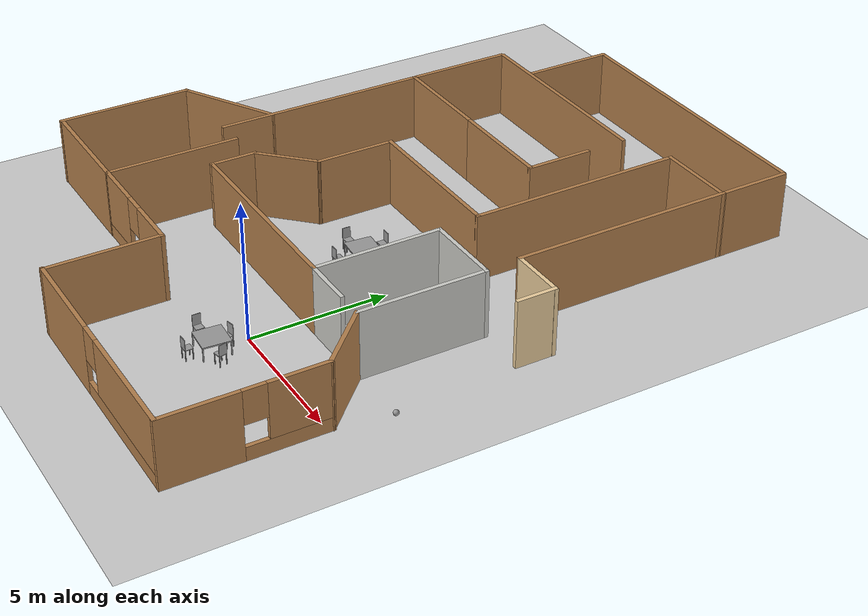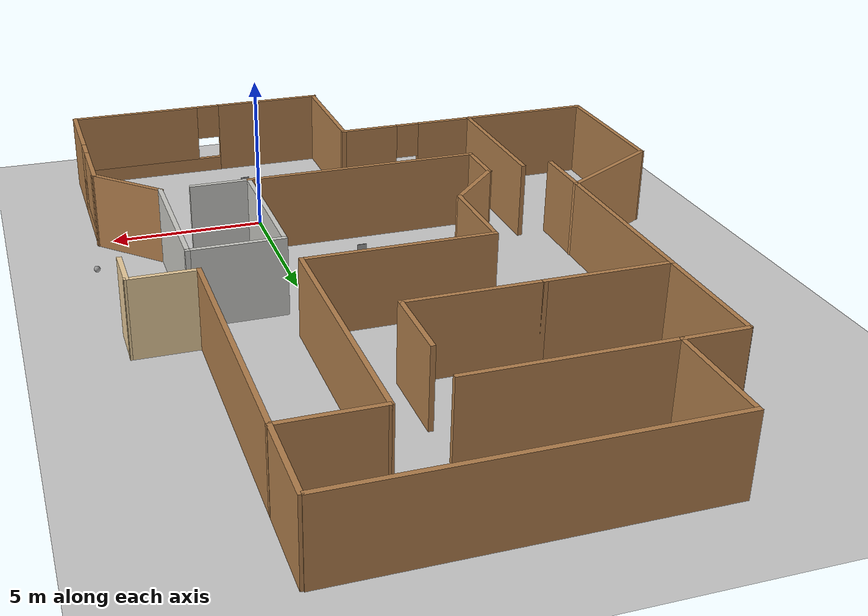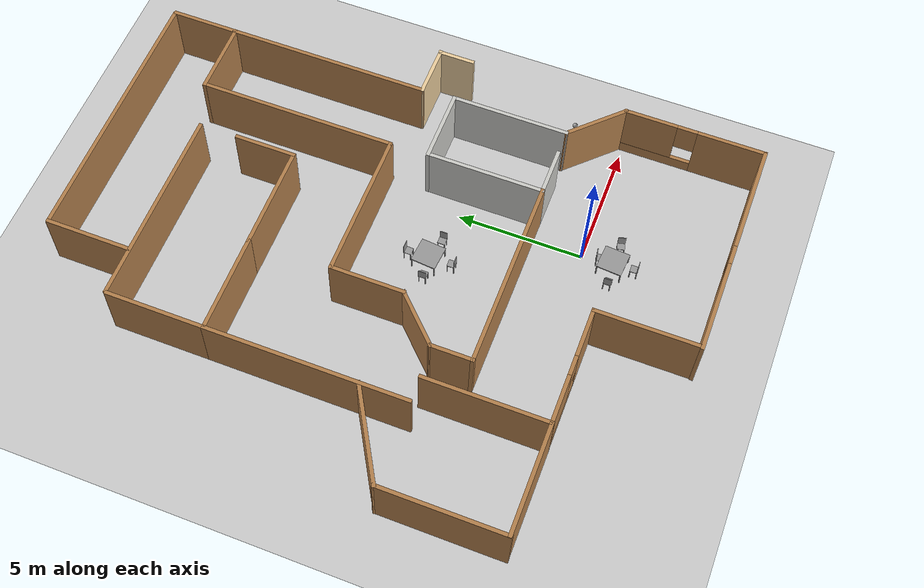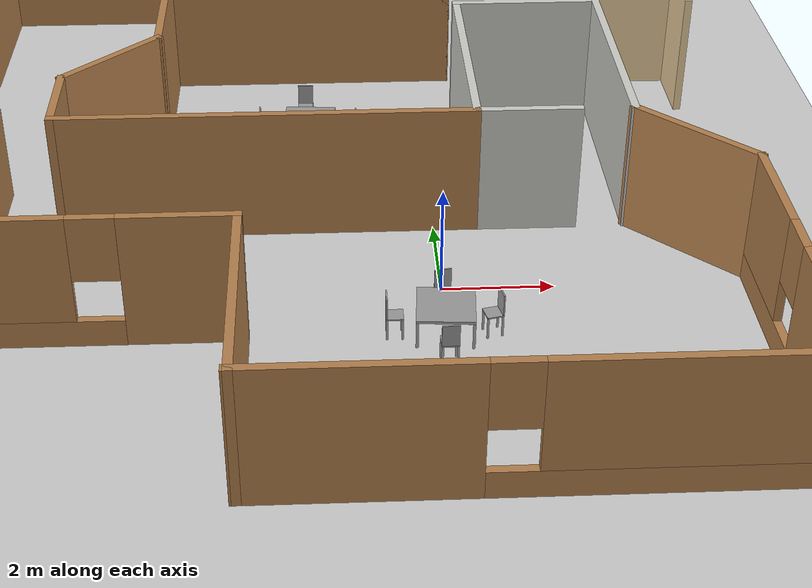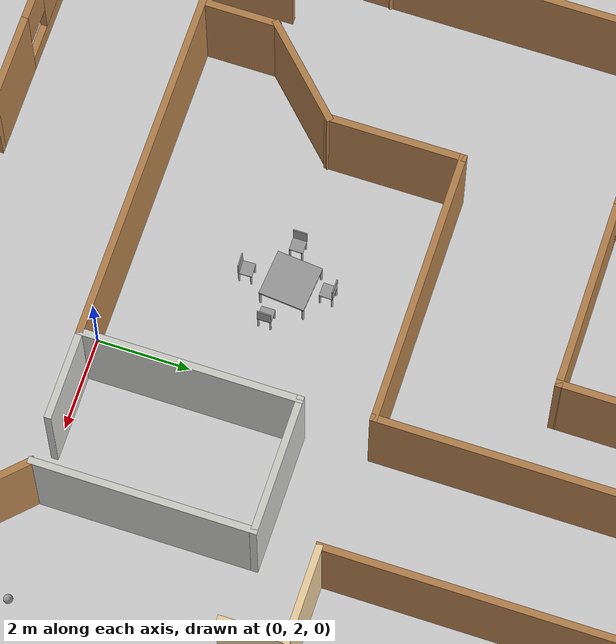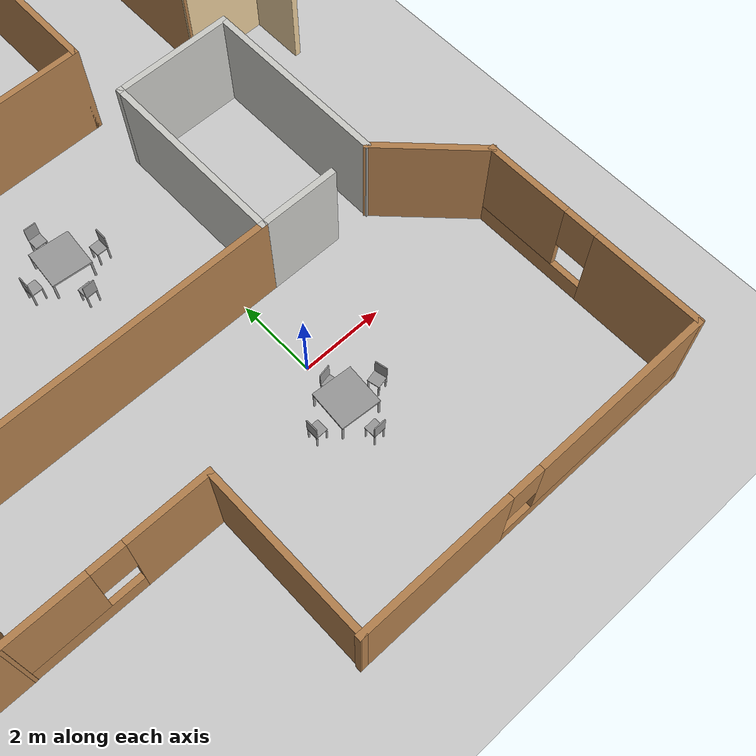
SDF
<sdf version="1.6">
 <world name="default">
  <light name="sun" type="directional">
   <pose>0 0 10 0 -0 0</pose>
   <diffuse>0.8 0.8 0.8 1</diffuse>
   <specular>0.2 0.2 0.2 1</specular>
   <attenuation>
    <range>1000</range>
    <constant>0.9</constant>
    <linear>0.01</linear>
    <quadratic>0.001</quadratic>
   </attenuation>
   <direction>-0.5 0.1 -0.9</direction>
  </light>
  <model name="ground_plane">
   <static>1</static>
   <link name="link">
    <collision name="collision">
     <geometry><plane><normal>0 0 1</normal><size>100 100</size></plane></geometry>
     <surface><friction><ode><mu>100</mu><mu2>50</mu2></ode></friction></surface>
    </collision>
    <visual name="visual">
     <cast_shadows>0</cast_shadows>
     <geometry><plane><normal>0 0 1</normal><size>100 100</size></plane></geometry>
     <material>
      <script><uri>file://media/materials/scripts/gazebo.material</uri><name>Gazebo/Grey</name></script>
     </material>
    </visual>
   </link>
  </model>
  <gravity>0 0 -9.8</gravity>
  <magnetic_field>6e-06 2.3e-05 -4.2e-05</magnetic_field>
  <atmosphere type="adiabatic"/>
  <physics name="default_physics" default="0" type="ode">
   <max_step_size>0.001</max_step_size>
   <real_time_factor>1</real_time_factor>
   <real_time_update_rate>1000</real_time_update_rate>
  </physics>
  <scene><ambient>0.4 0.4 0.4 1</ambient><background>0.7 0.7 0.7 1</background><shadows>1</shadows></scene>
  <spherical_coordinates>
   <surface_model>EARTH_WGS84</surface_model>
   <latitude_deg>0</latitude_deg>
   <longitude_deg>0</longitude_deg>
   <elevation>0</elevation>
   <heading_deg>0</heading_deg>
  </spherical_coordinates>
  <model name="myTable">
   <link name="link_0">
    <pose>7.65666 6.42879 0.72 0 -0 0</pose>
    <inertial>
     <mass>1</mass>
     <inertia>
      <ixx>0.166667</ixx>
      <ixy>0</ixy>
      <ixz>0</ixz>
      <iyy>0.166667</iyy>
      <iyz>0</iyz>
      <izz>0.166667</izz>
     </inertia>
    </inertial>
    <visual name="visual">
     <geometry><box><size>1 1 0.05</size></box></geometry>
     <material>
      <lighting>1</lighting>
      <script><uri>file://media/materials/scripts/gazebo.material</uri><name>Gazebo/Grey</name></script>
      <ambient>0.3 0.3 0.3 1</ambient>
      <diffuse>0.7 0.7 0.7 1</diffuse>
      <specular>0.01 0.01 0.01 1</specular>
      <emissive>0 0 0 1</emissive>
      <shader type="vertex"><normal_map>__default__</normal_map></shader>
     </material>
    </visual>
    <collision name="collision">
     <geometry><box><size>1 1 0.05</size></box></geometry>
     <surface>
      <friction>
       <ode><mu>1</mu><mu2>1</mu2><fdir1>0 0 0</fdir1><slip1>0</slip1><slip2>0</slip2></ode>
       <torsional>
        <coefficient>1</coefficient>
        <patch_radius>0</patch_radius>
        <surface_radius>0</surface_radius>
        <use_patch_radius>1</use_patch_radius>
        <ode><slip>0</slip></ode>
       </torsional>
      </friction>
      <bounce><restitution_coefficient>0</restitution_coefficient><threshold>1e+06</threshold></bounce>
      <contact>
       <collide_without_contact>0</collide_without_contact>
       <collide_without_contact_bitmask>1</collide_without_contact_bitmask>
       <collide_bitmask>1</collide_bitmask>
       <ode>
        <soft_cfm>0</soft_cfm>
        <soft_erp>0.2</soft_erp>
        <kp>1e+13</kp>
        <kd>1</kd>
        <max_vel>0.01</max_vel>
        <min_depth>0</min_depth>
       </ode>
       <bullet>
        <split_impulse>1</split_impulse>
        <split_impulse_penetration_threshold>-0.01</split_impulse_penetration_threshold>
        <soft_cfm>0</soft_cfm>
        <soft_erp>0.2</soft_erp>
        <kp>1e+13</kp>
        <kd>1</kd>
       </bullet>
      </contact>
     </surface>
    </collision>
   </link>
   <link name="link_1">
    <pose>7.18166 5.95379 0.445 0 -0 0</pose>
    <inertial>
     <mass>1</mass>
     <inertia><ixx>0.145833</ixx><ixy>0</ixy><ixz>0</ixz><iyy>0.145833</iyy><iyz>0</iyz><izz>0.125</izz></inertia>
    </inertial>
    <visual name="visual">
     <geometry><cylinder><radius>0.025</radius><length>0.5</length></cylinder></geometry>
     <material>
      <lighting>1</lighting>
      <script><uri>file://media/materials/scripts/gazebo.material</uri><name>Gazebo/Grey</name></script>
      <ambient>0.3 0.3 0.3 1</ambient>
      <diffuse>0.7 0.7 0.7 1</diffuse>
      <specular>0.01 0.01 0.01 1</specular>
      <emissive>0 0 0 1</emissive>
      <shader type="vertex"><normal_map>__default__</normal_map></shader>
     </material>
    </visual>
    <collision name="collision">
     <geometry><cylinder><radius>0.025</radius><length>0.5</length></cylinder></geometry>
     <surface>
      <friction>
       <ode><mu>1</mu><mu2>1</mu2><fdir1>0 0 0</fdir1><slip1>0</slip1><slip2>0</slip2></ode>
       <torsional>
        <coefficient>1</coefficient>
        <patch_radius>0</patch_radius>
        <surface_radius>0</surface_radius>
        <use_patch_radius>1</use_patch_radius>
        <ode><slip>0</slip></ode>
       </torsional>
      </friction>
      <bounce><restitution_coefficient>0</restitution_coefficient><threshold>1e+06</threshold></bounce>
      <contact>
       <collide_without_contact>0</collide_without_contact>
       <collide_without_contact_bitmask>1</collide_without_contact_bitmask>
       <collide_bitmask>1</collide_bitmask>
       <ode>
        <soft_cfm>0</soft_cfm>
        <soft_erp>0.2</soft_erp>
        <kp>1e+13</kp>
        <kd>1</kd>
        <max_vel>0.01</max_vel>
        <min_depth>0</min_depth>
       </ode>
       <bullet>
        <split_impulse>1</split_impulse>
        <split_impulse_penetration_threshold>-0.01</split_impulse_penetration_threshold>
        <soft_cfm>0</soft_cfm>
        <soft_erp>0.2</soft_erp>
        <kp>1e+13</kp>
        <kd>1</kd>
       </bullet>
      </contact>
     </surface>
    </collision>
   </link>
   <link name="link_1_clone">
    <pose>7.18166 6.90379 0.445 0 -0 0</pose>
    <inertial>
     <mass>1</mass>
     <inertia><ixx>0.145833</ixx><ixy>0</ixy><ixz>0</ixz><iyy>0.145833</iyy><iyz>0</iyz><izz>0.125</izz></inertia>
    </inertial>
    <visual name="visual">
     <geometry><cylinder><radius>0.025</radius><length>0.5</length></cylinder></geometry>
     <material>
      <lighting>1</lighting>
      <script><uri>file://media/materials/scripts/gazebo.material</uri><name>Gazebo/Grey</name></script>
      <ambient>0.3 0.3 0.3 1</ambient>
      <diffuse>0.7 0.7 0.7 1</diffuse>
      <specular>0.01 0.01 0.01 1</specular>
      <emissive>0 0 0 1</emissive>
      <shader type="vertex"><normal_map>__default__</normal_map></shader>
     </material>
    </visual>
    <collision name="collision">
     <geometry><cylinder><radius>0.025</radius><length>0.5</length></cylinder></geometry>
     <surface>
      <friction>
       <ode><mu>1</mu><mu2>1</mu2><fdir1>0 0 0</fdir1><slip1>0</slip1><slip2>0</slip2></ode>
       <torsional>
        <coefficient>1</coefficient>
        <patch_radius>0</patch_radius>
        <surface_radius>0</surface_radius>
        <use_patch_radius>1</use_patch_radius>
        <ode><slip>0</slip></ode>
       </torsional>
      </friction>
      <bounce><restitution_coefficient>0</restitution_coefficient><threshold>1e+06</threshold></bounce>
      <contact>
       <collide_without_contact>0</collide_without_contact>
       <collide_without_contact_bitmask>1</collide_without_contact_bitmask>
       <collide_bitmask>1</collide_bitmask>
       <ode>
        <soft_cfm>0</soft_cfm>
        <soft_erp>0.2</soft_erp>
        <kp>1e+13</kp>
        <kd>1</kd>
        <max_vel>0.01</max_vel>
        <min_depth>0</min_depth>
       </ode>
       <bullet>
        <split_impulse>1</split_impulse>
        <split_impulse_penetration_threshold>-0.01</split_impulse_penetration_threshold>
        <soft_cfm>0</soft_cfm>
        <soft_erp>0.2</soft_erp>
        <kp>1e+13</kp>
        <kd>1</kd>
       </bullet>
      </contact>
     </surface>
    </collision>
   </link>
   <link name="link_1_clone_0">
    <pose>8.13166 6.90379 0.445 0 -0 0</pose>
    <inertial>
     <mass>1</mass>
     <inertia><ixx>0.145833</ixx><ixy>0</ixy><ixz>0</ixz><iyy>0.145833</iyy><iyz>0</iyz><izz>0.125</izz></inertia>
    </inertial>
    <visual name="visual">
     <geometry><cylinder><radius>0.025</radius><length>0.5</length></cylinder></geometry>
     <material>
      <lighting>1</lighting>
      <script><uri>file://media/materials/scripts/gazebo.material</uri><name>Gazebo/Grey</name></script>
      <ambient>0.3 0.3 0.3 1</ambient>
      <diffuse>0.7 0.7 0.7 1</diffuse>
      <specular>0.01 0.01 0.01 1</specular>
      <emissive>0 0 0 1</emissive>
      <shader type="vertex"><normal_map>__default__</normal_map></shader>
     </material>
    </visual>
    <collision name="collision">
     <geometry><cylinder><radius>0.025</radius><length>0.5</length></cylinder></geometry>
     <surface>
      <friction>
       <ode><mu>1</mu><mu2>1</mu2><fdir1>0 0 0</fdir1><slip1>0</slip1><slip2>0</slip2></ode>
       <torsional>
        <coefficient>1</coefficient>
        <patch_radius>0</patch_radius>
        <surface_radius>0</surface_radius>
        <use_patch_radius>1</use_patch_radius>
        <ode><slip>0</slip></ode>
       </torsional>
      </friction>
      <bounce><restitution_coefficient>0</restitution_coefficient><threshold>1e+06</threshold></bounce>
      <contact>
       <collide_without_contact>0</collide_without_contact>
       <collide_without_contact_bitmask>1</collide_without_contact_bitmask>
       <collide_bitmask>1</collide_bitmask>
       <ode>
        <soft_cfm>0</soft_cfm>
        <soft_erp>0.2</soft_erp>
        <kp>1e+13</kp>
        <kd>1</kd>
        <max_vel>0.01</max_vel>
        <min_depth>0</min_depth>
       </ode>
       <bullet>
        <split_impulse>1</split_impulse>
        <split_impulse_penetration_threshold>-0.01</split_impulse_penetration_threshold>
        <soft_cfm>0</soft_cfm>
        <soft_erp>0.2</soft_erp>
        <kp>1e+13</kp>
        <kd>1</kd>
       </bullet>
      </contact>
     </surface>
    </collision>
   </link>
   <link name="link_1_clone_1">
    <pose>8.13166 5.95379 0.445 0 -0 0</pose>
    <inertial>
     <mass>1</mass>
     <inertia><ixx>0.145833</ixx><ixy>0</ixy><ixz>0</ixz><iyy>0.145833</iyy><iyz>0</iyz><izz>0.125</izz></inertia>
    </inertial>
    <visual name="visual">
     <geometry><cylinder><radius>0.025</radius><length>0.5</length></cylinder></geometry>
     <material>
      <lighting>1</lighting>
      <script><uri>file://media/materials/scripts/gazebo.material</uri><name>Gazebo/Grey</name></script>
      <ambient>0.3 0.3 0.3 1</ambient>
      <diffuse>0.7 0.7 0.7 1</diffuse>
      <specular>0.01 0.01 0.01 1</specular>
      <emissive>0 0 0 1</emissive>
      <shader type="vertex"><normal_map>__default__</normal_map></shader>
     </material>
    </visual>
    <collision name="collision">
     <geometry><cylinder><radius>0.025</radius><length>0.5</length></cylinder></geometry>
     <surface>
      <friction>
       <ode><mu>1</mu><mu2>1</mu2><fdir1>0 0 0</fdir1><slip1>0</slip1><slip2>0</slip2></ode>
       <torsional>
        <coefficient>1</coefficient>
        <patch_radius>0</patch_radius>
        <surface_radius>0</surface_radius>
        <use_patch_radius>1</use_patch_radius>
        <ode><slip>0</slip></ode>
       </torsional>
      </friction>
      <bounce><restitution_coefficient>0</restitution_coefficient><threshold>1e+06</threshold></bounce>
      <contact>
       <collide_without_contact>0</collide_without_contact>
       <collide_without_contact_bitmask>1</collide_without_contact_bitmask>
       <collide_bitmask>1</collide_bitmask>
       <ode>
        <soft_cfm>0</soft_cfm>
        <soft_erp>0.2</soft_erp>
        <kp>1e+13</kp>
        <kd>1</kd>
        <max_vel>0.01</max_vel>
        <min_depth>0</min_depth>
       </ode>
       <bullet>
        <split_impulse>1</split_impulse>
        <split_impulse_penetration_threshold>-0.01</split_impulse_penetration_threshold>
        <soft_cfm>0</soft_cfm>
        <soft_erp>0.2</soft_erp>
        <kp>1e+13</kp>
        <kd>1</kd>
       </bullet>
      </contact>
     </surface>
    </collision>
   </link>
   <joint name="link_0_JOINT_0" type="fixed">
    <parent>link_0</parent>
    <child>link_1</child>
    <physics>
     <ode><limit><cfm>0</cfm><erp>0.2</erp></limit><suspension><cfm>0</cfm><erp>0.2</erp></suspension></ode>
    </physics>
   </joint>
   <joint name="link_0_JOINT_1" type="fixed">
    <parent>link_0</parent>
    <child>link_1_clone_1</child>
    <physics>
     <ode><limit><cfm>0</cfm><erp>0.2</erp></limit><suspension><cfm>0</cfm><erp>0.2</erp></suspension></ode>
    </physics>
   </joint>
   <joint name="link_0_JOINT_2" type="revolute">
    <parent>link_0</parent>
    <child>link_1_clone</child>
    <axis>
     <xyz>1 0 0</xyz>
     <use_parent_model_frame>0</use_parent_model_frame>
     <limit>
      <lower>-1.79769e+308</lower>
      <upper>1.79769e+308</upper>
      <effort>-1</effort>
      <velocity>-1</velocity>
     </limit>
     <dynamics>
      <spring_reference>0</spring_reference>
      <spring_stiffness>0</spring_stiffness>
      <damping>0</damping>
     </dynamics>
    </axis>
    <physics>
     <ode><limit><cfm>0</cfm><erp>0.2</erp></limit><suspension><cfm>0</cfm><erp>0.2</erp></suspension></ode>
    </physics>
   </joint>
   <joint name="link_0_JOINT_3" type="fixed">
    <parent>link_0</parent>
    <child>link_1_clone_0</child>
    <physics>
     <ode><limit><cfm>0</cfm><erp>0.2</erp></limit><suspension><cfm>0</cfm><erp>0.2</erp></suspension></ode>
    </physics>
   </joint>
   <static>0</static>
   <pose>-10.4829 -0.32111 -0.195007 1e-05 7e-06 -0.08738</pose>
  </model>
  <model name="myTable_0">
   <link name="link_0">
    <pose>7.65666 6.42879 0.72 0 -0 0</pose>
    <inertial>
     <mass>1</mass>
     <inertia>
      <ixx>0.166667</ixx>
      <ixy>0</ixy>
      <ixz>0</ixz>
      <iyy>0.166667</iyy>
      <iyz>0</iyz>
      <izz>0.166667</izz>
     </inertia>
    </inertial>
    <visual name="visual">
     <geometry><box><size>1 1 0.05</size></box></geometry>
     <material>
      <lighting>1</lighting>
      <script><uri>file://media/materials/scripts/gazebo.material</uri><name>Gazebo/Grey</name></script>
      <ambient>0.3 0.3 0.3 1</ambient>
      <diffuse>0.7 0.7 0.7 1</diffuse>
      <specular>0.01 0.01 0.01 1</specular>
      <emissive>0 0 0 1</emissive>
      <shader type="vertex"><normal_map>__default__</normal_map></shader>
     </material>
    </visual>
    <collision name="collision">
     <geometry><box><size>1 1 0.05</size></box></geometry>
     <surface>
      <friction>
       <ode><mu>1</mu><mu2>1</mu2><fdir1>0 0 0</fdir1><slip1>0</slip1><slip2>0</slip2></ode>
       <torsional>
        <coefficient>1</coefficient>
        <patch_radius>0</patch_radius>
        <surface_radius>0</surface_radius>
        <use_patch_radius>1</use_patch_radius>
        <ode><slip>0</slip></ode>
       </torsional>
      </friction>
      <bounce><restitution_coefficient>0</restitution_coefficient><threshold>1e+06</threshold></bounce>
      <contact>
       <collide_without_contact>0</collide_without_contact>
       <collide_without_contact_bitmask>1</collide_without_contact_bitmask>
       <collide_bitmask>1</collide_bitmask>
       <ode>
        <soft_cfm>0</soft_cfm>
        <soft_erp>0.2</soft_erp>
        <kp>1e+13</kp>
        <kd>1</kd>
        <max_vel>0.01</max_vel>
        <min_depth>0</min_depth>
       </ode>
       <bullet>
        <split_impulse>1</split_impulse>
        <split_impulse_penetration_threshold>-0.01</split_impulse_penetration_threshold>
        <soft_cfm>0</soft_cfm>
        <soft_erp>0.2</soft_erp>
        <kp>1e+13</kp>
        <kd>1</kd>
       </bullet>
      </contact>
     </surface>
    </collision>
   </link>
   <link name="link_1">
    <pose>7.18166 5.95379 0.445 0 -0 0</pose>
    <inertial>
     <mass>1</mass>
     <inertia><ixx>0.145833</ixx><ixy>0</ixy><ixz>0</ixz><iyy>0.145833</iyy><iyz>0</iyz><izz>0.125</izz></inertia>
    </inertial>
    <visual name="visual">
     <geometry><cylinder><radius>0.025</radius><length>0.5</length></cylinder></geometry>
     <material>
      <lighting>1</lighting>
      <script><uri>file://media/materials/scripts/gazebo.material</uri><name>Gazebo/Grey</name></script>
      <ambient>0.3 0.3 0.3 1</ambient>
      <diffuse>0.7 0.7 0.7 1</diffuse>
      <specular>0.01 0.01 0.01 1</specular>
      <emissive>0 0 0 1</emissive>
      <shader type="vertex"><normal_map>__default__</normal_map></shader>
     </material>
    </visual>
    <collision name="collision">
     <geometry><cylinder><radius>0.025</radius><length>0.5</length></cylinder></geometry>
     <surface>
      <friction>
       <ode><mu>1</mu><mu2>1</mu2><fdir1>0 0 0</fdir1><slip1>0</slip1><slip2>0</slip2></ode>
       <torsional>
        <coefficient>1</coefficient>
        <patch_radius>0</patch_radius>
        <surface_radius>0</surface_radius>
        <use_patch_radius>1</use_patch_radius>
        <ode><slip>0</slip></ode>
       </torsional>
      </friction>
      <bounce><restitution_coefficient>0</restitution_coefficient><threshold>1e+06</threshold></bounce>
      <contact>
       <collide_without_contact>0</collide_without_contact>
       <collide_without_contact_bitmask>1</collide_without_contact_bitmask>
       <collide_bitmask>1</collide_bitmask>
       <ode>
        <soft_cfm>0</soft_cfm>
        <soft_erp>0.2</soft_erp>
        <kp>1e+13</kp>
        <kd>1</kd>
        <max_vel>0.01</max_vel>
        <min_depth>0</min_depth>
       </ode>
       <bullet>
        <split_impulse>1</split_impulse>
        <split_impulse_penetration_threshold>-0.01</split_impulse_penetration_threshold>
        <soft_cfm>0</soft_cfm>
        <soft_erp>0.2</soft_erp>
        <kp>1e+13</kp>
        <kd>1</kd>
       </bullet>
      </contact>
     </surface>
    </collision>
   </link>
   <link name="link_1_clone">
    <pose>7.18166 6.90379 0.445 0 -0 0</pose>
    <inertial>
     <mass>1</mass>
     <inertia><ixx>0.145833</ixx><ixy>0</ixy><ixz>0</ixz><iyy>0.145833</iyy><iyz>0</iyz><izz>0.125</izz></inertia>
    </inertial>
    <visual name="visual">
     <geometry><cylinder><radius>0.025</radius><length>0.5</length></cylinder></geometry>
     <material>
      <lighting>1</lighting>
      <script><uri>file://media/materials/scripts/gazebo.material</uri><name>Gazebo/Grey</name></script>
      <ambient>0.3 0.3 0.3 1</ambient>
      <diffuse>0.7 0.7 0.7 1</diffuse>
      <specular>0.01 0.01 0.01 1</specular>
      <emissive>0 0 0 1</emissive>
      <shader type="vertex"><normal_map>__default__</normal_map></shader>
     </material>
    </visual>
    <collision name="collision">
     <geometry><cylinder><radius>0.025</radius><length>0.5</length></cylinder></geometry>
     <surface>
      <friction>
       <ode><mu>1</mu><mu2>1</mu2><fdir1>0 0 0</fdir1><slip1>0</slip1><slip2>0</slip2></ode>
       <torsional>
        <coefficient>1</coefficient>
        <patch_radius>0</patch_radius>
        <surface_radius>0</surface_radius>
        <use_patch_radius>1</use_patch_radius>
        <ode><slip>0</slip></ode>
       </torsional>
      </friction>
      <bounce><restitution_coefficient>0</restitution_coefficient><threshold>1e+06</threshold></bounce>
      <contact>
       <collide_without_contact>0</collide_without_contact>
       <collide_without_contact_bitmask>1</collide_without_contact_bitmask>
       <collide_bitmask>1</collide_bitmask>
       <ode>
        <soft_cfm>0</soft_cfm>
        <soft_erp>0.2</soft_erp>
        <kp>1e+13</kp>
        <kd>1</kd>
        <max_vel>0.01</max_vel>
        <min_depth>0</min_depth>
       </ode>
       <bullet>
        <split_impulse>1</split_impulse>
        <split_impulse_penetration_threshold>-0.01</split_impulse_penetration_threshold>
        <soft_cfm>0</soft_cfm>
        <soft_erp>0.2</soft_erp>
        <kp>1e+13</kp>
        <kd>1</kd>
       </bullet>
      </contact>
     </surface>
    </collision>
   </link>
   <link name="link_1_clone_0">
    <pose>8.13166 6.90379 0.445 0 -0 0</pose>
    <inertial>
     <mass>1</mass>
     <inertia><ixx>0.145833</ixx><ixy>0</ixy><ixz>0</ixz><iyy>0.145833</iyy><iyz>0</iyz><izz>0.125</izz></inertia>
    </inertial>
    <visual name="visual">
     <geometry><cylinder><radius>0.025</radius><length>0.5</length></cylinder></geometry>
     <material>
      <lighting>1</lighting>
      <script><uri>file://media/materials/scripts/gazebo.material</uri><name>Gazebo/Grey</name></script>
      <ambient>0.3 0.3 0.3 1</ambient>
      <diffuse>0.7 0.7 0.7 1</diffuse>
      <specular>0.01 0.01 0.01 1</specular>
      <emissive>0 0 0 1</emissive>
      <shader type="vertex"><normal_map>__default__</normal_map></shader>
     </material>
    </visual>
    <collision name="collision">
     <geometry><cylinder><radius>0.025</radius><length>0.5</length></cylinder></geometry>
     <surface>
      <friction>
       <ode><mu>1</mu><mu2>1</mu2><fdir1>0 0 0</fdir1><slip1>0</slip1><slip2>0</slip2></ode>
       <torsional>
        <coefficient>1</coefficient>
        <patch_radius>0</patch_radius>
        <surface_radius>0</surface_radius>
        <use_patch_radius>1</use_patch_radius>
        <ode><slip>0</slip></ode>
       </torsional>
      </friction>
      <bounce><restitution_coefficient>0</restitution_coefficient><threshold>1e+06</threshold></bounce>
      <contact>
       <collide_without_contact>0</collide_without_contact>
       <collide_without_contact_bitmask>1</collide_without_contact_bitmask>
       <collide_bitmask>1</collide_bitmask>
       <ode>
        <soft_cfm>0</soft_cfm>
        <soft_erp>0.2</soft_erp>
        <kp>1e+13</kp>
        <kd>1</kd>
        <max_vel>0.01</max_vel>
        <min_depth>0</min_depth>
       </ode>
       <bullet>
        <split_impulse>1</split_impulse>
        <split_impulse_penetration_threshold>-0.01</split_impulse_penetration_threshold>
        <soft_cfm>0</soft_cfm>
        <soft_erp>0.2</soft_erp>
        <kp>1e+13</kp>
        <kd>1</kd>
       </bullet>
      </contact>
     </surface>
    </collision>
   </link>
   <link name="link_1_clone_1">
    <pose>8.13166 5.95379 0.445 0 -0 0</pose>
    <inertial>
     <mass>1</mass>
     <inertia><ixx>0.145833</ixx><ixy>0</ixy><ixz>0</ixz><iyy>0.145833</iyy><iyz>0</iyz><izz>0.125</izz></inertia>
    </inertial>
    <visual name="visual">
     <geometry><cylinder><radius>0.025</radius><length>0.5</length></cylinder></geometry>
     <material>
      <lighting>1</lighting>
      <script><uri>file://media/materials/scripts/gazebo.material</uri><name>Gazebo/Grey</name></script>
      <ambient>0.3 0.3 0.3 1</ambient>
      <diffuse>0.7 0.7 0.7 1</diffuse>
      <specular>0.01 0.01 0.01 1</specular>
      <emissive>0 0 0 1</emissive>
      <shader type="vertex"><normal_map>__default__</normal_map></shader>
     </material>
    </visual>
    <collision name="collision">
     <geometry><cylinder><radius>0.025</radius><length>0.5</length></cylinder></geometry>
     <surface>
      <friction>
       <ode><mu>1</mu><mu2>1</mu2><fdir1>0 0 0</fdir1><slip1>0</slip1><slip2>0</slip2></ode>
       <torsional>
        <coefficient>1</coefficient>
        <patch_radius>0</patch_radius>
        <surface_radius>0</surface_radius>
        <use_patch_radius>1</use_patch_radius>
        <ode><slip>0</slip></ode>
       </torsional>
      </friction>
      <bounce><restitution_coefficient>0</restitution_coefficient><threshold>1e+06</threshold></bounce>
      <contact>
       <collide_without_contact>0</collide_without_contact>
       <collide_without_contact_bitmask>1</collide_without_contact_bitmask>
       <collide_bitmask>1</collide_bitmask>
       <ode>
        <soft_cfm>0</soft_cfm>
        <soft_erp>0.2</soft_erp>
        <kp>1e+13</kp>
        <kd>1</kd>
        <max_vel>0.01</max_vel>
        <min_depth>0</min_depth>
       </ode>
       <bullet>
        <split_impulse>1</split_impulse>
        <split_impulse_penetration_threshold>-0.01</split_impulse_penetration_threshold>
        <soft_cfm>0</soft_cfm>
        <soft_erp>0.2</soft_erp>
        <kp>1e+13</kp>
        <kd>1</kd>
       </bullet>
      </contact>
     </surface>
    </collision>
   </link>
   <joint name="link_0_JOINT_0" type="fixed">
    <parent>link_0</parent>
    <child>link_1</child>
    <physics>
     <ode><limit><cfm>0</cfm><erp>0.2</erp></limit><suspension><cfm>0</cfm><erp>0.2</erp></suspension></ode>
    </physics>
   </joint>
   <joint name="link_0_JOINT_1" type="fixed">
    <parent>link_0</parent>
    <child>link_1_clone_1</child>
    <physics>
     <ode><limit><cfm>0</cfm><erp>0.2</erp></limit><suspension><cfm>0</cfm><erp>0.2</erp></suspension></ode>
    </physics>
   </joint>
   <joint name="link_0_JOINT_2" type="revolute">
    <parent>link_0</parent>
    <child>link_1_clone</child>
    <axis>
     <xyz>1 0 0</xyz>
     <use_parent_model_frame>0</use_parent_model_frame>
     <limit>
      <lower>-1.79769e+308</lower>
      <upper>1.79769e+308</upper>
      <effort>-1</effort>
      <velocity>-1</velocity>
     </limit>
     <dynamics>
      <spring_reference>0</spring_reference>
      <spring_stiffness>0</spring_stiffness>
      <damping>0</damping>
     </dynamics>
    </axis>
    <physics>
     <ode><limit><cfm>0</cfm><erp>0.2</erp></limit><suspension><cfm>0</cfm><erp>0.2</erp></suspension></ode>
    </physics>
   </joint>
   <joint name="link_0_JOINT_3" type="fixed">
    <parent>link_0</parent>
    <child>link_1_clone_0</child>
    <physics>
     <ode><limit><cfm>0</cfm><erp>0.2</erp></limit><suspension><cfm>0</cfm><erp>0.2</erp></suspension></ode>
    </physics>
   </joint>
   <static>0</static>
   <pose>-8.12391 -7.09104 -0.195025 0 -3e-06 -0.073318</pose>
  </model>
  <model name="myHouse">
   <link name="Wall_0">
    <pose>0.060223 -9.98751 0 0 0 -1.5708</pose>
    <visual name="Wall_0_Visual">
     <pose>0 0 1.25 0 -0 0</pose>
     <geometry><box><size>4.184 0.15 2.5</size></box></geometry>
     <material>
      <script><uri>file://media/materials/scripts/gazebo.material</uri><name>Gazebo/Wood</name></script>
      <ambient>1 1 1 1</ambient>
      <diffuse>1 1 1 1</diffuse>
      <specular>0.2 0.2 0.2 1</specular>
      <emissive>0 0 0 1</emissive>
     </material>
     <meta><layer>0</layer></meta>
    </visual>
    <collision name="Wall_0_Collision">
     <pose>0 0 1.25 0 -0 0</pose>
     <geometry><box><size>4.184 0.15 2.5</size></box></geometry>
     <surface>
      <friction>
       <ode><mu>1</mu><mu2>1</mu2><fdir1>0 0 0</fdir1><slip1>0</slip1><slip2>0</slip2></ode>
       <torsional>
        <coefficient>1</coefficient>
        <patch_radius>0</patch_radius>
        <surface_radius>0</surface_radius>
        <use_patch_radius>1</use_patch_radius>
        <ode><slip>0</slip></ode>
       </torsional>
      </friction>
      <bounce><restitution_coefficient>0</restitution_coefficient><threshold>1e+06</threshold></bounce>
      <contact>
       <collide_without_contact>0</collide_without_contact>
       <collide_without_contact_bitmask>1</collide_without_contact_bitmask>
       <collide_bitmask>1</collide_bitmask>
       <ode>
        <soft_cfm>0</soft_cfm>
        <soft_erp>0.2</soft_erp>
        <kp>1e+13</kp>
        <kd>1</kd>
        <max_vel>0.01</max_vel>
        <min_depth>0</min_depth>
       </ode>
       <bullet>
        <split_impulse>1</split_impulse>
        <split_impulse_penetration_threshold>-0.01</split_impulse_penetration_threshold>
        <soft_cfm>0</soft_cfm>
        <soft_erp>0.2</soft_erp>
        <kp>1e+13</kp>
        <kd>1</kd>
       </bullet>
      </contact>
     </surface>
    </collision>
   </link>
   <link name="Wall_1">
    <pose>4.45004 -12.0042 0 0 -0 0</pose>
    <visual name="Wall_1_Visual_0">
     <pose>-2.62145 0 1.25 0 -0 0</pose>
     <geometry><box><size>3.7571 0.15 2.5</size></box></geometry>
     <material>
      <script><uri>file://media/materials/scripts/gazebo.material</uri><name>Gazebo/Wood</name></script>
      <ambient>1 1 1 1</ambient>
      <diffuse>1 1 1 1</diffuse>
      <specular>0.2 0.2 0.2 1</specular>
      <emissive>0 0 0 1</emissive>
     </material>
     <meta><layer>0</layer></meta>
    </visual>
    <visual name="Wall_1_Visual_1">
     <pose>1.87855 0 0.25 0 -0 0</pose>
     <geometry><box><size>5.2429 0.15 0.5</size></box></geometry>
     <material>
      <script><uri>file://media/materials/scripts/gazebo.material</uri><name>Gazebo/Wood</name></script>
      <ambient>1 1 1 1</ambient>
      <diffuse>1 1 1 1</diffuse>
      <specular>0.2 0.2 0.2 1</specular>
      <emissive>0 0 0 1</emissive>
     </material>
     <meta><layer>0</layer></meta>
    </visual>
    <visual name="Wall_1_Visual_2">
     <pose>2.27855 0 1.5 0 -0 0</pose>
     <geometry><box><size>4.4429 0.15 2</size></box></geometry>
     <material>
      <script><uri>file://media/materials/scripts/gazebo.material</uri><name>Gazebo/Wood</name></script>
      <ambient>1 1 1 1</ambient>
      <diffuse>1 1 1 1</diffuse>
      <specular>0.2 0.2 0.2 1</specular>
      <emissive>0 0 0 1</emissive>
     </material>
     <meta><layer>0</layer></meta>
    </visual>
    <visual name="Wall_1_Visual_3">
     <pose>-0.342896 0 1.9 0 -0 0</pose>
     <geometry><box><size>0.8 0.15 1.2</size></box></geometry>
     <material>
      <script><uri>file://media/materials/scripts/gazebo.material</uri><name>Gazebo/Wood</name></script>
      <ambient>1 1 1 1</ambient>
      <diffuse>1 1 1 1</diffuse>
      <specular>0.2 0.2 0.2 1</specular>
      <emissive>0 0 0 1</emissive>
     </material>
     <meta><layer>0</layer></meta>
    </visual>
    <collision name="Wall_1_Collision_0">
     <pose>-2.62145 0 1.25 0 -0 0</pose>
     <geometry><box><size>3.7571 0.15 2.5</size></box></geometry>
     <surface>
      <friction>
       <ode><mu>1</mu><mu2>1</mu2><fdir1>0 0 0</fdir1><slip1>0</slip1><slip2>0</slip2></ode>
       <torsional>
        <coefficient>1</coefficient>
        <patch_radius>0</patch_radius>
        <surface_radius>0</surface_radius>
        <use_patch_radius>1</use_patch_radius>
        <ode><slip>0</slip></ode>
       </torsional>
      </friction>
      <bounce><restitution_coefficient>0</restitution_coefficient><threshold>1e+06</threshold></bounce>
      <contact>
       <collide_without_contact>0</collide_without_contact>
       <collide_without_contact_bitmask>1</collide_without_contact_bitmask>
       <collide_bitmask>1</collide_bitmask>
       <ode>
        <soft_cfm>0</soft_cfm>
        <soft_erp>0.2</soft_erp>
        <kp>1e+13</kp>
        <kd>1</kd>
        <max_vel>0.01</max_vel>
        <min_depth>0</min_depth>
       </ode>
       <bullet>
        <split_impulse>1</split_impulse>
        <split_impulse_penetration_threshold>-0.01</split_impulse_penetration_threshold>
        <soft_cfm>0</soft_cfm>
        <soft_erp>0.2</soft_erp>
        <kp>1e+13</kp>
        <kd>1</kd>
       </bullet>
      </contact>
     </surface>
    </collision>
    <collision name="Wall_1_Collision_1">
     <pose>1.87855 0 0.25 0 -0 0</pose>
     <geometry><box><size>5.2429 0.15 0.5</size></box></geometry>
     <surface>
      <friction>
       <ode><mu>1</mu><mu2>1</mu2><fdir1>0 0 0</fdir1><slip1>0</slip1><slip2>0</slip2></ode>
       <torsional>
        <coefficient>1</coefficient>
        <patch_radius>0</patch_radius>
        <surface_radius>0</surface_radius>
        <use_patch_radius>1</use_patch_radius>
        <ode><slip>0</slip></ode>
       </torsional>
      </friction>
      <bounce><restitution_coefficient>0</restitution_coefficient><threshold>1e+06</threshold></bounce>
      <contact>
       <collide_without_contact>0</collide_without_contact>
       <collide_without_contact_bitmask>1</collide_without_contact_bitmask>
       <collide_bitmask>1</collide_bitmask>
       <ode>
        <soft_cfm>0</soft_cfm>
        <soft_erp>0.2</soft_erp>
        <kp>1e+13</kp>
        <kd>1</kd>
        <max_vel>0.01</max_vel>
        <min_depth>0</min_depth>
       </ode>
       <bullet>
        <split_impulse>1</split_impulse>
        <split_impulse_penetration_threshold>-0.01</split_impulse_penetration_threshold>
        <soft_cfm>0</soft_cfm>
        <soft_erp>0.2</soft_erp>
        <kp>1e+13</kp>
        <kd>1</kd>
       </bullet>
      </contact>
     </surface>
    </collision>
    <collision name="Wall_1_Collision_2">
     <pose>2.27855 0 1.5 0 -0 0</pose>
     <geometry><box><size>4.4429 0.15 2</size></box></geometry>
     <surface>
      <friction>
       <ode><mu>1</mu><mu2>1</mu2><fdir1>0 0 0</fdir1><slip1>0</slip1><slip2>0</slip2></ode>
       <torsional>
        <coefficient>1</coefficient>
        <patch_radius>0</patch_radius>
        <surface_radius>0</surface_radius>
        <use_patch_radius>1</use_patch_radius>
        <ode><slip>0</slip></ode>
       </torsional>
      </friction>
      <bounce><restitution_coefficient>0</restitution_coefficient><threshold>1e+06</threshold></bounce>
      <contact>
       <collide_without_contact>0</collide_without_contact>
       <collide_without_contact_bitmask>1</collide_without_contact_bitmask>
       <collide_bitmask>1</collide_bitmask>
       <ode>
        <soft_cfm>0</soft_cfm>
        <soft_erp>0.2</soft_erp>
        <kp>1e+13</kp>
        <kd>1</kd>
        <max_vel>0.01</max_vel>
        <min_depth>0</min_depth>
       </ode>
       <bullet>
        <split_impulse>1</split_impulse>
        <split_impulse_penetration_threshold>-0.01</split_impulse_penetration_threshold>
        <soft_cfm>0</soft_cfm>
        <soft_erp>0.2</soft_erp>
        <kp>1e+13</kp>
        <kd>1</kd>
       </bullet>
      </contact>
     </surface>
    </collision>
    <collision name="Wall_1_Collision_3">
     <pose>-0.342896 0 1.9 0 -0 0</pose>
     <geometry><box><size>0.8 0.15 1.2</size></box></geometry>
     <surface>
      <friction>
       <ode><mu>1</mu><mu2>1</mu2><fdir1>0 0 0</fdir1><slip1>0</slip1><slip2>0</slip2></ode>
       <torsional>
        <coefficient>1</coefficient>
        <patch_radius>0</patch_radius>
        <surface_radius>0</surface_radius>
        <use_patch_radius>1</use_patch_radius>
        <ode><slip>0</slip></ode>
       </torsional>
      </friction>
      <bounce><restitution_coefficient>0</restitution_coefficient><threshold>1e+06</threshold></bounce>
      <contact>
       <collide_without_contact>0</collide_without_contact>
       <collide_without_contact_bitmask>1</collide_without_contact_bitmask>
       <collide_bitmask>1</collide_bitmask>
       <ode>
        <soft_cfm>0</soft_cfm>
        <soft_erp>0.2</soft_erp>
        <kp>1e+13</kp>
        <kd>1</kd>
        <max_vel>0.01</max_vel>
        <min_depth>0</min_depth>
       </ode>
       <bullet>
        <split_impulse>1</split_impulse>
        <split_impulse_penetration_threshold>-0.01</split_impulse_penetration_threshold>
        <soft_cfm>0</soft_cfm>
        <soft_erp>0.2</soft_erp>
        <kp>1e+13</kp>
        <kd>1</kd>
       </bullet>
      </contact>
     </surface>
    </collision>
   </link>
   <link name="Wall_10">
    <pose>-5.63978 0.790812 0 0 -0 1.5708</pose>
    <visual name="Wall_10_Visual">
     <pose>0 0 1.25 0 -0 0</pose>
     <geometry><box><size>8.02625 0.15 2.5</size></box></geometry>
     <material>
      <script><uri>file://media/materials/scripts/gazebo.material</uri><name>Gazebo/Wood</name></script>
      <ambient>1 1 1 1</ambient>
      <diffuse>1 1 1 1</diffuse>
      <specular>0.2 0.2 0.2 1</specular>
      <emissive>0 0 0 1</emissive>
     </material>
     <meta><layer>0</layer></meta>
    </visual>
    <collision name="Wall_10_Collision">
     <pose>0 0 1.25 0 -0 0</pose>
     <geometry><box><size>8.02625 0.15 2.5</size></box></geometry>
     <surface>
      <friction>
       <ode><mu>1</mu><mu2>1</mu2><fdir1>0 0 0</fdir1><slip1>0</slip1><slip2>0</slip2></ode>
       <torsional>
        <coefficient>1</coefficient>
        <patch_radius>0</patch_radius>
        <surface_radius>0</surface_radius>
        <use_patch_radius>1</use_patch_radius>
        <ode><slip>0</slip></ode>
       </torsional>
      </friction>
      <bounce><restitution_coefficient>0</restitution_coefficient><threshold>1e+06</threshold></bounce>
      <contact>
       <collide_without_contact>0</collide_without_contact>
       <collide_without_contact_bitmask>1</collide_without_contact_bitmask>
       <collide_bitmask>1</collide_bitmask>
       <ode>
        <soft_cfm>0</soft_cfm>
        <soft_erp>0.2</soft_erp>
        <kp>1e+13</kp>
        <kd>1</kd>
        <max_vel>0.01</max_vel>
        <min_depth>0</min_depth>
       </ode>
       <bullet>
        <split_impulse>1</split_impulse>
        <split_impulse_penetration_threshold>-0.01</split_impulse_penetration_threshold>
        <soft_cfm>0</soft_cfm>
        <soft_erp>0.2</soft_erp>
        <kp>1e+13</kp>
        <kd>1</kd>
       </bullet>
      </contact>
     </surface>
    </collision>
   </link>
   <link name="Wall_13">
    <pose>-6.79329 -7.98623 0 0 0 -3.14082</pose>
    <visual name="Wall_13_Visual">
     <pose>0 0 1.25 0 -0 0</pose>
     <geometry><box><size>4.46127 0.15 2.5</size></box></geometry>
     <material>
      <script><uri>file://media/materials/scripts/gazebo.material</uri><name>Gazebo/Wood</name></script>
      <ambient>1 1 1 1</ambient>
      <diffuse>1 1 1 1</diffuse>
      <specular>0.2 0.2 0.2 1</specular>
      <emissive>0 0 0 1</emissive>
     </material>
     <meta><layer>0</layer></meta>
    </visual>
    <collision name="Wall_13_Collision">
     <pose>0 0 1.25 0 -0 0</pose>
     <geometry><box><size>4.46127 0.15 2.5</size></box></geometry>
     <surface>
      <friction>
       <ode><mu>1</mu><mu2>1</mu2><fdir1>0 0 0</fdir1><slip1>0</slip1><slip2>0</slip2></ode>
       <torsional>
        <coefficient>1</coefficient>
        <patch_radius>0</patch_radius>
        <surface_radius>0</surface_radius>
        <use_patch_radius>1</use_patch_radius>
        <ode><slip>0</slip></ode>
       </torsional>
      </friction>
      <bounce><restitution_coefficient>0</restitution_coefficient><threshold>1e+06</threshold></bounce>
      <contact>
       <collide_without_contact>0</collide_without_contact>
       <collide_without_contact_bitmask>1</collide_without_contact_bitmask>
       <collide_bitmask>1</collide_bitmask>
       <ode>
        <soft_cfm>0</soft_cfm>
        <soft_erp>0.2</soft_erp>
        <kp>1e+13</kp>
        <kd>1</kd>
        <max_vel>0.01</max_vel>
        <min_depth>0</min_depth>
       </ode>
       <bullet>
        <split_impulse>1</split_impulse>
        <split_impulse_penetration_threshold>-0.01</split_impulse_penetration_threshold>
        <soft_cfm>0</soft_cfm>
        <soft_erp>0.2</soft_erp>
        <kp>1e+13</kp>
        <kd>1</kd>
       </bullet>
      </contact>
     </surface>
    </collision>
   </link>
   <link name="Wall_14">
    <pose>-8.96215 -5.57611 0 0 -0 1.5708</pose>
    <visual name="Wall_14_Visual">
     <pose>0 0 1.25 0 -0 0</pose>
     <geometry><box><size>5 0.15 2.5</size></box></geometry>
     <material>
      <script><uri>file://media/materials/scripts/gazebo.material</uri><name>Gazebo/Wood</name></script>
      <ambient>1 1 1 1</ambient>
      <diffuse>1 1 1 1</diffuse>
      <specular>0.2 0.2 0.2 1</specular>
      <emissive>0 0 0 1</emissive>
     </material>
     <meta><layer>0</layer></meta>
    </visual>
    <collision name="Wall_14_Collision">
     <pose>0 0 1.25 0 -0 0</pose>
     <geometry><box><size>5 0.15 2.5</size></box></geometry>
     <surface>
      <friction>
       <ode><mu>1</mu><mu2>1</mu2><fdir1>0 0 0</fdir1><slip1>0</slip1><slip2>0</slip2></ode>
       <torsional>
        <coefficient>1</coefficient>
        <patch_radius>0</patch_radius>
        <surface_radius>0</surface_radius>
        <use_patch_radius>1</use_patch_radius>
        <ode><slip>0</slip></ode>
       </torsional>
      </friction>
      <bounce><restitution_coefficient>0</restitution_coefficient><threshold>1e+06</threshold></bounce>
      <contact>
       <collide_without_contact>0</collide_without_contact>
       <collide_without_contact_bitmask>1</collide_without_contact_bitmask>
       <collide_bitmask>1</collide_bitmask>
       <ode>
        <soft_cfm>0</soft_cfm>
        <soft_erp>0.2</soft_erp>
        <kp>1e+13</kp>
        <kd>1</kd>
        <max_vel>0.01</max_vel>
        <min_depth>0</min_depth>
       </ode>
       <bullet>
        <split_impulse>1</split_impulse>
        <split_impulse_penetration_threshold>-0.01</split_impulse_penetration_threshold>
        <soft_cfm>0</soft_cfm>
        <soft_erp>0.2</soft_erp>
        <kp>1e+13</kp>
        <kd>1</kd>
       </bullet>
      </contact>
     </surface>
    </collision>
   </link>
   <link name="Wall_19">
    <pose>-7.29505 -2.18861 0 0 -0 0.523599</pose>
    <visual name="Wall_19_Visual">
     <pose>0 0 1.25 0 -0 0</pose>
     <geometry><box><size>4 0.15 2.5</size></box></geometry>
     <material>
      <script><uri>file://media/materials/scripts/gazebo.material</uri><name>Gazebo/Wood</name></script>
      <ambient>1 1 1 1</ambient>
      <diffuse>1 1 1 1</diffuse>
      <specular>0.2 0.2 0.2 1</specular>
      <emissive>0 0 0 1</emissive>
     </material>
     <meta><layer>0</layer></meta>
    </visual>
    <collision name="Wall_19_Collision">
     <pose>0 0 1.25 0 -0 0</pose>
     <geometry><box><size>4 0.15 2.5</size></box></geometry>
     <surface>
      <friction>
       <ode><mu>1</mu><mu2>1</mu2><fdir1>0 0 0</fdir1><slip1>0</slip1><slip2>0</slip2></ode>
       <torsional>
        <coefficient>1</coefficient>
        <patch_radius>0</patch_radius>
        <surface_radius>0</surface_radius>
        <use_patch_radius>1</use_patch_radius>
        <ode><slip>0</slip></ode>
       </torsional>
      </friction>
      <bounce><restitution_coefficient>0</restitution_coefficient><threshold>1e+06</threshold></bounce>
      <contact>
       <collide_without_contact>0</collide_without_contact>
       <collide_without_contact_bitmask>1</collide_without_contact_bitmask>
       <collide_bitmask>1</collide_bitmask>
       <ode>
        <soft_cfm>0</soft_cfm>
        <soft_erp>0.2</soft_erp>
        <kp>1e+13</kp>
        <kd>1</kd>
        <max_vel>0.01</max_vel>
        <min_depth>0</min_depth>
       </ode>
       <bullet>
        <split_impulse>1</split_impulse>
        <split_impulse_penetration_threshold>-0.01</split_impulse_penetration_threshold>
        <soft_cfm>0</soft_cfm>
        <soft_erp>0.2</soft_erp>
        <kp>1e+13</kp>
        <kd>1</kd>
       </bullet>
      </contact>
     </surface>
    </collision>
   </link>
   <link name="Wall_2">
    <pose>8.91022 -9.23751 0 0 -0 1.5708</pose>
    <visual name="Wall_2_Visual_0">
     <pose>-1.47369 0 1.25 0 -0 0</pose>
     <geometry><box><size>2.73646 0.15 2.5</size></box></geometry>
     <material>
      <script><uri>file://media/materials/scripts/gazebo.material</uri><name>Gazebo/Wood</name></script>
      <ambient>1 1 1 1</ambient>
      <diffuse>1 1 1 1</diffuse>
      <specular>0.2 0.2 0.2 1</specular>
      <emissive>0 0 0 1</emissive>
     </material>
     <meta><layer>0</layer></meta>
    </visual>
    <visual name="Wall_2_Visual_1">
     <pose>1.36823 0 0.25 0 -0 0</pose>
     <geometry><box><size>2.94738 0.15 0.5</size></box></geometry>
     <material>
      <script><uri>file://media/materials/scripts/gazebo.material</uri><name>Gazebo/Wood</name></script>
      <ambient>1 1 1 1</ambient>
      <diffuse>1 1 1 1</diffuse>
      <specular>0.2 0.2 0.2 1</specular>
      <emissive>0 0 0 1</emissive>
     </material>
     <meta><layer>0</layer></meta>
    </visual>
    <visual name="Wall_2_Visual_2">
     <pose>1.76823 0 1.5 0 -0 0</pose>
     <geometry><box><size>2.14738 0.15 2</size></box></geometry>
     <material>
      <script><uri>file://media/materials/scripts/gazebo.material</uri><name>Gazebo/Wood</name></script>
      <ambient>1 1 1 1</ambient>
      <diffuse>1 1 1 1</diffuse>
      <specular>0.2 0.2 0.2 1</specular>
      <emissive>0 0 0 1</emissive>
     </material>
     <meta><layer>0</layer></meta>
    </visual>
    <visual name="Wall_2_Visual_3">
     <pose>0.294538 0 1.9 0 -0 0</pose>
     <geometry><box><size>0.8 0.15 1.2</size></box></geometry>
     <material>
      <script><uri>file://media/materials/scripts/gazebo.material</uri><name>Gazebo/Wood</name></script>
      <ambient>1 1 1 1</ambient>
      <diffuse>1 1 1 1</diffuse>
      <specular>0.2 0.2 0.2 1</specular>
      <emissive>0 0 0 1</emissive>
     </material>
     <meta><layer>0</layer></meta>
    </visual>
    <collision name="Wall_2_Collision_0">
     <pose>-1.47369 0 1.25 0 -0 0</pose>
     <geometry><box><size>2.73646 0.15 2.5</size></box></geometry>
     <surface>
      <friction>
       <ode><mu>1</mu><mu2>1</mu2><fdir1>0 0 0</fdir1><slip1>0</slip1><slip2>0</slip2></ode>
       <torsional>
        <coefficient>1</coefficient>
        <patch_radius>0</patch_radius>
        <surface_radius>0</surface_radius>
        <use_patch_radius>1</use_patch_radius>
        <ode><slip>0</slip></ode>
       </torsional>
      </friction>
      <bounce><restitution_coefficient>0</restitution_coefficient><threshold>1e+06</threshold></bounce>
      <contact>
       <collide_without_contact>0</collide_without_contact>
       <collide_without_contact_bitmask>1</collide_without_contact_bitmask>
       <collide_bitmask>1</collide_bitmask>
       <ode>
        <soft_cfm>0</soft_cfm>
        <soft_erp>0.2</soft_erp>
        <kp>1e+13</kp>
        <kd>1</kd>
        <max_vel>0.01</max_vel>
        <min_depth>0</min_depth>
       </ode>
       <bullet>
        <split_impulse>1</split_impulse>
        <split_impulse_penetration_threshold>-0.01</split_impulse_penetration_threshold>
        <soft_cfm>0</soft_cfm>
        <soft_erp>0.2</soft_erp>
        <kp>1e+13</kp>
        <kd>1</kd>
       </bullet>
      </contact>
     </surface>
    </collision>
    <collision name="Wall_2_Collision_1">
     <pose>1.36823 0 0.25 0 -0 0</pose>
     <geometry><box><size>2.94738 0.15 0.5</size></box></geometry>
     <surface>
      <friction>
       <ode><mu>1</mu><mu2>1</mu2><fdir1>0 0 0</fdir1><slip1>0</slip1><slip2>0</slip2></ode>
       <torsional>
        <coefficient>1</coefficient>
        <patch_radius>0</patch_radius>
        <surface_radius>0</surface_radius>
        <use_patch_radius>1</use_patch_radius>
        <ode><slip>0</slip></ode>
       </torsional>
      </friction>
      <bounce><restitution_coefficient>0</restitution_coefficient><threshold>1e+06</threshold></bounce>
      <contact>
       <collide_without_contact>0</collide_without_contact>
       <collide_without_contact_bitmask>1</collide_without_contact_bitmask>
       <collide_bitmask>1</collide_bitmask>
       <ode>
        <soft_cfm>0</soft_cfm>
        <soft_erp>0.2</soft_erp>
        <kp>1e+13</kp>
        <kd>1</kd>
        <max_vel>0.01</max_vel>
        <min_depth>0</min_depth>
       </ode>
       <bullet>
        <split_impulse>1</split_impulse>
        <split_impulse_penetration_threshold>-0.01</split_impulse_penetration_threshold>
        <soft_cfm>0</soft_cfm>
        <soft_erp>0.2</soft_erp>
        <kp>1e+13</kp>
        <kd>1</kd>
       </bullet>
      </contact>
     </surface>
    </collision>
    <collision name="Wall_2_Collision_2">
     <pose>1.76823 0 1.5 0 -0 0</pose>
     <geometry><box><size>2.14738 0.15 2</size></box></geometry>
     <surface>
      <friction>
       <ode><mu>1</mu><mu2>1</mu2><fdir1>0 0 0</fdir1><slip1>0</slip1><slip2>0</slip2></ode>
       <torsional>
        <coefficient>1</coefficient>
        <patch_radius>0</patch_radius>
        <surface_radius>0</surface_radius>
        <use_patch_radius>1</use_patch_radius>
        <ode><slip>0</slip></ode>
       </torsional>
      </friction>
      <bounce><restitution_coefficient>0</restitution_coefficient><threshold>1e+06</threshold></bounce>
      <contact>
       <collide_without_contact>0</collide_without_contact>
       <collide_without_contact_bitmask>1</collide_without_contact_bitmask>
       <collide_bitmask>1</collide_bitmask>
       <ode>
        <soft_cfm>0</soft_cfm>
        <soft_erp>0.2</soft_erp>
        <kp>1e+13</kp>
        <kd>1</kd>
        <max_vel>0.01</max_vel>
        <min_depth>0</min_depth>
       </ode>
       <bullet>
        <split_impulse>1</split_impulse>
        <split_impulse_penetration_threshold>-0.01</split_impulse_penetration_threshold>
        <soft_cfm>0</soft_cfm>
        <soft_erp>0.2</soft_erp>
        <kp>1e+13</kp>
        <kd>1</kd>
       </bullet>
      </contact>
     </surface>
    </collision>
    <collision name="Wall_2_Collision_3">
     <pose>0.294538 0 1.9 0 -0 0</pose>
     <geometry><box><size>0.8 0.15 1.2</size></box></geometry>
     <surface>
      <friction>
       <ode><mu>1</mu><mu2>1</mu2><fdir1>0 0 0</fdir1><slip1>0</slip1><slip2>0</slip2></ode>
       <torsional>
        <coefficient>1</coefficient>
        <patch_radius>0</patch_radius>
        <surface_radius>0</surface_radius>
        <use_patch_radius>1</use_patch_radius>
        <ode><slip>0</slip></ode>
       </torsional>
      </friction>
      <bounce><restitution_coefficient>0</restitution_coefficient><threshold>1e+06</threshold></bounce>
      <contact>
       <collide_without_contact>0</collide_without_contact>
       <collide_without_contact_bitmask>1</collide_without_contact_bitmask>
       <collide_bitmask>1</collide_bitmask>
       <ode>
        <soft_cfm>0</soft_cfm>
        <soft_erp>0.2</soft_erp>
        <kp>1e+13</kp>
        <kd>1</kd>
        <max_vel>0.01</max_vel>
        <min_depth>0</min_depth>
       </ode>
       <bullet>
        <split_impulse>1</split_impulse>
        <split_impulse_penetration_threshold>-0.01</split_impulse_penetration_threshold>
        <soft_cfm>0</soft_cfm>
        <soft_erp>0.2</soft_erp>
        <kp>1e+13</kp>
        <kd>1</kd>
       </bullet>
      </contact>
     </surface>
    </collision>
   </link>
   <link name="Wall_22">
    <pose>5.64675 -0.032335 0 0 -0 3.14159</pose>
    <visual name="Wall_22_Visual">
     <pose>0 0 1.25 0 -0 0</pose>
     <geometry><box><size>3 0.15 2.5</size></box></geometry>
     <material>
      <script><uri>file://media/materials/scripts/gazebo.material</uri><name>Gazebo/CeilingTiled</name></script>
      <ambient>0.921569 0.807843 0.615686 1</ambient>
      <diffuse>1 1 1 1</diffuse>
      <specular>0 0 0 1</specular>
      <emissive>0 0 0 1</emissive>
     </material>
     <meta><layer>0</layer></meta>
    </visual>
    <collision name="Wall_22_Collision">
     <pose>0 0 1.25 0 -0 0</pose>
     <geometry><box><size>3 0.15 2.5</size></box></geometry>
     <surface>
      <friction>
       <ode><mu>1</mu><mu2>1</mu2><fdir1>0 0 0</fdir1><slip1>0</slip1><slip2>0</slip2></ode>
       <torsional>
        <coefficient>1</coefficient>
        <patch_radius>0</patch_radius>
        <surface_radius>0</surface_radius>
        <use_patch_radius>1</use_patch_radius>
        <ode><slip>0</slip></ode>
       </torsional>
      </friction>
      <bounce><restitution_coefficient>0</restitution_coefficient><threshold>1e+06</threshold></bounce>
      <contact>
       <collide_without_contact>0</collide_without_contact>
       <collide_without_contact_bitmask>1</collide_without_contact_bitmask>
       <collide_bitmask>1</collide_bitmask>
       <ode>
        <soft_cfm>0</soft_cfm>
        <soft_erp>0.2</soft_erp>
        <kp>1e+13</kp>
        <kd>1</kd>
        <max_vel>0.01</max_vel>
        <min_depth>0</min_depth>
       </ode>
       <bullet>
        <split_impulse>1</split_impulse>
        <split_impulse_penetration_threshold>-0.01</split_impulse_penetration_threshold>
        <soft_cfm>0</soft_cfm>
        <soft_erp>0.2</soft_erp>
        <kp>1e+13</kp>
        <kd>1</kd>
       </bullet>
      </contact>
     </surface>
    </collision>
   </link>
   <link name="Wall_23">
    <pose>4.22175 -2.33234 0 0 0 -1.5708</pose>
    <visual name="Wall_23_Visual">
     <pose>0 0 1.25 0 -0 0</pose>
     <geometry><box><size>4.75 0.15 2.5</size></box></geometry>
     <material>
      <script><uri>file://media/materials/scripts/gazebo.material</uri><name>Gazebo/CeilingTiled</name></script>
      <ambient>0.921569 0.807843 0.615686 1</ambient>
      <diffuse>1 1 1 1</diffuse>
      <specular>0 0 0 1</specular>
      <emissive>0 0 0 1</emissive>
     </material>
     <meta><layer>0</layer></meta>
    </visual>
    <collision name="Wall_23_Collision">
     <pose>0 0 1.25 0 -0 0</pose>
     <geometry><box><size>4.75 0.15 2.5</size></box></geometry>
     <surface>
      <friction>
       <ode><mu>1</mu><mu2>1</mu2><fdir1>0 0 0</fdir1><slip1>0</slip1><slip2>0</slip2></ode>
       <torsional>
        <coefficient>1</coefficient>
        <patch_radius>0</patch_radius>
        <surface_radius>0</surface_radius>
        <use_patch_radius>1</use_patch_radius>
        <ode><slip>0</slip></ode>
       </torsional>
      </friction>
      <bounce><restitution_coefficient>0</restitution_coefficient><threshold>1e+06</threshold></bounce>
      <contact>
       <collide_without_contact>0</collide_without_contact>
       <collide_without_contact_bitmask>1</collide_without_contact_bitmask>
       <collide_bitmask>1</collide_bitmask>
       <ode>
        <soft_cfm>0</soft_cfm>
        <soft_erp>0.2</soft_erp>
        <kp>1e+13</kp>
        <kd>1</kd>
        <max_vel>0.01</max_vel>
        <min_depth>0</min_depth>
       </ode>
       <bullet>
        <split_impulse>1</split_impulse>
        <split_impulse_penetration_threshold>-0.01</split_impulse_penetration_threshold>
        <soft_cfm>0</soft_cfm>
        <soft_erp>0.2</soft_erp>
        <kp>1e+13</kp>
        <kd>1</kd>
       </bullet>
      </contact>
     </surface>
    </collision>
   </link>
   <link name="Wall_24">
    <pose>0.421746 -4.63234 0 0 -0 3.14159</pose>
    <visual name="Wall_24_Visual">
     <pose>0 0 1.25 0 -0 0</pose>
     <geometry><box><size>7.75 0.15 2.5</size></box></geometry>
     <material>
      <script><uri>file://media/materials/scripts/gazebo.material</uri><name>Gazebo/Wood</name></script>
      <ambient>1 1 1 1</ambient>
      <diffuse>1 1 1 1</diffuse>
      <specular>0.2 0.2 0.2 1</specular>
      <emissive>0 0 0 1</emissive>
     </material>
     <meta><layer>0</layer></meta>
    </visual>
    <collision name="Wall_24_Collision">
     <pose>0 0 1.25 0 -0 0</pose>
     <geometry><box><size>7.75 0.15 2.5</size></box></geometry>
     <surface>
      <friction>
       <ode><mu>1</mu><mu2>1</mu2><fdir1>0 0 0</fdir1><slip1>0</slip1><slip2>0</slip2></ode>
       <torsional>
        <coefficient>1</coefficient>
        <patch_radius>0</patch_radius>
        <surface_radius>0</surface_radius>
        <use_patch_radius>1</use_patch_radius>
        <ode><slip>0</slip></ode>
       </torsional>
      </friction>
      <bounce><restitution_coefficient>0</restitution_coefficient><threshold>1e+06</threshold></bounce>
      <contact>
       <collide_without_contact>0</collide_without_contact>
       <collide_without_contact_bitmask>1</collide_without_contact_bitmask>
       <collide_bitmask>1</collide_bitmask>
       <ode>
        <soft_cfm>0</soft_cfm>
        <soft_erp>0.2</soft_erp>
        <kp>1e+13</kp>
        <kd>1</kd>
        <max_vel>0.01</max_vel>
        <min_depth>0</min_depth>
       </ode>
       <bullet>
        <split_impulse>1</split_impulse>
        <split_impulse_penetration_threshold>-0.01</split_impulse_penetration_threshold>
        <soft_cfm>0</soft_cfm>
        <soft_erp>0.2</soft_erp>
        <kp>1e+13</kp>
        <kd>1</kd>
       </bullet>
      </contact>
     </surface>
    </collision>
   </link>
   <link name="Wall_25">
    <pose>-3.37825 -3.83234 0 0 -0 1.5708</pose>
    <visual name="Wall_25_Visual">
     <pose>0 0 1.25 0 -0 0</pose>
     <geometry><box><size>1.75 0.15 2.5</size></box></geometry>
     <material>
      <script><uri>file://media/materials/scripts/gazebo.material</uri><name>Gazebo/Wood</name></script>
      <ambient>1 1 1 1</ambient>
      <diffuse>1 1 1 1</diffuse>
      <specular>0.2 0.2 0.2 1</specular>
      <emissive>0 0 0 1</emissive>
     </material>
     <meta><layer>0</layer></meta>
    </visual>
    <collision name="Wall_25_Collision">
     <pose>0 0 1.25 0 -0 0</pose>
     <geometry><box><size>1.75 0.15 2.5</size></box></geometry>
     <surface>
      <friction>
       <ode><mu>1</mu><mu2>1</mu2><fdir1>0 0 0</fdir1><slip1>0</slip1><slip2>0</slip2></ode>
       <torsional>
        <coefficient>1</coefficient>
        <patch_radius>0</patch_radius>
        <surface_radius>0</surface_radius>
        <use_patch_radius>1</use_patch_radius>
        <ode><slip>0</slip></ode>
       </torsional>
      </friction>
      <bounce><restitution_coefficient>0</restitution_coefficient><threshold>1e+06</threshold></bounce>
      <contact>
       <collide_without_contact>0</collide_without_contact>
       <collide_without_contact_bitmask>1</collide_without_contact_bitmask>
       <collide_bitmask>1</collide_bitmask>
       <ode>
        <soft_cfm>0</soft_cfm>
        <soft_erp>0.2</soft_erp>
        <kp>1e+13</kp>
        <kd>1</kd>
        <max_vel>0.01</max_vel>
        <min_depth>0</min_depth>
       </ode>
       <bullet>
        <split_impulse>1</split_impulse>
        <split_impulse_penetration_threshold>-0.01</split_impulse_penetration_threshold>
        <soft_cfm>0</soft_cfm>
        <soft_erp>0.2</soft_erp>
        <kp>1e+13</kp>
        <kd>1</kd>
       </bullet>
      </contact>
     </surface>
    </collision>
   </link>
   <link name="Wall_26">
    <pose>-2.5474 -2.20148 0 0 -0 0.785398</pose>
    <visual name="Wall_26_Visual">
     <pose>0 0 1.25 0 -0 0</pose>
     <geometry><box><size>2.5 0.15 2.5</size></box></geometry>
     <material>
      <script><uri>file://media/materials/scripts/gazebo.material</uri><name>Gazebo/Wood</name></script>
      <ambient>1 1 1 1</ambient>
      <diffuse>1 1 1 1</diffuse>
      <specular>0.2 0.2 0.2 1</specular>
      <emissive>0 0 0 1</emissive>
     </material>
     <meta><layer>0</layer></meta>
    </visual>
    <collision name="Wall_26_Collision">
     <pose>0 0 1.25 0 -0 0</pose>
     <geometry><box><size>2.5 0.15 2.5</size></box></geometry>
     <surface>
      <friction>
       <ode><mu>1</mu><mu2>1</mu2><fdir1>0 0 0</fdir1><slip1>0</slip1><slip2>0</slip2></ode>
       <torsional>
        <coefficient>1</coefficient>
        <patch_radius>0</patch_radius>
        <surface_radius>0</surface_radius>
        <use_patch_radius>1</use_patch_radius>
        <ode><slip>0</slip></ode>
       </torsional>
      </friction>
      <bounce><restitution_coefficient>0</restitution_coefficient><threshold>1e+06</threshold></bounce>
      <contact>
       <collide_without_contact>0</collide_without_contact>
       <collide_without_contact_bitmask>1</collide_without_contact_bitmask>
       <collide_bitmask>1</collide_bitmask>
       <ode>
        <soft_cfm>0</soft_cfm>
        <soft_erp>0.2</soft_erp>
        <kp>1e+13</kp>
        <kd>1</kd>
        <max_vel>0.01</max_vel>
        <min_depth>0</min_depth>
       </ode>
       <bullet>
        <split_impulse>1</split_impulse>
        <split_impulse_penetration_threshold>-0.01</split_impulse_penetration_threshold>
        <soft_cfm>0</soft_cfm>
        <soft_erp>0.2</soft_erp>
        <kp>1e+13</kp>
        <kd>1</kd>
       </bullet>
      </contact>
     </surface>
    </collision>
   </link>
   <link name="Wall_27">
    <pose>-1.71655 0.054366 0 0 -0 1.5708</pose>
    <visual name="Wall_27_Visual">
     <pose>0 0 1.25 0 -0 0</pose>
     <geometry><box><size>3 0.15 2.5</size></box></geometry>
     <material>
      <script><uri>file://media/materials/scripts/gazebo.material</uri><name>Gazebo/Wood</name></script>
      <ambient>1 1 1 1</ambient>
      <diffuse>1 1 1 1</diffuse>
      <specular>0.2 0.2 0.2 1</specular>
      <emissive>0 0 0 1</emissive>
     </material>
     <meta><layer>0</layer></meta>
    </visual>
    <collision name="Wall_27_Collision">
     <pose>0 0 1.25 0 -0 0</pose>
     <geometry><box><size>3 0.15 2.5</size></box></geometry>
     <surface>
      <friction>
       <ode><mu>1</mu><mu2>1</mu2><fdir1>0 0 0</fdir1><slip1>0</slip1><slip2>0</slip2></ode>
       <torsional>
        <coefficient>1</coefficient>
        <patch_radius>0</patch_radius>
        <surface_radius>0</surface_radius>
        <use_patch_radius>1</use_patch_radius>
        <ode><slip>0</slip></ode>
       </torsional>
      </friction>
      <bounce><restitution_coefficient>0</restitution_coefficient><threshold>1e+06</threshold></bounce>
      <contact>
       <collide_without_contact>0</collide_without_contact>
       <collide_without_contact_bitmask>1</collide_without_contact_bitmask>
       <collide_bitmask>1</collide_bitmask>
       <ode>
        <soft_cfm>0</soft_cfm>
        <soft_erp>0.2</soft_erp>
        <kp>1e+13</kp>
        <kd>1</kd>
        <max_vel>0.01</max_vel>
        <min_depth>0</min_depth>
       </ode>
       <bullet>
        <split_impulse>1</split_impulse>
        <split_impulse_penetration_threshold>-0.01</split_impulse_penetration_threshold>
        <soft_cfm>0</soft_cfm>
        <soft_erp>0.2</soft_erp>
        <kp>1e+13</kp>
        <kd>1</kd>
       </bullet>
      </contact>
     </surface>
    </collision>
   </link>
   <link name="Wall_28">
    <pose>1.20845 1.47937 0 0 -0 0</pose>
    <visual name="Wall_28_Visual">
     <pose>0 0 1.25 0 -0 0</pose>
     <geometry><box><size>6 0.15 2.5</size></box></geometry>
     <material>
      <script><uri>file://media/materials/scripts/gazebo.material</uri><name>Gazebo/Wood</name></script>
      <ambient>1 1 1 1</ambient>
      <diffuse>1 1 1 1</diffuse>
      <specular>0.2 0.2 0.2 1</specular>
      <emissive>0 0 0 1</emissive>
     </material>
     <meta><layer>0</layer></meta>
    </visual>
    <collision name="Wall_28_Collision">
     <pose>0 0 1.25 0 -0 0</pose>
     <geometry><box><size>6 0.15 2.5</size></box></geometry>
     <surface>
      <friction>
       <ode><mu>1</mu><mu2>1</mu2><fdir1>0 0 0</fdir1><slip1>0</slip1><slip2>0</slip2></ode>
       <torsional>
        <coefficient>1</coefficient>
        <patch_radius>0</patch_radius>
        <surface_radius>0</surface_radius>
        <use_patch_radius>1</use_patch_radius>
        <ode><slip>0</slip></ode>
       </torsional>
      </friction>
      <bounce><restitution_coefficient>0</restitution_coefficient><threshold>1e+06</threshold></bounce>
      <contact>
       <collide_without_contact>0</collide_without_contact>
       <collide_without_contact_bitmask>1</collide_without_contact_bitmask>
       <collide_bitmask>1</collide_bitmask>
       <ode>
        <soft_cfm>0</soft_cfm>
        <soft_erp>0.2</soft_erp>
        <kp>1e+13</kp>
        <kd>1</kd>
        <max_vel>0.01</max_vel>
        <min_depth>0</min_depth>
       </ode>
       <bullet>
        <split_impulse>1</split_impulse>
        <split_impulse_penetration_threshold>-0.01</split_impulse_penetration_threshold>
        <soft_cfm>0</soft_cfm>
        <soft_erp>0.2</soft_erp>
        <kp>1e+13</kp>
        <kd>1</kd>
       </bullet>
      </contact>
     </surface>
    </collision>
   </link>
   <link name="Wall_29">
    <pose>4.13345 5.40437 0 0 -0 1.5708</pose>
    <visual name="Wall_29_Visual">
     <pose>0 0 1.25 0 -0 0</pose>
     <geometry><box><size>8 0.15 2.5</size></box></geometry>
     <material>
      <script><uri>file://media/materials/scripts/gazebo.material</uri><name>Gazebo/Wood</name></script>
      <ambient>1 1 1 1</ambient>
      <diffuse>1 1 1 1</diffuse>
      <specular>0.2 0.2 0.2 1</specular>
      <emissive>0 0 0 1</emissive>
     </material>
     <meta><layer>0</layer></meta>
    </visual>
    <collision name="Wall_29_Collision">
     <pose>0 0 1.25 0 -0 0</pose>
     <geometry><box><size>8 0.15 2.5</size></box></geometry>
     <surface>
      <friction>
       <ode><mu>1</mu><mu2>1</mu2><fdir1>0 0 0</fdir1><slip1>0</slip1><slip2>0</slip2></ode>
       <torsional>
        <coefficient>1</coefficient>
        <patch_radius>0</patch_radius>
        <surface_radius>0</surface_radius>
        <use_patch_radius>1</use_patch_radius>
        <ode><slip>0</slip></ode>
       </torsional>
      </friction>
      <bounce><restitution_coefficient>0</restitution_coefficient><threshold>1e+06</threshold></bounce>
      <contact>
       <collide_without_contact>0</collide_without_contact>
       <collide_without_contact_bitmask>1</collide_without_contact_bitmask>
       <collide_bitmask>1</collide_bitmask>
       <ode>
        <soft_cfm>0</soft_cfm>
        <soft_erp>0.2</soft_erp>
        <kp>1e+13</kp>
        <kd>1</kd>
        <max_vel>0.01</max_vel>
        <min_depth>0</min_depth>
       </ode>
       <bullet>
        <split_impulse>1</split_impulse>
        <split_impulse_penetration_threshold>-0.01</split_impulse_penetration_threshold>
        <soft_cfm>0</soft_cfm>
        <soft_erp>0.2</soft_erp>
        <kp>1e+13</kp>
        <kd>1</kd>
       </bullet>
      </contact>
     </surface>
    </collision>
   </link>
   <link name="Wall_3">
    <pose>7.99098 -5.55157 0 0 -0 2.35619</pose>
    <visual name="Wall_3_Visual">
     <pose>0 0 1.25 0 -0 0</pose>
     <geometry><box><size>2.75 0.15 2.5</size></box></geometry>
     <material>
      <script><uri>file://media/materials/scripts/gazebo.material</uri><name>Gazebo/Wood</name></script>
      <ambient>1 1 1 1</ambient>
      <diffuse>1 1 1 1</diffuse>
      <specular>0.2 0.2 0.2 1</specular>
      <emissive>0 0 0 1</emissive>
     </material>
     <meta><layer>0</layer></meta>
    </visual>
    <collision name="Wall_3_Collision">
     <pose>0 0 1.25 0 -0 0</pose>
     <geometry><box><size>2.75 0.15 2.5</size></box></geometry>
     <surface>
      <friction>
       <ode><mu>1</mu><mu2>1</mu2><fdir1>0 0 0</fdir1><slip1>0</slip1><slip2>0</slip2></ode>
       <torsional>
        <coefficient>1</coefficient>
        <patch_radius>0</patch_radius>
        <surface_radius>0</surface_radius>
        <use_patch_radius>1</use_patch_radius>
        <ode><slip>0</slip></ode>
       </torsional>
      </friction>
      <bounce><restitution_coefficient>0</restitution_coefficient><threshold>1e+06</threshold></bounce>
      <contact>
       <collide_without_contact>0</collide_without_contact>
       <collide_without_contact_bitmask>1</collide_without_contact_bitmask>
       <collide_bitmask>1</collide_bitmask>
       <ode>
        <soft_cfm>0</soft_cfm>
        <soft_erp>0.2</soft_erp>
        <kp>1e+13</kp>
        <kd>1</kd>
        <max_vel>0.01</max_vel>
        <min_depth>0</min_depth>
       </ode>
       <bullet>
        <split_impulse>1</split_impulse>
        <split_impulse_penetration_threshold>-0.01</split_impulse_penetration_threshold>
        <soft_cfm>0</soft_cfm>
        <soft_erp>0.2</soft_erp>
        <kp>1e+13</kp>
        <kd>1</kd>
       </bullet>
      </contact>
     </surface>
    </collision>
   </link>
   <link name="Wall_30">
    <pose>5.55565 9.3284 0 0 0 -0.000679</pose>
    <visual name="Wall_30_Visual">
     <pose>0 0 1.25 0 -0 0</pose>
     <geometry><box><size>2.99474 0.15 2.5</size></box></geometry>
     <material>
      <script><uri>file://media/materials/scripts/gazebo.material</uri><name>Gazebo/Wood</name></script>
      <ambient>1 1 1 1</ambient>
      <diffuse>1 1 1 1</diffuse>
      <specular>0.2 0.2 0.2 1</specular>
      <emissive>0 0 0 1</emissive>
     </material>
     <meta><layer>0</layer></meta>
    </visual>
    <collision name="Wall_30_Collision">
     <pose>0 0 1.25 0 -0 0</pose>
     <geometry><box><size>2.99474 0.15 2.5</size></box></geometry>
     <surface>
      <friction>
       <ode><mu>1</mu><mu2>1</mu2><fdir1>0 0 0</fdir1><slip1>0</slip1><slip2>0</slip2></ode>
       <torsional>
        <coefficient>1</coefficient>
        <patch_radius>0</patch_radius>
        <surface_radius>0</surface_radius>
        <use_patch_radius>1</use_patch_radius>
        <ode><slip>0</slip></ode>
       </torsional>
      </friction>
      <bounce><restitution_coefficient>0</restitution_coefficient><threshold>1e+06</threshold></bounce>
      <contact>
       <collide_without_contact>0</collide_without_contact>
       <collide_without_contact_bitmask>1</collide_without_contact_bitmask>
       <collide_bitmask>1</collide_bitmask>
       <ode>
        <soft_cfm>0</soft_cfm>
        <soft_erp>0.2</soft_erp>
        <kp>1e+13</kp>
        <kd>1</kd>
        <max_vel>0.01</max_vel>
        <min_depth>0</min_depth>
       </ode>
       <bullet>
        <split_impulse>1</split_impulse>
        <split_impulse_penetration_threshold>-0.01</split_impulse_penetration_threshold>
        <soft_cfm>0</soft_cfm>
        <soft_erp>0.2</soft_erp>
        <kp>1e+13</kp>
        <kd>1</kd>
       </bullet>
      </contact>
     </surface>
    </collision>
   </link>
   <link name="Wall_31">
    <pose>6.97785 5.3228 0 0 0 -1.5708</pose>
    <visual name="Wall_31_Visual">
     <pose>0 0 1.25 0 -0 0</pose>
     <geometry><box><size>8.25 0.15 2.5</size></box></geometry>
     <material>
      <script><uri>file://media/materials/scripts/gazebo.material</uri><name>Gazebo/Wood</name></script>
      <ambient>1 1 1 1</ambient>
      <diffuse>1 1 1 1</diffuse>
      <specular>0.2 0.2 0.2 1</specular>
      <emissive>0 0 0 1</emissive>
     </material>
     <meta><layer>0</layer></meta>
    </visual>
    <collision name="Wall_31_Collision">
     <pose>0 0 1.25 0 -0 0</pose>
     <geometry><box><size>8.25 0.15 2.5</size></box></geometry>
     <surface>
      <friction>
       <ode><mu>1</mu><mu2>1</mu2><fdir1>0 0 0</fdir1><slip1>0</slip1><slip2>0</slip2></ode>
       <torsional>
        <coefficient>1</coefficient>
        <patch_radius>0</patch_radius>
        <surface_radius>0</surface_radius>
        <use_patch_radius>1</use_patch_radius>
        <ode><slip>0</slip></ode>
       </torsional>
      </friction>
      <bounce><restitution_coefficient>0</restitution_coefficient><threshold>1e+06</threshold></bounce>
      <contact>
       <collide_without_contact>0</collide_without_contact>
       <collide_without_contact_bitmask>1</collide_without_contact_bitmask>
       <collide_bitmask>1</collide_bitmask>
       <ode>
        <soft_cfm>0</soft_cfm>
        <soft_erp>0.2</soft_erp>
        <kp>1e+13</kp>
        <kd>1</kd>
        <max_vel>0.01</max_vel>
        <min_depth>0</min_depth>
       </ode>
       <bullet>
        <split_impulse>1</split_impulse>
        <split_impulse_penetration_threshold>-0.01</split_impulse_penetration_threshold>
        <soft_cfm>0</soft_cfm>
        <soft_erp>0.2</soft_erp>
        <kp>1e+13</kp>
        <kd>1</kd>
       </bullet>
      </contact>
     </surface>
    </collision>
   </link>
   <link name="Wall_37">
    <pose>-3.71478 4.72896 0 0 -0 0.000116</pose>
    <visual name="Wall_37_Visual">
     <pose>0 0 1.25 0 -0 0</pose>
     <geometry><box><size>4 0.15 2.5</size></box></geometry>
     <material>
      <script><uri>file://media/materials/scripts/gazebo.material</uri><name>Gazebo/Wood</name></script>
      <ambient>1 1 1 1</ambient>
      <diffuse>1 1 1 1</diffuse>
      <specular>0.2 0.2 0.2 1</specular>
      <emissive>0 0 0 1</emissive>
     </material>
     <meta><layer>0</layer></meta>
    </visual>
    <collision name="Wall_37_Collision">
     <pose>0 0 1.25 0 -0 0</pose>
     <geometry><box><size>4 0.15 2.5</size></box></geometry>
     <surface>
      <friction>
       <ode><mu>1</mu><mu2>1</mu2><fdir1>0 0 0</fdir1><slip1>0</slip1><slip2>0</slip2></ode>
       <torsional>
        <coefficient>1</coefficient>
        <patch_radius>0</patch_radius>
        <surface_radius>0</surface_radius>
        <use_patch_radius>1</use_patch_radius>
        <ode><slip>0</slip></ode>
       </torsional>
      </friction>
      <bounce><restitution_coefficient>0</restitution_coefficient><threshold>1e+06</threshold></bounce>
      <contact>
       <collide_without_contact>0</collide_without_contact>
       <collide_without_contact_bitmask>1</collide_without_contact_bitmask>
       <collide_bitmask>1</collide_bitmask>
       <ode>
        <soft_cfm>0</soft_cfm>
        <soft_erp>0.2</soft_erp>
        <kp>1e+13</kp>
        <kd>1</kd>
        <max_vel>0.01</max_vel>
        <min_depth>0</min_depth>
       </ode>
       <bullet>
        <split_impulse>1</split_impulse>
        <split_impulse_penetration_threshold>-0.01</split_impulse_penetration_threshold>
        <soft_cfm>0</soft_cfm>
        <soft_erp>0.2</soft_erp>
        <kp>1e+13</kp>
        <kd>1</kd>
       </bullet>
      </contact>
     </surface>
    </collision>
   </link>
   <link name="Wall_38">
    <pose>0.260223 4.72919 0 0 -0 0</pose>
    <visual name="Wall_38_Visual">
     <pose>0 0 1.25 0 -0 0</pose>
     <geometry><box><size>4.25 0.15 2.5</size></box></geometry>
     <material>
      <script><uri>file://media/materials/scripts/gazebo.material</uri><name>Gazebo/Wood</name></script>
      <ambient>1 1 1 1</ambient>
      <diffuse>1 1 1 1</diffuse>
      <specular>0.2 0.2 0.2 1</specular>
      <emissive>0 0 0 1</emissive>
     </material>
     <meta><layer>0</layer></meta>
    </visual>
    <collision name="Wall_38_Collision">
     <pose>0 0 1.25 0 -0 0</pose>
     <geometry><box><size>4.25 0.15 2.5</size></box></geometry>
     <surface>
      <friction>
       <ode><mu>1</mu><mu2>1</mu2><fdir1>0 0 0</fdir1><slip1>0</slip1><slip2>0</slip2></ode>
       <torsional>
        <coefficient>1</coefficient>
        <patch_radius>0</patch_radius>
        <surface_radius>0</surface_radius>
        <use_patch_radius>1</use_patch_radius>
        <ode><slip>0</slip></ode>
       </torsional>
      </friction>
      <bounce><restitution_coefficient>0</restitution_coefficient><threshold>1e+06</threshold></bounce>
      <contact>
       <collide_without_contact>0</collide_without_contact>
       <collide_without_contact_bitmask>1</collide_without_contact_bitmask>
       <collide_bitmask>1</collide_bitmask>
       <ode>
        <soft_cfm>0</soft_cfm>
        <soft_erp>0.2</soft_erp>
        <kp>1e+13</kp>
        <kd>1</kd>
        <max_vel>0.01</max_vel>
        <min_depth>0</min_depth>
       </ode>
       <bullet>
        <split_impulse>1</split_impulse>
        <split_impulse_penetration_threshold>-0.01</split_impulse_penetration_threshold>
        <soft_cfm>0</soft_cfm>
        <soft_erp>0.2</soft_erp>
        <kp>1e+13</kp>
        <kd>1</kd>
       </bullet>
      </contact>
     </surface>
    </collision>
   </link>
   <link name="Wall_39">
    <pose>2.31022 5.90419 0 0 -0 1.5708</pose>
    <visual name="Wall_39_Visual">
     <pose>0 0 1.25 0 -0 0</pose>
     <geometry><box><size>2.5 0.15 2.5</size></box></geometry>
     <material>
      <script><uri>file://media/materials/scripts/gazebo.material</uri><name>Gazebo/Wood</name></script>
      <ambient>1 1 1 1</ambient>
      <diffuse>1 1 1 1</diffuse>
      <specular>0.2 0.2 0.2 1</specular>
      <emissive>0 0 0 1</emissive>
     </material>
     <meta><layer>0</layer></meta>
    </visual>
    <collision name="Wall_39_Collision">
     <pose>0 0 1.25 0 -0 0</pose>
     <geometry><box><size>2.5 0.15 2.5</size></box></geometry>
     <surface>
      <friction>
       <ode><mu>1</mu><mu2>1</mu2><fdir1>0 0 0</fdir1><slip1>0</slip1><slip2>0</slip2></ode>
       <torsional>
        <coefficient>1</coefficient>
        <patch_radius>0</patch_radius>
        <surface_radius>0</surface_radius>
        <use_patch_radius>1</use_patch_radius>
        <ode><slip>0</slip></ode>
       </torsional>
      </friction>
      <bounce><restitution_coefficient>0</restitution_coefficient><threshold>1e+06</threshold></bounce>
      <contact>
       <collide_without_contact>0</collide_without_contact>
       <collide_without_contact_bitmask>1</collide_without_contact_bitmask>
       <collide_bitmask>1</collide_bitmask>
       <ode>
        <soft_cfm>0</soft_cfm>
        <soft_erp>0.2</soft_erp>
        <kp>1e+13</kp>
        <kd>1</kd>
        <max_vel>0.01</max_vel>
        <min_depth>0</min_depth>
       </ode>
       <bullet>
        <split_impulse>1</split_impulse>
        <split_impulse_penetration_threshold>-0.01</split_impulse_penetration_threshold>
        <soft_cfm>0</soft_cfm>
        <soft_erp>0.2</soft_erp>
        <kp>1e+13</kp>
        <kd>1</kd>
       </bullet>
      </contact>
     </surface>
    </collision>
   </link>
   <link name="Wall_4">
    <pose>7.07175 -2.33234 0 0 -0 1.5708</pose>
    <visual name="Wall_4_Visual">
     <pose>0 0 1.25 0 -0 0</pose>
     <geometry><box><size>4.75 0.15 2.5</size></box></geometry>
     <material>
      <script><uri>file://media/materials/scripts/gazebo.material</uri><name>Gazebo/CeilingTiled</name></script>
      <ambient>0.921569 0.807843 0.615686 1</ambient>
      <diffuse>1 1 1 1</diffuse>
      <specular>0 0 0 1</specular>
      <emissive>0 0 0 1</emissive>
     </material>
     <meta><layer>0</layer></meta>
    </visual>
    <collision name="Wall_4_Collision">
     <pose>0 0 1.25 0 -0 0</pose>
     <geometry><box><size>4.75 0.15 2.5</size></box></geometry>
     <surface>
      <friction>
       <ode><mu>1</mu><mu2>1</mu2><fdir1>0 0 0</fdir1><slip1>0</slip1><slip2>0</slip2></ode>
       <torsional>
        <coefficient>1</coefficient>
        <patch_radius>0</patch_radius>
        <surface_radius>0</surface_radius>
        <use_patch_radius>1</use_patch_radius>
        <ode><slip>0</slip></ode>
       </torsional>
      </friction>
      <bounce><restitution_coefficient>0</restitution_coefficient><threshold>1e+06</threshold></bounce>
      <contact>
       <collide_without_contact>0</collide_without_contact>
       <collide_without_contact_bitmask>1</collide_without_contact_bitmask>
       <collide_bitmask>1</collide_bitmask>
       <ode>
        <soft_cfm>0</soft_cfm>
        <soft_erp>0.2</soft_erp>
        <kp>1e+13</kp>
        <kd>1</kd>
        <max_vel>0.01</max_vel>
        <min_depth>0</min_depth>
       </ode>
       <bullet>
        <split_impulse>1</split_impulse>
        <split_impulse_penetration_threshold>-0.01</split_impulse_penetration_threshold>
        <soft_cfm>0</soft_cfm>
        <soft_erp>0.2</soft_erp>
        <kp>1e+13</kp>
        <kd>1</kd>
       </bullet>
      </contact>
     </surface>
    </collision>
   </link>
   <link name="Wall_41">
    <pose>-1.66015 8.63454 0 0 0 -3.14154</pose>
    <visual name="Wall_41_Visual">
     <pose>0 0 1.25 0 -0 0</pose>
     <geometry><box><size>8 0.15 2.5</size></box></geometry>
     <material>
      <script><uri>file://media/materials/scripts/gazebo.material</uri><name>Gazebo/Wood</name></script>
      <ambient>0.921569 0.807843 0.615686 1</ambient>
      <diffuse>1 1 1 1</diffuse>
      <specular>0.2 0.2 0.2 1</specular>
      <emissive>0 0 0 1</emissive>
     </material>
     <meta><layer>0</layer></meta>
    </visual>
    <collision name="Wall_41_Collision">
     <pose>0 0 1.25 0 -0 0</pose>
     <geometry><box><size>8 0.15 2.5</size></box></geometry>
     <surface>
      <friction>
       <ode><mu>1</mu><mu2>1</mu2><fdir1>0 0 0</fdir1><slip1>0</slip1><slip2>0</slip2></ode>
       <torsional>
        <coefficient>1</coefficient>
        <patch_radius>0</patch_radius>
        <surface_radius>0</surface_radius>
        <use_patch_radius>1</use_patch_radius>
        <ode><slip>0</slip></ode>
       </torsional>
      </friction>
      <bounce><restitution_coefficient>0</restitution_coefficient><threshold>1e+06</threshold></bounce>
      <contact>
       <collide_without_contact>0</collide_without_contact>
       <collide_without_contact_bitmask>1</collide_without_contact_bitmask>
       <collide_bitmask>1</collide_bitmask>
       <ode>
        <soft_cfm>0</soft_cfm>
        <soft_erp>0.2</soft_erp>
        <kp>1e+13</kp>
        <kd>1</kd>
        <max_vel>0.01</max_vel>
        <min_depth>0</min_depth>
       </ode>
       <bullet>
        <split_impulse>1</split_impulse>
        <split_impulse_penetration_threshold>-0.01</split_impulse_penetration_threshold>
        <soft_cfm>0</soft_cfm>
        <soft_erp>0.2</soft_erp>
        <kp>1e+13</kp>
        <kd>1</kd>
       </bullet>
      </contact>
     </surface>
    </collision>
   </link>
   <link name="Wall_44">
    <pose>-5.63978 6.65374 0 0 -0 1.5708</pose>
    <visual name="Wall_44_Visual">
     <pose>0 0 1.25 0 -0 0</pose>
     <geometry><box><size>4 0.15 2.5</size></box></geometry>
     <material>
      <script><uri>file://media/materials/scripts/gazebo.material</uri><name>Gazebo/Wood</name></script>
      <ambient>1 1 1 1</ambient>
      <diffuse>1 1 1 1</diffuse>
      <specular>0.2 0.2 0.2 1</specular>
      <emissive>0 0 0 1</emissive>
     </material>
     <meta><layer>0</layer></meta>
    </visual>
    <collision name="Wall_44_Collision">
     <pose>0 0 1.25 0 -0 0</pose>
     <geometry><box><size>4 0.15 2.5</size></box></geometry>
     <surface>
      <friction>
       <ode><mu>1</mu><mu2>1</mu2><fdir1>0 0 0</fdir1><slip1>0</slip1><slip2>0</slip2></ode>
       <torsional>
        <coefficient>1</coefficient>
        <patch_radius>0</patch_radius>
        <surface_radius>0</surface_radius>
        <use_patch_radius>1</use_patch_radius>
        <ode><slip>0</slip></ode>
       </torsional>
      </friction>
      <bounce><restitution_coefficient>0</restitution_coefficient><threshold>1e+06</threshold></bounce>
      <contact>
       <collide_without_contact>0</collide_without_contact>
       <collide_without_contact_bitmask>1</collide_without_contact_bitmask>
       <collide_bitmask>1</collide_bitmask>
       <ode>
        <soft_cfm>0</soft_cfm>
        <soft_erp>0.2</soft_erp>
        <kp>1e+13</kp>
        <kd>1</kd>
        <max_vel>0.01</max_vel>
        <min_depth>0</min_depth>
       </ode>
       <bullet>
        <split_impulse>1</split_impulse>
        <split_impulse_penetration_threshold>-0.01</split_impulse_penetration_threshold>
        <soft_cfm>0</soft_cfm>
        <soft_erp>0.2</soft_erp>
        <kp>1e+13</kp>
        <kd>1</kd>
       </bullet>
      </contact>
     </surface>
    </collision>
   </link>
   <link name="Wall_46">
    <pose>-3.70991 10.3295 0 0 -0 1.5708</pose>
    <visual name="Wall_46_Visual">
     <pose>0 0 1.25 0 -0 0</pose>
     <geometry><box><size>3.5 0.15 2.5</size></box></geometry>
     <material>
      <script><uri>file://media/materials/scripts/gazebo.material</uri><name>Gazebo/Wood</name></script>
      <ambient>1 1 1 1</ambient>
      <diffuse>1 1 1 1</diffuse>
      <specular>0.2 0.2 0.2 1</specular>
      <emissive>0 0 0 1</emissive>
     </material>
     <meta><layer>0</layer></meta>
    </visual>
    <collision name="Wall_46_Collision">
     <pose>0 0 1.25 0 -0 0</pose>
     <geometry><box><size>3.5 0.15 2.5</size></box></geometry>
     <surface>
      <friction>
       <ode><mu>1</mu><mu2>1</mu2><fdir1>0 0 0</fdir1><slip1>0</slip1><slip2>0</slip2></ode>
       <torsional>
        <coefficient>1</coefficient>
        <patch_radius>0</patch_radius>
        <surface_radius>0</surface_radius>
        <use_patch_radius>1</use_patch_radius>
        <ode><slip>0</slip></ode>
       </torsional>
      </friction>
      <bounce><restitution_coefficient>0</restitution_coefficient><threshold>1e+06</threshold></bounce>
      <contact>
       <collide_without_contact>0</collide_without_contact>
       <collide_without_contact_bitmask>1</collide_without_contact_bitmask>
       <collide_bitmask>1</collide_bitmask>
       <ode>
        <soft_cfm>0</soft_cfm>
        <soft_erp>0.2</soft_erp>
        <kp>1e+13</kp>
        <kd>1</kd>
        <max_vel>0.01</max_vel>
        <min_depth>0</min_depth>
       </ode>
       <bullet>
        <split_impulse>1</split_impulse>
        <split_impulse_penetration_threshold>-0.01</split_impulse_penetration_threshold>
        <soft_cfm>0</soft_cfm>
        <soft_erp>0.2</soft_erp>
        <kp>1e+13</kp>
        <kd>1</kd>
       </bullet>
      </contact>
     </surface>
    </collision>
   </link>
   <link name="Wall_47">
    <pose>1.59009 12.0045 0 0 -0 0</pose>
    <visual name="Wall_47_Visual">
     <pose>0 0 1.25 0 -0 0</pose>
     <geometry><box><size>10.75 0.15 2.5</size></box></geometry>
     <material>
      <script><uri>file://media/materials/scripts/gazebo.material</uri><name>Gazebo/Wood</name></script>
      <ambient>1 1 1 1</ambient>
      <diffuse>1 1 1 1</diffuse>
      <specular>0.2 0.2 0.2 1</specular>
      <emissive>0 0 0 1</emissive>
     </material>
     <meta><layer>0</layer></meta>
    </visual>
    <collision name="Wall_47_Collision">
     <pose>0 0 1.25 0 -0 0</pose>
     <geometry><box><size>10.75 0.15 2.5</size></box></geometry>
     <surface>
      <friction>
       <ode><mu>1</mu><mu2>1</mu2><fdir1>0 0 0</fdir1><slip1>0</slip1><slip2>0</slip2></ode>
       <torsional>
        <coefficient>1</coefficient>
        <patch_radius>0</patch_radius>
        <surface_radius>0</surface_radius>
        <use_patch_radius>1</use_patch_radius>
        <ode><slip>0</slip></ode>
       </torsional>
      </friction>
      <bounce><restitution_coefficient>0</restitution_coefficient><threshold>1e+06</threshold></bounce>
      <contact>
       <collide_without_contact>0</collide_without_contact>
       <collide_without_contact_bitmask>1</collide_without_contact_bitmask>
       <collide_bitmask>1</collide_bitmask>
       <ode>
        <soft_cfm>0</soft_cfm>
        <soft_erp>0.2</soft_erp>
        <kp>1e+13</kp>
        <kd>1</kd>
        <max_vel>0.01</max_vel>
        <min_depth>0</min_depth>
       </ode>
       <bullet>
        <split_impulse>1</split_impulse>
        <split_impulse_penetration_threshold>-0.01</split_impulse_penetration_threshold>
        <soft_cfm>0</soft_cfm>
        <soft_erp>0.2</soft_erp>
        <kp>1e+13</kp>
        <kd>1</kd>
       </bullet>
      </contact>
     </surface>
    </collision>
   </link>
   <link name="Wall_49">
    <pose>6.97785 10.6728 0 0 -0 1.5708</pose>
    <visual name="Wall_49_Visual">
     <pose>0 0 1.25 0 -0 0</pose>
     <geometry><box><size>2.75 0.15 2.5</size></box></geometry>
     <material>
      <script><uri>file://media/materials/scripts/gazebo.material</uri><name>Gazebo/Wood</name></script>
      <ambient>1 1 1 1</ambient>
      <diffuse>1 1 1 1</diffuse>
      <specular>0.2 0.2 0.2 1</specular>
      <emissive>0 0 0 1</emissive>
     </material>
     <meta><layer>0</layer></meta>
    </visual>
    <collision name="Wall_49_Collision">
     <pose>0 0 1.25 0 -0 0</pose>
     <geometry><box><size>2.75 0.15 2.5</size></box></geometry>
     <surface>
      <friction>
       <ode><mu>1</mu><mu2>1</mu2><fdir1>0 0 0</fdir1><slip1>0</slip1><slip2>0</slip2></ode>
       <torsional>
        <coefficient>1</coefficient>
        <patch_radius>0</patch_radius>
        <surface_radius>0</surface_radius>
        <use_patch_radius>1</use_patch_radius>
        <ode><slip>0</slip></ode>
       </torsional>
      </friction>
      <bounce><restitution_coefficient>0</restitution_coefficient><threshold>1e+06</threshold></bounce>
      <contact>
       <collide_without_contact>0</collide_without_contact>
       <collide_without_contact_bitmask>1</collide_without_contact_bitmask>
       <collide_bitmask>1</collide_bitmask>
       <ode>
        <soft_cfm>0</soft_cfm>
        <soft_erp>0.2</soft_erp>
        <kp>1e+13</kp>
        <kd>1</kd>
        <max_vel>0.01</max_vel>
        <min_depth>0</min_depth>
       </ode>
       <bullet>
        <split_impulse>1</split_impulse>
        <split_impulse_penetration_threshold>-0.01</split_impulse_penetration_threshold>
        <soft_cfm>0</soft_cfm>
        <soft_erp>0.2</soft_erp>
        <kp>1e+13</kp>
        <kd>1</kd>
       </bullet>
      </contact>
     </surface>
    </collision>
   </link>
   <link name="Wall_51">
    <pose>7.98368 1.27165 0 0 0 -0.001144</pose>
    <visual name="Wall_51_Visual">
     <pose>0 0 1.25 0 -0 0</pose>
     <geometry><box><size>2.16166 0.15 2.5</size></box></geometry>
     <material>
      <script><uri>file://media/materials/scripts/gazebo.material</uri><name>Gazebo/Grey</name></script>
      <ambient>0.921569 0.807843 0.615686 1</ambient>
      <diffuse>0.7 0.7 0.7 1</diffuse>
      <specular>0.01 0.01 0.01 1</specular>
      <emissive>0 0 0 1</emissive>
     </material>
     <meta><layer>0</layer></meta>
    </visual>
    <collision name="Wall_51_Collision">
     <pose>0 0 1.25 0 -0 0</pose>
     <geometry><box><size>2.16166 0.15 2.5</size></box></geometry>
     <surface>
      <friction>
       <ode><mu>1</mu><mu2>1</mu2><fdir1>0 0 0</fdir1><slip1>0</slip1><slip2>0</slip2></ode>
       <torsional>
        <coefficient>1</coefficient>
        <patch_radius>0</patch_radius>
        <surface_radius>0</surface_radius>
        <use_patch_radius>1</use_patch_radius>
        <ode><slip>0</slip></ode>
       </torsional>
      </friction>
      <bounce><restitution_coefficient>0</restitution_coefficient><threshold>1e+06</threshold></bounce>
      <contact>
       <collide_without_contact>0</collide_without_contact>
       <collide_without_contact_bitmask>1</collide_without_contact_bitmask>
       <collide_bitmask>1</collide_bitmask>
       <ode>
        <soft_cfm>0</soft_cfm>
        <soft_erp>0.2</soft_erp>
        <kp>1e+13</kp>
        <kd>1</kd>
        <max_vel>0.01</max_vel>
        <min_depth>0</min_depth>
       </ode>
       <bullet>
        <split_impulse>1</split_impulse>
        <split_impulse_penetration_threshold>-0.01</split_impulse_penetration_threshold>
        <soft_cfm>0</soft_cfm>
        <soft_erp>0.2</soft_erp>
        <kp>1e+13</kp>
        <kd>1</kd>
       </bullet>
      </contact>
     </surface>
    </collision>
   </link>
   <link name="Wall_52">
    <pose>8.97976 0.595501 0 0 0 -1.5708</pose>
    <visual name="Wall_52_Visual">
     <pose>0 0 1.25 0 -0 0</pose>
     <geometry><box><size>1.5 0.15 2.5</size></box></geometry>
     <material>
      <script><uri>file://media/materials/scripts/gazebo.material</uri><name>Gazebo/Grey</name></script>
      <ambient>0.921569 0.807843 0.615686 1</ambient>
      <diffuse>0.7 0.7 0.7 1</diffuse>
      <specular>0.01 0.01 0.01 1</specular>
      <emissive>0 0 0 1</emissive>
     </material>
     <meta><layer>0</layer></meta>
    </visual>
    <collision name="Wall_52_Collision">
     <pose>0 0 1.25 0 -0 0</pose>
     <geometry><box><size>1.5 0.15 2.5</size></box></geometry>
     <surface>
      <friction>
       <ode><mu>1</mu><mu2>1</mu2><fdir1>0 0 0</fdir1><slip1>0</slip1><slip2>0</slip2></ode>
       <torsional>
        <coefficient>1</coefficient>
        <patch_radius>0</patch_radius>
        <surface_radius>0</surface_radius>
        <use_patch_radius>1</use_patch_radius>
        <ode><slip>0</slip></ode>
       </torsional>
      </friction>
      <bounce><restitution_coefficient>0</restitution_coefficient><threshold>1e+06</threshold></bounce>
      <contact>
       <collide_without_contact>0</collide_without_contact>
       <collide_without_contact_bitmask>1</collide_without_contact_bitmask>
       <collide_bitmask>1</collide_bitmask>
       <ode>
        <soft_cfm>0</soft_cfm>
        <soft_erp>0.2</soft_erp>
        <kp>1e+13</kp>
        <kd>1</kd>
        <max_vel>0.01</max_vel>
        <min_depth>0</min_depth>
       </ode>
       <bullet>
        <split_impulse>1</split_impulse>
        <split_impulse_penetration_threshold>-0.01</split_impulse_penetration_threshold>
        <soft_cfm>0</soft_cfm>
        <soft_erp>0.2</soft_erp>
        <kp>1e+13</kp>
        <kd>1</kd>
       </bullet>
      </contact>
     </surface>
    </collision>
   </link>
   <link name="Wall_54">
    <pose>5.14675 -4.63234 0 0 -0 0</pose>
    <visual name="Wall_54_Visual">
     <pose>0 0 1.25 0 -0 0</pose>
     <geometry><box><size>2 0.15 2.5</size></box></geometry>
     <material>
      <script><uri>file://media/materials/scripts/gazebo.material</uri><name>Gazebo/CeilingTiled</name></script>
      <ambient>0.921569 0.807843 0.615686 1</ambient>
      <diffuse>1 1 1 1</diffuse>
      <specular>0 0 0 1</specular>
      <emissive>0 0 0 1</emissive>
     </material>
     <meta><layer>0</layer></meta>
    </visual>
    <collision name="Wall_54_Collision">
     <pose>0 0 1.25 0 -0 0</pose>
     <geometry><box><size>2 0.15 2.5</size></box></geometry>
     <surface>
      <friction>
       <ode><mu>1</mu><mu2>1</mu2><fdir1>0 0 0</fdir1><slip1>0</slip1><slip2>0</slip2></ode>
       <torsional>
        <coefficient>1</coefficient>
        <patch_radius>0</patch_radius>
        <surface_radius>0</surface_radius>
        <use_patch_radius>1</use_patch_radius>
        <ode><slip>0</slip></ode>
       </torsional>
      </friction>
      <bounce><restitution_coefficient>0</restitution_coefficient><threshold>1e+06</threshold></bounce>
      <contact>
       <collide_without_contact>0</collide_without_contact>
       <collide_without_contact_bitmask>1</collide_without_contact_bitmask>
       <collide_bitmask>1</collide_bitmask>
       <ode>
        <soft_cfm>0</soft_cfm>
        <soft_erp>0.2</soft_erp>
        <kp>1e+13</kp>
        <kd>1</kd>
        <max_vel>0.01</max_vel>
        <min_depth>0</min_depth>
       </ode>
       <bullet>
        <split_impulse>1</split_impulse>
        <split_impulse_penetration_threshold>-0.01</split_impulse_penetration_threshold>
        <soft_cfm>0</soft_cfm>
        <soft_erp>0.2</soft_erp>
        <kp>1e+13</kp>
        <kd>1</kd>
       </bullet>
      </contact>
     </surface>
    </collision>
   </link>
   <link name="Wall_7">
    <pose>-2.28871 -7.97269 0 0 0 -3.14079</pose>
    <visual name="Wall_7_Visual_0">
     <pose>-1.40995 0 1.25 0 -0 0</pose>
     <geometry><box><size>2.02832 0.15 2.5</size></box></geometry>
     <material>
      <script><uri>file://media/materials/scripts/gazebo.material</uri><name>Gazebo/Wood</name></script>
      <ambient>1 1 1 1</ambient>
      <diffuse>1 1 1 1</diffuse>
      <specular>0.2 0.2 0.2 1</specular>
      <emissive>0 0 0 1</emissive>
     </material>
     <meta><layer>0</layer></meta>
    </visual>
    <visual name="Wall_7_Visual_1">
     <pose>1.01416 0 0.25 0 -0 0</pose>
     <geometry><box><size>2.81989 0.15 0.5</size></box></geometry>
     <material>
      <script><uri>file://media/materials/scripts/gazebo.material</uri><name>Gazebo/Wood</name></script>
      <ambient>1 1 1 1</ambient>
      <diffuse>1 1 1 1</diffuse>
      <specular>0.2 0.2 0.2 1</specular>
      <emissive>0 0 0 1</emissive>
     </material>
     <meta><layer>0</layer></meta>
    </visual>
    <visual name="Wall_7_Visual_2">
     <pose>1.41416 0 1.5 0 -0 0</pose>
     <geometry><box><size>2.01989 0.15 2</size></box></geometry>
     <material>
      <script><uri>file://media/materials/scripts/gazebo.material</uri><name>Gazebo/Wood</name></script>
      <ambient>1 1 1 1</ambient>
      <diffuse>1 1 1 1</diffuse>
      <specular>0.2 0.2 0.2 1</specular>
      <emissive>0 0 0 1</emissive>
     </material>
     <meta><layer>0</layer></meta>
    </visual>
    <visual name="Wall_7_Visual_3">
     <pose>0.00421 0 1.9 0 -0 0</pose>
     <geometry><box><size>0.8 0.15 1.2</size></box></geometry>
     <material>
      <script><uri>file://media/materials/scripts/gazebo.material</uri><name>Gazebo/Wood</name></script>
      <ambient>1 1 1 1</ambient>
      <diffuse>1 1 1 1</diffuse>
      <specular>0.2 0.2 0.2 1</specular>
      <emissive>0 0 0 1</emissive>
     </material>
     <meta><layer>0</layer></meta>
    </visual>
    <collision name="Wall_7_Collision_0">
     <pose>-1.40995 0 1.25 0 -0 0</pose>
     <geometry><box><size>2.02832 0.15 2.5</size></box></geometry>
     <surface>
      <friction>
       <ode><mu>1</mu><mu2>1</mu2><fdir1>0 0 0</fdir1><slip1>0</slip1><slip2>0</slip2></ode>
       <torsional>
        <coefficient>1</coefficient>
        <patch_radius>0</patch_radius>
        <surface_radius>0</surface_radius>
        <use_patch_radius>1</use_patch_radius>
        <ode><slip>0</slip></ode>
       </torsional>
      </friction>
      <bounce><restitution_coefficient>0</restitution_coefficient><threshold>1e+06</threshold></bounce>
      <contact>
       <collide_without_contact>0</collide_without_contact>
       <collide_without_contact_bitmask>1</collide_without_contact_bitmask>
       <collide_bitmask>1</collide_bitmask>
       <ode>
        <soft_cfm>0</soft_cfm>
        <soft_erp>0.2</soft_erp>
        <kp>1e+13</kp>
        <kd>1</kd>
        <max_vel>0.01</max_vel>
        <min_depth>0</min_depth>
       </ode>
       <bullet>
        <split_impulse>1</split_impulse>
        <split_impulse_penetration_threshold>-0.01</split_impulse_penetration_threshold>
        <soft_cfm>0</soft_cfm>
        <soft_erp>0.2</soft_erp>
        <kp>1e+13</kp>
        <kd>1</kd>
       </bullet>
      </contact>
     </surface>
    </collision>
    <collision name="Wall_7_Collision_1">
     <pose>1.01416 0 0.25 0 -0 0</pose>
     <geometry><box><size>2.81989 0.15 0.5</size></box></geometry>
     <surface>
      <friction>
       <ode><mu>1</mu><mu2>1</mu2><fdir1>0 0 0</fdir1><slip1>0</slip1><slip2>0</slip2></ode>
       <torsional>
        <coefficient>1</coefficient>
        <patch_radius>0</patch_radius>
        <surface_radius>0</surface_radius>
        <use_patch_radius>1</use_patch_radius>
        <ode><slip>0</slip></ode>
       </torsional>
      </friction>
      <bounce><restitution_coefficient>0</restitution_coefficient><threshold>1e+06</threshold></bounce>
      <contact>
       <collide_without_contact>0</collide_without_contact>
       <collide_without_contact_bitmask>1</collide_without_contact_bitmask>
       <collide_bitmask>1</collide_bitmask>
       <ode>
        <soft_cfm>0</soft_cfm>
        <soft_erp>0.2</soft_erp>
        <kp>1e+13</kp>
        <kd>1</kd>
        <max_vel>0.01</max_vel>
        <min_depth>0</min_depth>
       </ode>
       <bullet>
        <split_impulse>1</split_impulse>
        <split_impulse_penetration_threshold>-0.01</split_impulse_penetration_threshold>
        <soft_cfm>0</soft_cfm>
        <soft_erp>0.2</soft_erp>
        <kp>1e+13</kp>
        <kd>1</kd>
       </bullet>
      </contact>
     </surface>
    </collision>
    <collision name="Wall_7_Collision_2">
     <pose>1.41416 0 1.5 0 -0 0</pose>
     <geometry><box><size>2.01989 0.15 2</size></box></geometry>
     <surface>
      <friction>
       <ode><mu>1</mu><mu2>1</mu2><fdir1>0 0 0</fdir1><slip1>0</slip1><slip2>0</slip2></ode>
       <torsional>
        <coefficient>1</coefficient>
        <patch_radius>0</patch_radius>
        <surface_radius>0</surface_radius>
        <use_patch_radius>1</use_patch_radius>
        <ode><slip>0</slip></ode>
       </torsional>
      </friction>
      <bounce><restitution_coefficient>0</restitution_coefficient><threshold>1e+06</threshold></bounce>
      <contact>
       <collide_without_contact>0</collide_without_contact>
       <collide_without_contact_bitmask>1</collide_without_contact_bitmask>
       <collide_bitmask>1</collide_bitmask>
       <ode>
        <soft_cfm>0</soft_cfm>
        <soft_erp>0.2</soft_erp>
        <kp>1e+13</kp>
        <kd>1</kd>
        <max_vel>0.01</max_vel>
        <min_depth>0</min_depth>
       </ode>
       <bullet>
        <split_impulse>1</split_impulse>
        <split_impulse_penetration_threshold>-0.01</split_impulse_penetration_threshold>
        <soft_cfm>0</soft_cfm>
        <soft_erp>0.2</soft_erp>
        <kp>1e+13</kp>
        <kd>1</kd>
       </bullet>
      </contact>
     </surface>
    </collision>
    <collision name="Wall_7_Collision_3">
     <pose>0.00421 0 1.9 0 -0 0</pose>
     <geometry><box><size>0.8 0.15 1.2</size></box></geometry>
     <surface>
      <friction>
       <ode><mu>1</mu><mu2>1</mu2><fdir1>0 0 0</fdir1><slip1>0</slip1><slip2>0</slip2></ode>
       <torsional>
        <coefficient>1</coefficient>
        <patch_radius>0</patch_radius>
        <surface_radius>0</surface_radius>
        <use_patch_radius>1</use_patch_radius>
        <ode><slip>0</slip></ode>
       </torsional>
      </friction>
      <bounce><restitution_coefficient>0</restitution_coefficient><threshold>1e+06</threshold></bounce>
      <contact>
       <collide_without_contact>0</collide_without_contact>
       <collide_without_contact_bitmask>1</collide_without_contact_bitmask>
       <collide_bitmask>1</collide_bitmask>
       <ode>
        <soft_cfm>0</soft_cfm>
        <soft_erp>0.2</soft_erp>
        <kp>1e+13</kp>
        <kd>1</kd>
        <max_vel>0.01</max_vel>
        <min_depth>0</min_depth>
       </ode>
       <bullet>
        <split_impulse>1</split_impulse>
        <split_impulse_penetration_threshold>-0.01</split_impulse_penetration_threshold>
        <soft_cfm>0</soft_cfm>
        <soft_erp>0.2</soft_erp>
        <kp>1e+13</kp>
        <kd>1</kd>
       </bullet>
      </contact>
     </surface>
    </collision>
   </link>
   <link name="Wall_8">
    <pose>-4.63765 -5.57272 0 0 -0 1.5708</pose>
    <visual name="Wall_8_Visual">
     <pose>0 0 1.25 0 -0 0</pose>
     <geometry><box><size>4.9737 0.15 2.5</size></box></geometry>
     <material>
      <script><uri>file://media/materials/scripts/gazebo.material</uri><name>Gazebo/Wood</name></script>
      <ambient>1 1 1 1</ambient>
      <diffuse>1 1 1 1</diffuse>
      <specular>0.2 0.2 0.2 1</specular>
      <emissive>0 0 0 1</emissive>
     </material>
     <meta><layer>0</layer></meta>
    </visual>
    <collision name="Wall_8_Collision">
     <pose>0 0 1.25 0 -0 0</pose>
     <geometry><box><size>4.9737 0.15 2.5</size></box></geometry>
     <surface>
      <friction>
       <ode><mu>1</mu><mu2>1</mu2><fdir1>0 0 0</fdir1><slip1>0</slip1><slip2>0</slip2></ode>
       <torsional>
        <coefficient>1</coefficient>
        <patch_radius>0</patch_radius>
        <surface_radius>0</surface_radius>
        <use_patch_radius>1</use_patch_radius>
        <ode><slip>0</slip></ode>
       </torsional>
      </friction>
      <bounce><restitution_coefficient>0</restitution_coefficient><threshold>1e+06</threshold></bounce>
      <contact>
       <collide_without_contact>0</collide_without_contact>
       <collide_without_contact_bitmask>1</collide_without_contact_bitmask>
       <collide_bitmask>1</collide_bitmask>
       <ode>
        <soft_cfm>0</soft_cfm>
        <soft_erp>0.2</soft_erp>
        <kp>1e+13</kp>
        <kd>1</kd>
        <max_vel>0.01</max_vel>
        <min_depth>0</min_depth>
       </ode>
       <bullet>
        <split_impulse>1</split_impulse>
        <split_impulse_penetration_threshold>-0.01</split_impulse_penetration_threshold>
        <soft_cfm>0</soft_cfm>
        <soft_erp>0.2</soft_erp>
        <kp>1e+13</kp>
        <kd>1</kd>
       </bullet>
      </contact>
     </surface>
    </collision>
   </link>
   <static>1</static>
   <pose>-3.47025 6.64899 0 0 -0 0</pose>
  </model>
  <model name="myChair">
   <link name="link_0">
    <pose>0.022917 -0 0.0914 0 -0 0</pose>
    <inertial>
     <mass>1</mass>
     <inertia>
      <ixx>0.166667</ixx>
      <ixy>0</ixy>
      <ixz>0</ixz>
      <iyy>0.166667</iyy>
      <iyz>0</iyz>
      <izz>0.166667</izz>
     </inertia>
    </inertial>
    <visual name="visual">
     <geometry><box><size>0.3 0.3 0.025</size></box></geometry>
     <material>
      <lighting>1</lighting>
      <script><uri>file://media/materials/scripts/gazebo.material</uri><name>Gazebo/Grey</name></script>
      <ambient>0.3 0.3 0.3 1</ambient>
      <diffuse>0.7 0.7 0.7 1</diffuse>
      <specular>0.01 0.01 0.01 1</specular>
      <emissive>0 0 0 1</emissive>
      <shader type="vertex"><normal_map>__default__</normal_map></shader>
     </material>
    </visual>
    <collision name="collision">
     <geometry><box><size>0.3 0.3 0.025</size></box></geometry>
     <surface>
      <friction>
       <ode><mu>1</mu><mu2>1</mu2><fdir1>0 0 0</fdir1><slip1>0</slip1><slip2>0</slip2></ode>
       <torsional>
        <coefficient>1</coefficient>
        <patch_radius>0</patch_radius>
        <surface_radius>0</surface_radius>
        <use_patch_radius>1</use_patch_radius>
        <ode><slip>0</slip></ode>
       </torsional>
      </friction>
      <bounce><restitution_coefficient>0</restitution_coefficient><threshold>1e+06</threshold></bounce>
      <contact>
       <collide_without_contact>0</collide_without_contact>
       <collide_without_contact_bitmask>1</collide_without_contact_bitmask>
       <collide_bitmask>1</collide_bitmask>
       <ode>
        <soft_cfm>0</soft_cfm>
        <soft_erp>0.2</soft_erp>
        <kp>1e+13</kp>
        <kd>1</kd>
        <max_vel>0.01</max_vel>
        <min_depth>0</min_depth>
       </ode>
       <bullet>
        <split_impulse>1</split_impulse>
        <split_impulse_penetration_threshold>-0.01</split_impulse_penetration_threshold>
        <soft_cfm>0</soft_cfm>
        <soft_erp>0.2</soft_erp>
        <kp>1e+13</kp>
        <kd>1</kd>
       </bullet>
      </contact>
     </surface>
    </collision>
   </link>
   <link name="link_1">
    <pose>-0.107083 -0.13 -0.11875 0 -0 0</pose>
    <inertial>
     <mass>1</mass>
     <inertia><ixx>0.145833</ixx><ixy>0</ixy><ixz>0</ixz><iyy>0.145833</iyy><iyz>0</iyz><izz>0.125</izz></inertia>
    </inertial>
    <visual name="visual">
     <geometry><cylinder><radius>0.02</radius><length>0.4</length></cylinder></geometry>
     <material>
      <lighting>1</lighting>
      <script><uri>file://media/materials/scripts/gazebo.material</uri><name>Gazebo/Grey</name></script>
      <ambient>0.3 0.3 0.3 1</ambient>
      <diffuse>0.7 0.7 0.7 1</diffuse>
      <specular>0.01 0.01 0.01 1</specular>
      <emissive>0 0 0 1</emissive>
      <shader type="vertex"><normal_map>__default__</normal_map></shader>
     </material>
    </visual>
    <collision name="collision">
     <geometry><cylinder><radius>0.02</radius><length>0.4</length></cylinder></geometry>
     <surface>
      <friction>
       <ode><mu>1</mu><mu2>1</mu2><fdir1>0 0 0</fdir1><slip1>0</slip1><slip2>0</slip2></ode>
       <torsional>
        <coefficient>1</coefficient>
        <patch_radius>0</patch_radius>
        <surface_radius>0</surface_radius>
        <use_patch_radius>1</use_patch_radius>
        <ode><slip>0</slip></ode>
       </torsional>
      </friction>
      <bounce><restitution_coefficient>0</restitution_coefficient><threshold>1e+06</threshold></bounce>
      <contact>
       <collide_without_contact>0</collide_without_contact>
       <collide_without_contact_bitmask>1</collide_without_contact_bitmask>
       <collide_bitmask>1</collide_bitmask>
       <ode>
        <soft_cfm>0</soft_cfm>
        <soft_erp>0.2</soft_erp>
        <kp>1e+13</kp>
        <kd>1</kd>
        <max_vel>0.01</max_vel>
        <min_depth>0</min_depth>
       </ode>
       <bullet>
        <split_impulse>1</split_impulse>
        <split_impulse_penetration_threshold>-0.01</split_impulse_penetration_threshold>
        <soft_cfm>0</soft_cfm>
        <soft_erp>0.2</soft_erp>
        <kp>1e+13</kp>
        <kd>1</kd>
       </bullet>
      </contact>
     </surface>
    </collision>
   </link>
   <link name="link_1_clone">
    <pose>-0.107083 0.13 -0.11875 0 -0 0</pose>
    <inertial>
     <mass>1</mass>
     <inertia><ixx>0.145833</ixx><ixy>0</ixy><ixz>0</ixz><iyy>0.145833</iyy><iyz>0</iyz><izz>0.125</izz></inertia>
    </inertial>
    <visual name="visual">
     <geometry><cylinder><radius>0.02</radius><length>0.4</length></cylinder></geometry>
     <material>
      <lighting>1</lighting>
      <script><uri>file://media/materials/scripts/gazebo.material</uri><name>Gazebo/Grey</name></script>
      <ambient>0.3 0.3 0.3 1</ambient>
      <diffuse>0.7 0.7 0.7 1</diffuse>
      <specular>0.01 0.01 0.01 1</specular>
      <emissive>0 0 0 1</emissive>
      <shader type="vertex"><normal_map>__default__</normal_map></shader>
     </material>
    </visual>
    <collision name="collision">
     <geometry><cylinder><radius>0.02</radius><length>0.4</length></cylinder></geometry>
     <surface>
      <friction>
       <ode><mu>1</mu><mu2>1</mu2><fdir1>0 0 0</fdir1><slip1>0</slip1><slip2>0</slip2></ode>
       <torsional>
        <coefficient>1</coefficient>
        <patch_radius>0</patch_radius>
        <surface_radius>0</surface_radius>
        <use_patch_radius>1</use_patch_radius>
        <ode><slip>0</slip></ode>
       </torsional>
      </friction>
      <bounce><restitution_coefficient>0</restitution_coefficient><threshold>1e+06</threshold></bounce>
      <contact>
       <collide_without_contact>0</collide_without_contact>
       <collide_without_contact_bitmask>1</collide_without_contact_bitmask>
       <collide_bitmask>1</collide_bitmask>
       <ode>
        <soft_cfm>0</soft_cfm>
        <soft_erp>0.2</soft_erp>
        <kp>1e+13</kp>
        <kd>1</kd>
        <max_vel>0.01</max_vel>
        <min_depth>0</min_depth>
       </ode>
       <bullet>
        <split_impulse>1</split_impulse>
        <split_impulse_penetration_threshold>-0.01</split_impulse_penetration_threshold>
        <soft_cfm>0</soft_cfm>
        <soft_erp>0.2</soft_erp>
        <kp>1e+13</kp>
        <kd>1</kd>
       </bullet>
      </contact>
     </surface>
    </collision>
   </link>
   <link name="link_1_clone_0">
    <pose>0.152917 -0.13 -0.11875 0 -0 0</pose>
    <inertial>
     <mass>1</mass>
     <inertia><ixx>0.145833</ixx><ixy>0</ixy><ixz>0</ixz><iyy>0.145833</iyy><iyz>0</iyz><izz>0.125</izz></inertia>
    </inertial>
    <visual name="visual">
     <geometry><cylinder><radius>0.02</radius><length>0.4</length></cylinder></geometry>
     <material>
      <lighting>1</lighting>
      <script><uri>file://media/materials/scripts/gazebo.material</uri><name>Gazebo/Grey</name></script>
      <ambient>0.3 0.3 0.3 1</ambient>
      <diffuse>0.7 0.7 0.7 1</diffuse>
      <specular>0.01 0.01 0.01 1</specular>
      <emissive>0 0 0 1</emissive>
      <shader type="vertex"><normal_map>__default__</normal_map></shader>
     </material>
    </visual>
    <collision name="collision">
     <geometry><cylinder><radius>0.02</radius><length>0.4</length></cylinder></geometry>
     <surface>
      <friction>
       <ode><mu>1</mu><mu2>1</mu2><fdir1>0 0 0</fdir1><slip1>0</slip1><slip2>0</slip2></ode>
       <torsional>
        <coefficient>1</coefficient>
        <patch_radius>0</patch_radius>
        <surface_radius>0</surface_radius>
        <use_patch_radius>1</use_patch_radius>
        <ode><slip>0</slip></ode>
       </torsional>
      </friction>
      <bounce><restitution_coefficient>0</restitution_coefficient><threshold>1e+06</threshold></bounce>
      <contact>
       <collide_without_contact>0</collide_without_contact>
       <collide_without_contact_bitmask>1</collide_without_contact_bitmask>
       <collide_bitmask>1</collide_bitmask>
       <ode>
        <soft_cfm>0</soft_cfm>
        <soft_erp>0.2</soft_erp>
        <kp>1e+13</kp>
        <kd>1</kd>
        <max_vel>0.01</max_vel>
        <min_depth>0</min_depth>
       </ode>
       <bullet>
        <split_impulse>1</split_impulse>
        <split_impulse_penetration_threshold>-0.01</split_impulse_penetration_threshold>
        <soft_cfm>0</soft_cfm>
        <soft_erp>0.2</soft_erp>
        <kp>1e+13</kp>
        <kd>1</kd>
       </bullet>
      </contact>
     </surface>
    </collision>
   </link>
   <link name="link_1_clone_1">
    <pose>0.152917 0.13 -0.11875 0 -0 0</pose>
    <inertial>
     <mass>1</mass>
     <inertia><ixx>0.145833</ixx><ixy>0</ixy><ixz>0</ixz><iyy>0.145833</iyy><iyz>0</iyz><izz>0.125</izz></inertia>
    </inertial>
    <visual name="visual">
     <geometry><cylinder><radius>0.02</radius><length>0.4</length></cylinder></geometry>
     <material>
      <lighting>1</lighting>
      <script><uri>file://media/materials/scripts/gazebo.material</uri><name>Gazebo/Grey</name></script>
      <ambient>0.3 0.3 0.3 1</ambient>
      <diffuse>0.7 0.7 0.7 1</diffuse>
      <specular>0.01 0.01 0.01 1</specular>
      <emissive>0 0 0 1</emissive>
      <shader type="vertex"><normal_map>__default__</normal_map></shader>
     </material>
    </visual>
    <collision name="collision">
     <geometry><cylinder><radius>0.02</radius><length>0.4</length></cylinder></geometry>
     <surface>
      <friction>
       <ode><mu>1</mu><mu2>1</mu2><fdir1>0 0 0</fdir1><slip1>0</slip1><slip2>0</slip2></ode>
       <torsional>
        <coefficient>1</coefficient>
        <patch_radius>0</patch_radius>
        <surface_radius>0</surface_radius>
        <use_patch_radius>1</use_patch_radius>
        <ode><slip>0</slip></ode>
       </torsional>
      </friction>
      <bounce><restitution_coefficient>0</restitution_coefficient><threshold>1e+06</threshold></bounce>
      <contact>
       <collide_without_contact>0</collide_without_contact>
       <collide_without_contact_bitmask>1</collide_without_contact_bitmask>
       <collide_bitmask>1</collide_bitmask>
       <ode>
        <soft_cfm>0</soft_cfm>
        <soft_erp>0.2</soft_erp>
        <kp>1e+13</kp>
        <kd>1</kd>
        <max_vel>0.01</max_vel>
        <min_depth>0</min_depth>
       </ode>
       <bullet>
        <split_impulse>1</split_impulse>
        <split_impulse_penetration_threshold>-0.01</split_impulse_penetration_threshold>
        <soft_cfm>0</soft_cfm>
        <soft_erp>0.2</soft_erp>
        <kp>1e+13</kp>
        <kd>1</kd>
       </bullet>
      </contact>
     </surface>
    </collision>
   </link>
   <link name="link_2">
    <pose>-0.114583 0 0.303495 0 -0 0</pose>
    <inertial>
     <mass>1</mass>
     <inertia>
      <ixx>0.166667</ixx>
      <ixy>0</ixy>
      <ixz>0</ixz>
      <iyy>0.166667</iyy>
      <iyz>0</iyz>
      <izz>0.166667</izz>
     </inertia>
    </inertial>
    <visual name="visual">
     <geometry><box><size>0.025 0.3 0.4</size></box></geometry>
     <material>
      <lighting>1</lighting>
      <script><uri>file://media/materials/scripts/gazebo.material</uri><name>Gazebo/Grey</name></script>
      <ambient>0.3 0.3 0.3 1</ambient>
      <diffuse>0.7 0.7 0.7 1</diffuse>
      <specular>0.01 0.01 0.01 1</specular>
      <emissive>0 0 0 1</emissive>
      <shader type="vertex"><normal_map>__default__</normal_map></shader>
     </material>
    </visual>
    <collision name="collision">
     <geometry><box><size>0.025 0.3 0.4</size></box></geometry>
     <surface>
      <friction>
       <ode><mu>1</mu><mu2>1</mu2><fdir1>0 0 0</fdir1><slip1>0</slip1><slip2>0</slip2></ode>
       <torsional>
        <coefficient>1</coefficient>
        <patch_radius>0</patch_radius>
        <surface_radius>0</surface_radius>
        <use_patch_radius>1</use_patch_radius>
        <ode><slip>0</slip></ode>
       </torsional>
      </friction>
      <bounce><restitution_coefficient>0</restitution_coefficient><threshold>1e+06</threshold></bounce>
      <contact>
       <collide_without_contact>0</collide_without_contact>
       <collide_without_contact_bitmask>1</collide_without_contact_bitmask>
       <collide_bitmask>1</collide_bitmask>
       <ode>
        <soft_cfm>0</soft_cfm>
        <soft_erp>0.2</soft_erp>
        <kp>1e+13</kp>
        <kd>1</kd>
        <max_vel>0.01</max_vel>
        <min_depth>0</min_depth>
       </ode>
       <bullet>
        <split_impulse>1</split_impulse>
        <split_impulse_penetration_threshold>-0.01</split_impulse_penetration_threshold>
        <soft_cfm>0</soft_cfm>
        <soft_erp>0.2</soft_erp>
        <kp>1e+13</kp>
        <kd>1</kd>
       </bullet>
      </contact>
     </surface>
    </collision>
   </link>
   <joint name="link_0_JOINT_0" type="fixed">
    <parent>link_0</parent>
    <child>link_1</child>
    <physics>
     <ode><limit><cfm>0</cfm><erp>0.2</erp></limit><suspension><cfm>0</cfm><erp>0.2</erp></suspension></ode>
    </physics>
   </joint>
   <joint name="link_0_JOINT_1" type="fixed">
    <parent>link_0</parent>
    <child>link_1_clone</child>
    <physics>
     <ode><limit><cfm>0</cfm><erp>0.2</erp></limit><suspension><cfm>0</cfm><erp>0.2</erp></suspension></ode>
    </physics>
   </joint>
   <joint name="link_0_JOINT_2" type="fixed">
    <parent>link_0</parent>
    <child>link_1_clone_0</child>
    <physics>
     <ode><limit><cfm>0</cfm><erp>0.2</erp></limit><suspension><cfm>0</cfm><erp>0.2</erp></suspension></ode>
    </physics>
   </joint>
   <joint name="link_0_JOINT_3" type="fixed">
    <parent>link_0</parent>
    <child>link_1_clone_1</child>
    <physics>
     <ode><limit><cfm>0</cfm><erp>0.2</erp></limit><suspension><cfm>0</cfm><erp>0.2</erp></suspension></ode>
    </physics>
   </joint>
   <joint name="link_0_JOINT_5" type="revolute">
    <parent>link_0</parent>
    <child>link_2</child>
    <axis>
     <xyz>1 0 0</xyz>
     <use_parent_model_frame>0</use_parent_model_frame>
     <limit>
      <lower>-1.79769e+308</lower>
      <upper>1.79769e+308</upper>
      <effort>-1</effort>
      <velocity>-1</velocity>
     </limit>
     <dynamics>
      <spring_reference>0</spring_reference>
      <spring_stiffness>0</spring_stiffness>
      <damping>0</damping>
      <friction>0</friction>
     </dynamics>
    </axis>
    <physics>
     <ode><limit><cfm>0</cfm><erp>0.2</erp></limit><suspension><cfm>0</cfm><erp>0.2</erp></suspension></ode>
    </physics>
   </joint>
   <static>0</static>
   <pose>-1.45914 5.1545 0.31875 1e-06 -3e-06 -3.13595</pose>
  </model>
  <model name="myChair_clone">
   <link name="link_0">
    <pose>0.022917 -0 0.0914 0 -0 0</pose>
    <inertial>
     <mass>1</mass>
     <inertia>
      <ixx>0.166667</ixx>
      <ixy>0</ixy>
      <ixz>0</ixz>
      <iyy>0.166667</iyy>
      <iyz>0</iyz>
      <izz>0.166667</izz>
     </inertia>
    </inertial>
    <visual name="visual">
     <geometry><box><size>0.3 0.3 0.025</size></box></geometry>
     <material>
      <lighting>1</lighting>
      <script><uri>file://media/materials/scripts/gazebo.material</uri><name>Gazebo/Grey</name></script>
      <ambient>0.3 0.3 0.3 1</ambient>
      <diffuse>0.7 0.7 0.7 1</diffuse>
      <specular>0.01 0.01 0.01 1</specular>
      <emissive>0 0 0 1</emissive>
      <shader type="vertex"><normal_map>__default__</normal_map></shader>
     </material>
    </visual>
    <collision name="collision">
     <geometry><box><size>0.3 0.3 0.025</size></box></geometry>
     <surface>
      <friction>
       <ode><mu>1</mu><mu2>1</mu2><fdir1>0 0 0</fdir1><slip1>0</slip1><slip2>0</slip2></ode>
       <torsional>
        <coefficient>1</coefficient>
        <patch_radius>0</patch_radius>
        <surface_radius>0</surface_radius>
        <use_patch_radius>1</use_patch_radius>
        <ode><slip>0</slip></ode>
       </torsional>
      </friction>
      <bounce><restitution_coefficient>0</restitution_coefficient><threshold>1e+06</threshold></bounce>
      <contact>
       <collide_without_contact>0</collide_without_contact>
       <collide_without_contact_bitmask>1</collide_without_contact_bitmask>
       <collide_bitmask>1</collide_bitmask>
       <ode>
        <soft_cfm>0</soft_cfm>
        <soft_erp>0.2</soft_erp>
        <kp>1e+13</kp>
        <kd>1</kd>
        <max_vel>0.01</max_vel>
        <min_depth>0</min_depth>
       </ode>
       <bullet>
        <split_impulse>1</split_impulse>
        <split_impulse_penetration_threshold>-0.01</split_impulse_penetration_threshold>
        <soft_cfm>0</soft_cfm>
        <soft_erp>0.2</soft_erp>
        <kp>1e+13</kp>
        <kd>1</kd>
       </bullet>
      </contact>
     </surface>
    </collision>
   </link>
   <link name="link_1">
    <pose>-0.107083 -0.13 -0.11875 0 -0 0</pose>
    <inertial>
     <mass>1</mass>
     <inertia><ixx>0.145833</ixx><ixy>0</ixy><ixz>0</ixz><iyy>0.145833</iyy><iyz>0</iyz><izz>0.125</izz></inertia>
    </inertial>
    <visual name="visual">
     <geometry><cylinder><radius>0.02</radius><length>0.4</length></cylinder></geometry>
     <material>
      <lighting>1</lighting>
      <script><uri>file://media/materials/scripts/gazebo.material</uri><name>Gazebo/Grey</name></script>
      <ambient>0.3 0.3 0.3 1</ambient>
      <diffuse>0.7 0.7 0.7 1</diffuse>
      <specular>0.01 0.01 0.01 1</specular>
      <emissive>0 0 0 1</emissive>
      <shader type="vertex"><normal_map>__default__</normal_map></shader>
     </material>
    </visual>
    <collision name="collision">
     <geometry><cylinder><radius>0.02</radius><length>0.4</length></cylinder></geometry>
     <surface>
      <friction>
       <ode><mu>1</mu><mu2>1</mu2><fdir1>0 0 0</fdir1><slip1>0</slip1><slip2>0</slip2></ode>
       <torsional>
        <coefficient>1</coefficient>
        <patch_radius>0</patch_radius>
        <surface_radius>0</surface_radius>
        <use_patch_radius>1</use_patch_radius>
        <ode><slip>0</slip></ode>
       </torsional>
      </friction>
      <bounce><restitution_coefficient>0</restitution_coefficient><threshold>1e+06</threshold></bounce>
      <contact>
       <collide_without_contact>0</collide_without_contact>
       <collide_without_contact_bitmask>1</collide_without_contact_bitmask>
       <collide_bitmask>1</collide_bitmask>
       <ode>
        <soft_cfm>0</soft_cfm>
        <soft_erp>0.2</soft_erp>
        <kp>1e+13</kp>
        <kd>1</kd>
        <max_vel>0.01</max_vel>
        <min_depth>0</min_depth>
       </ode>
       <bullet>
        <split_impulse>1</split_impulse>
        <split_impulse_penetration_threshold>-0.01</split_impulse_penetration_threshold>
        <soft_cfm>0</soft_cfm>
        <soft_erp>0.2</soft_erp>
        <kp>1e+13</kp>
        <kd>1</kd>
       </bullet>
      </contact>
     </surface>
    </collision>
   </link>
   <link name="link_1_clone">
    <pose>-0.107083 0.13 -0.11875 0 -0 0</pose>
    <inertial>
     <mass>1</mass>
     <inertia><ixx>0.145833</ixx><ixy>0</ixy><ixz>0</ixz><iyy>0.145833</iyy><iyz>0</iyz><izz>0.125</izz></inertia>
    </inertial>
    <visual name="visual">
     <geometry><cylinder><radius>0.02</radius><length>0.4</length></cylinder></geometry>
     <material>
      <lighting>1</lighting>
      <script><uri>file://media/materials/scripts/gazebo.material</uri><name>Gazebo/Grey</name></script>
      <ambient>0.3 0.3 0.3 1</ambient>
      <diffuse>0.7 0.7 0.7 1</diffuse>
      <specular>0.01 0.01 0.01 1</specular>
      <emissive>0 0 0 1</emissive>
      <shader type="vertex"><normal_map>__default__</normal_map></shader>
     </material>
    </visual>
    <collision name="collision">
     <geometry><cylinder><radius>0.02</radius><length>0.4</length></cylinder></geometry>
     <surface>
      <friction>
       <ode><mu>1</mu><mu2>1</mu2><fdir1>0 0 0</fdir1><slip1>0</slip1><slip2>0</slip2></ode>
       <torsional>
        <coefficient>1</coefficient>
        <patch_radius>0</patch_radius>
        <surface_radius>0</surface_radius>
        <use_patch_radius>1</use_patch_radius>
        <ode><slip>0</slip></ode>
       </torsional>
      </friction>
      <bounce><restitution_coefficient>0</restitution_coefficient><threshold>1e+06</threshold></bounce>
      <contact>
       <collide_without_contact>0</collide_without_contact>
       <collide_without_contact_bitmask>1</collide_without_contact_bitmask>
       <collide_bitmask>1</collide_bitmask>
       <ode>
        <soft_cfm>0</soft_cfm>
        <soft_erp>0.2</soft_erp>
        <kp>1e+13</kp>
        <kd>1</kd>
        <max_vel>0.01</max_vel>
        <min_depth>0</min_depth>
       </ode>
       <bullet>
        <split_impulse>1</split_impulse>
        <split_impulse_penetration_threshold>-0.01</split_impulse_penetration_threshold>
        <soft_cfm>0</soft_cfm>
        <soft_erp>0.2</soft_erp>
        <kp>1e+13</kp>
        <kd>1</kd>
       </bullet>
      </contact>
     </surface>
    </collision>
   </link>
   <link name="link_1_clone_0">
    <pose>0.152917 -0.13 -0.11875 0 -0 0</pose>
    <inertial>
     <mass>1</mass>
     <inertia><ixx>0.145833</ixx><ixy>0</ixy><ixz>0</ixz><iyy>0.145833</iyy><iyz>0</iyz><izz>0.125</izz></inertia>
    </inertial>
    <visual name="visual">
     <geometry><cylinder><radius>0.02</radius><length>0.4</length></cylinder></geometry>
     <material>
      <lighting>1</lighting>
      <script><uri>file://media/materials/scripts/gazebo.material</uri><name>Gazebo/Grey</name></script>
      <ambient>0.3 0.3 0.3 1</ambient>
      <diffuse>0.7 0.7 0.7 1</diffuse>
      <specular>0.01 0.01 0.01 1</specular>
      <emissive>0 0 0 1</emissive>
      <shader type="vertex"><normal_map>__default__</normal_map></shader>
     </material>
    </visual>
    <collision name="collision">
     <geometry><cylinder><radius>0.02</radius><length>0.4</length></cylinder></geometry>
     <surface>
      <friction>
       <ode><mu>1</mu><mu2>1</mu2><fdir1>0 0 0</fdir1><slip1>0</slip1><slip2>0</slip2></ode>
       <torsional>
        <coefficient>1</coefficient>
        <patch_radius>0</patch_radius>
        <surface_radius>0</surface_radius>
        <use_patch_radius>1</use_patch_radius>
        <ode><slip>0</slip></ode>
       </torsional>
      </friction>
      <bounce><restitution_coefficient>0</restitution_coefficient><threshold>1e+06</threshold></bounce>
      <contact>
       <collide_without_contact>0</collide_without_contact>
       <collide_without_contact_bitmask>1</collide_without_contact_bitmask>
       <collide_bitmask>1</collide_bitmask>
       <ode>
        <soft_cfm>0</soft_cfm>
        <soft_erp>0.2</soft_erp>
        <kp>1e+13</kp>
        <kd>1</kd>
        <max_vel>0.01</max_vel>
        <min_depth>0</min_depth>
       </ode>
       <bullet>
        <split_impulse>1</split_impulse>
        <split_impulse_penetration_threshold>-0.01</split_impulse_penetration_threshold>
        <soft_cfm>0</soft_cfm>
        <soft_erp>0.2</soft_erp>
        <kp>1e+13</kp>
        <kd>1</kd>
       </bullet>
      </contact>
     </surface>
    </collision>
   </link>
   <link name="link_1_clone_1">
    <pose>0.152917 0.13 -0.11875 0 -0 0</pose>
    <inertial>
     <mass>1</mass>
     <inertia><ixx>0.145833</ixx><ixy>0</ixy><ixz>0</ixz><iyy>0.145833</iyy><iyz>0</iyz><izz>0.125</izz></inertia>
    </inertial>
    <visual name="visual">
     <geometry><cylinder><radius>0.02</radius><length>0.4</length></cylinder></geometry>
     <material>
      <lighting>1</lighting>
      <script><uri>file://media/materials/scripts/gazebo.material</uri><name>Gazebo/Grey</name></script>
      <ambient>0.3 0.3 0.3 1</ambient>
      <diffuse>0.7 0.7 0.7 1</diffuse>
      <specular>0.01 0.01 0.01 1</specular>
      <emissive>0 0 0 1</emissive>
      <shader type="vertex"><normal_map>__default__</normal_map></shader>
     </material>
    </visual>
    <collision name="collision">
     <geometry><cylinder><radius>0.02</radius><length>0.4</length></cylinder></geometry>
     <surface>
      <friction>
       <ode><mu>1</mu><mu2>1</mu2><fdir1>0 0 0</fdir1><slip1>0</slip1><slip2>0</slip2></ode>
       <torsional>
        <coefficient>1</coefficient>
        <patch_radius>0</patch_radius>
        <surface_radius>0</surface_radius>
        <use_patch_radius>1</use_patch_radius>
        <ode><slip>0</slip></ode>
       </torsional>
      </friction>
      <bounce><restitution_coefficient>0</restitution_coefficient><threshold>1e+06</threshold></bounce>
      <contact>
       <collide_without_contact>0</collide_without_contact>
       <collide_without_contact_bitmask>1</collide_without_contact_bitmask>
       <collide_bitmask>1</collide_bitmask>
       <ode>
        <soft_cfm>0</soft_cfm>
        <soft_erp>0.2</soft_erp>
        <kp>1e+13</kp>
        <kd>1</kd>
        <max_vel>0.01</max_vel>
        <min_depth>0</min_depth>
       </ode>
       <bullet>
        <split_impulse>1</split_impulse>
        <split_impulse_penetration_threshold>-0.01</split_impulse_penetration_threshold>
        <soft_cfm>0</soft_cfm>
        <soft_erp>0.2</soft_erp>
        <kp>1e+13</kp>
        <kd>1</kd>
       </bullet>
      </contact>
     </surface>
    </collision>
   </link>
   <link name="link_2">
    <pose>-0.114583 0 0.303495 0 -0 0</pose>
    <inertial>
     <mass>1</mass>
     <inertia>
      <ixx>0.166667</ixx>
      <ixy>0</ixy>
      <ixz>0</ixz>
      <iyy>0.166667</iyy>
      <iyz>0</iyz>
      <izz>0.166667</izz>
     </inertia>
    </inertial>
    <visual name="visual">
     <geometry><box><size>0.025 0.3 0.4</size></box></geometry>
     <material>
      <lighting>1</lighting>
      <script><uri>file://media/materials/scripts/gazebo.material</uri><name>Gazebo/Grey</name></script>
      <ambient>0.3 0.3 0.3 1</ambient>
      <diffuse>0.7 0.7 0.7 1</diffuse>
      <specular>0.01 0.01 0.01 1</specular>
      <emissive>0 0 0 1</emissive>
      <shader type="vertex"><normal_map>__default__</normal_map></shader>
     </material>
    </visual>
    <collision name="collision">
     <geometry><box><size>0.025 0.3 0.4</size></box></geometry>
     <surface>
      <friction>
       <ode><mu>1</mu><mu2>1</mu2><fdir1>0 0 0</fdir1><slip1>0</slip1><slip2>0</slip2></ode>
       <torsional>
        <coefficient>1</coefficient>
        <patch_radius>0</patch_radius>
        <surface_radius>0</surface_radius>
        <use_patch_radius>1</use_patch_radius>
        <ode><slip>0</slip></ode>
       </torsional>
      </friction>
      <bounce><restitution_coefficient>0</restitution_coefficient><threshold>1e+06</threshold></bounce>
      <contact>
       <collide_without_contact>0</collide_without_contact>
       <collide_without_contact_bitmask>1</collide_without_contact_bitmask>
       <collide_bitmask>1</collide_bitmask>
       <ode>
        <soft_cfm>0</soft_cfm>
        <soft_erp>0.2</soft_erp>
        <kp>1e+13</kp>
        <kd>1</kd>
        <max_vel>0.01</max_vel>
        <min_depth>0</min_depth>
       </ode>
       <bullet>
        <split_impulse>1</split_impulse>
        <split_impulse_penetration_threshold>-0.01</split_impulse_penetration_threshold>
        <soft_cfm>0</soft_cfm>
        <soft_erp>0.2</soft_erp>
        <kp>1e+13</kp>
        <kd>1</kd>
       </bullet>
      </contact>
     </surface>
    </collision>
   </link>
   <joint name="link_0_JOINT_0" type="fixed">
    <parent>link_0</parent>
    <child>link_1</child>
    <physics>
     <ode><limit><cfm>0</cfm><erp>0.2</erp></limit><suspension><cfm>0</cfm><erp>0.2</erp></suspension></ode>
    </physics>
   </joint>
   <joint name="link_0_JOINT_1" type="fixed">
    <parent>link_0</parent>
    <child>link_1_clone</child>
    <physics>
     <ode><limit><cfm>0</cfm><erp>0.2</erp></limit><suspension><cfm>0</cfm><erp>0.2</erp></suspension></ode>
    </physics>
   </joint>
   <joint name="link_0_JOINT_2" type="fixed">
    <parent>link_0</parent>
    <child>link_1_clone_0</child>
    <physics>
     <ode><limit><cfm>0</cfm><erp>0.2</erp></limit><suspension><cfm>0</cfm><erp>0.2</erp></suspension></ode>
    </physics>
   </joint>
   <joint name="link_0_JOINT_3" type="fixed">
    <parent>link_0</parent>
    <child>link_1_clone_1</child>
    <physics>
     <ode><limit><cfm>0</cfm><erp>0.2</erp></limit><suspension><cfm>0</cfm><erp>0.2</erp></suspension></ode>
    </physics>
   </joint>
   <joint name="link_0_JOINT_5" type="revolute">
    <parent>link_0</parent>
    <child>link_2</child>
    <axis>
     <xyz>1 0 0</xyz>
     <use_parent_model_frame>0</use_parent_model_frame>
     <limit>
      <lower>-1.79769e+308</lower>
      <upper>1.79769e+308</upper>
      <effort>-1</effort>
      <velocity>-1</velocity>
     </limit>
     <dynamics>
      <spring_reference>0</spring_reference>
      <spring_stiffness>0</spring_stiffness>
      <damping>0</damping>
      <friction>0</friction>
     </dynamics>
    </axis>
    <physics>
     <ode><limit><cfm>0</cfm><erp>0.2</erp></limit><suspension><cfm>0</cfm><erp>0.2</erp></suspension></ode>
    </physics>
   </joint>
   <static>0</static>
   <pose>-2.31257 4.4361 0.31875 1e-06 -2e-06 1.60464</pose>
  </model>
  <model name="myChair_clone_clone">
   <link name="link_0">
    <pose>0.022917 -0 0.0914 0 -0 0</pose>
    <inertial>
     <mass>1</mass>
     <inertia>
      <ixx>0.166667</ixx>
      <ixy>0</ixy>
      <ixz>0</ixz>
      <iyy>0.166667</iyy>
      <iyz>0</iyz>
      <izz>0.166667</izz>
     </inertia>
    </inertial>
    <visual name="visual">
     <geometry><box><size>0.3 0.3 0.025</size></box></geometry>
     <material>
      <lighting>1</lighting>
      <script><uri>file://media/materials/scripts/gazebo.material</uri><name>Gazebo/Grey</name></script>
      <ambient>0.3 0.3 0.3 1</ambient>
      <diffuse>0.7 0.7 0.7 1</diffuse>
      <specular>0.01 0.01 0.01 1</specular>
      <emissive>0 0 0 1</emissive>
      <shader type="vertex"><normal_map>__default__</normal_map></shader>
     </material>
    </visual>
    <collision name="collision">
     <geometry><box><size>0.3 0.3 0.025</size></box></geometry>
     <surface>
      <friction>
       <ode><mu>1</mu><mu2>1</mu2><fdir1>0 0 0</fdir1><slip1>0</slip1><slip2>0</slip2></ode>
       <torsional>
        <coefficient>1</coefficient>
        <patch_radius>0</patch_radius>
        <surface_radius>0</surface_radius>
        <use_patch_radius>1</use_patch_radius>
        <ode><slip>0</slip></ode>
       </torsional>
      </friction>
      <bounce><restitution_coefficient>0</restitution_coefficient><threshold>1e+06</threshold></bounce>
      <contact>
       <collide_without_contact>0</collide_without_contact>
       <collide_without_contact_bitmask>1</collide_without_contact_bitmask>
       <collide_bitmask>1</collide_bitmask>
       <ode>
        <soft_cfm>0</soft_cfm>
        <soft_erp>0.2</soft_erp>
        <kp>1e+13</kp>
        <kd>1</kd>
        <max_vel>0.01</max_vel>
        <min_depth>0</min_depth>
       </ode>
       <bullet>
        <split_impulse>1</split_impulse>
        <split_impulse_penetration_threshold>-0.01</split_impulse_penetration_threshold>
        <soft_cfm>0</soft_cfm>
        <soft_erp>0.2</soft_erp>
        <kp>1e+13</kp>
        <kd>1</kd>
       </bullet>
      </contact>
     </surface>
    </collision>
   </link>
   <link name="link_1">
    <pose>-0.107083 -0.13 -0.11875 0 -0 0</pose>
    <inertial>
     <mass>1</mass>
     <inertia><ixx>0.145833</ixx><ixy>0</ixy><ixz>0</ixz><iyy>0.145833</iyy><iyz>0</iyz><izz>0.125</izz></inertia>
    </inertial>
    <visual name="visual">
     <geometry><cylinder><radius>0.02</radius><length>0.4</length></cylinder></geometry>
     <material>
      <lighting>1</lighting>
      <script><uri>file://media/materials/scripts/gazebo.material</uri><name>Gazebo/Grey</name></script>
      <ambient>0.3 0.3 0.3 1</ambient>
      <diffuse>0.7 0.7 0.7 1</diffuse>
      <specular>0.01 0.01 0.01 1</specular>
      <emissive>0 0 0 1</emissive>
      <shader type="vertex"><normal_map>__default__</normal_map></shader>
     </material>
    </visual>
    <collision name="collision">
     <geometry><cylinder><radius>0.02</radius><length>0.4</length></cylinder></geometry>
     <surface>
      <friction>
       <ode><mu>1</mu><mu2>1</mu2><fdir1>0 0 0</fdir1><slip1>0</slip1><slip2>0</slip2></ode>
       <torsional>
        <coefficient>1</coefficient>
        <patch_radius>0</patch_radius>
        <surface_radius>0</surface_radius>
        <use_patch_radius>1</use_patch_radius>
        <ode><slip>0</slip></ode>
       </torsional>
      </friction>
      <bounce><restitution_coefficient>0</restitution_coefficient><threshold>1e+06</threshold></bounce>
      <contact>
       <collide_without_contact>0</collide_without_contact>
       <collide_without_contact_bitmask>1</collide_without_contact_bitmask>
       <collide_bitmask>1</collide_bitmask>
       <ode>
        <soft_cfm>0</soft_cfm>
        <soft_erp>0.2</soft_erp>
        <kp>1e+13</kp>
        <kd>1</kd>
        <max_vel>0.01</max_vel>
        <min_depth>0</min_depth>
       </ode>
       <bullet>
        <split_impulse>1</split_impulse>
        <split_impulse_penetration_threshold>-0.01</split_impulse_penetration_threshold>
        <soft_cfm>0</soft_cfm>
        <soft_erp>0.2</soft_erp>
        <kp>1e+13</kp>
        <kd>1</kd>
       </bullet>
      </contact>
     </surface>
    </collision>
   </link>
   <link name="link_1_clone">
    <pose>-0.107083 0.13 -0.11875 0 -0 0</pose>
    <inertial>
     <mass>1</mass>
     <inertia><ixx>0.145833</ixx><ixy>0</ixy><ixz>0</ixz><iyy>0.145833</iyy><iyz>0</iyz><izz>0.125</izz></inertia>
    </inertial>
    <visual name="visual">
     <geometry><cylinder><radius>0.02</radius><length>0.4</length></cylinder></geometry>
     <material>
      <lighting>1</lighting>
      <script><uri>file://media/materials/scripts/gazebo.material</uri><name>Gazebo/Grey</name></script>
      <ambient>0.3 0.3 0.3 1</ambient>
      <diffuse>0.7 0.7 0.7 1</diffuse>
      <specular>0.01 0.01 0.01 1</specular>
      <emissive>0 0 0 1</emissive>
      <shader type="vertex"><normal_map>__default__</normal_map></shader>
     </material>
    </visual>
    <collision name="collision">
     <geometry><cylinder><radius>0.02</radius><length>0.4</length></cylinder></geometry>
     <surface>
      <friction>
       <ode><mu>1</mu><mu2>1</mu2><fdir1>0 0 0</fdir1><slip1>0</slip1><slip2>0</slip2></ode>
       <torsional>
        <coefficient>1</coefficient>
        <patch_radius>0</patch_radius>
        <surface_radius>0</surface_radius>
        <use_patch_radius>1</use_patch_radius>
        <ode><slip>0</slip></ode>
       </torsional>
      </friction>
      <bounce><restitution_coefficient>0</restitution_coefficient><threshold>1e+06</threshold></bounce>
      <contact>
       <collide_without_contact>0</collide_without_contact>
       <collide_without_contact_bitmask>1</collide_without_contact_bitmask>
       <collide_bitmask>1</collide_bitmask>
       <ode>
        <soft_cfm>0</soft_cfm>
        <soft_erp>0.2</soft_erp>
        <kp>1e+13</kp>
        <kd>1</kd>
        <max_vel>0.01</max_vel>
        <min_depth>0</min_depth>
       </ode>
       <bullet>
        <split_impulse>1</split_impulse>
        <split_impulse_penetration_threshold>-0.01</split_impulse_penetration_threshold>
        <soft_cfm>0</soft_cfm>
        <soft_erp>0.2</soft_erp>
        <kp>1e+13</kp>
        <kd>1</kd>
       </bullet>
      </contact>
     </surface>
    </collision>
   </link>
   <link name="link_1_clone_0">
    <pose>0.152917 -0.13 -0.11875 0 -0 0</pose>
    <inertial>
     <mass>1</mass>
     <inertia><ixx>0.145833</ixx><ixy>0</ixy><ixz>0</ixz><iyy>0.145833</iyy><iyz>0</iyz><izz>0.125</izz></inertia>
    </inertial>
    <visual name="visual">
     <geometry><cylinder><radius>0.02</radius><length>0.4</length></cylinder></geometry>
     <material>
      <lighting>1</lighting>
      <script><uri>file://media/materials/scripts/gazebo.material</uri><name>Gazebo/Grey</name></script>
      <ambient>0.3 0.3 0.3 1</ambient>
      <diffuse>0.7 0.7 0.7 1</diffuse>
      <specular>0.01 0.01 0.01 1</specular>
      <emissive>0 0 0 1</emissive>
      <shader type="vertex"><normal_map>__default__</normal_map></shader>
     </material>
    </visual>
    <collision name="collision">
     <geometry><cylinder><radius>0.02</radius><length>0.4</length></cylinder></geometry>
     <surface>
      <friction>
       <ode><mu>1</mu><mu2>1</mu2><fdir1>0 0 0</fdir1><slip1>0</slip1><slip2>0</slip2></ode>
       <torsional>
        <coefficient>1</coefficient>
        <patch_radius>0</patch_radius>
        <surface_radius>0</surface_radius>
        <use_patch_radius>1</use_patch_radius>
        <ode><slip>0</slip></ode>
       </torsional>
      </friction>
      <bounce><restitution_coefficient>0</restitution_coefficient><threshold>1e+06</threshold></bounce>
      <contact>
       <collide_without_contact>0</collide_without_contact>
       <collide_without_contact_bitmask>1</collide_without_contact_bitmask>
       <collide_bitmask>1</collide_bitmask>
       <ode>
        <soft_cfm>0</soft_cfm>
        <soft_erp>0.2</soft_erp>
        <kp>1e+13</kp>
        <kd>1</kd>
        <max_vel>0.01</max_vel>
        <min_depth>0</min_depth>
       </ode>
       <bullet>
        <split_impulse>1</split_impulse>
        <split_impulse_penetration_threshold>-0.01</split_impulse_penetration_threshold>
        <soft_cfm>0</soft_cfm>
        <soft_erp>0.2</soft_erp>
        <kp>1e+13</kp>
        <kd>1</kd>
       </bullet>
      </contact>
     </surface>
    </collision>
   </link>
   <link name="link_1_clone_1">
    <pose>0.152917 0.13 -0.11875 0 -0 0</pose>
    <inertial>
     <mass>1</mass>
     <inertia><ixx>0.145833</ixx><ixy>0</ixy><ixz>0</ixz><iyy>0.145833</iyy><iyz>0</iyz><izz>0.125</izz></inertia>
    </inertial>
    <visual name="visual">
     <geometry><cylinder><radius>0.02</radius><length>0.4</length></cylinder></geometry>
     <material>
      <lighting>1</lighting>
      <script><uri>file://media/materials/scripts/gazebo.material</uri><name>Gazebo/Grey</name></script>
      <ambient>0.3 0.3 0.3 1</ambient>
      <diffuse>0.7 0.7 0.7 1</diffuse>
      <specular>0.01 0.01 0.01 1</specular>
      <emissive>0 0 0 1</emissive>
      <shader type="vertex"><normal_map>__default__</normal_map></shader>
     </material>
    </visual>
    <collision name="collision">
     <geometry><cylinder><radius>0.02</radius><length>0.4</length></cylinder></geometry>
     <surface>
      <friction>
       <ode><mu>1</mu><mu2>1</mu2><fdir1>0 0 0</fdir1><slip1>0</slip1><slip2>0</slip2></ode>
       <torsional>
        <coefficient>1</coefficient>
        <patch_radius>0</patch_radius>
        <surface_radius>0</surface_radius>
        <use_patch_radius>1</use_patch_radius>
        <ode><slip>0</slip></ode>
       </torsional>
      </friction>
      <bounce><restitution_coefficient>0</restitution_coefficient><threshold>1e+06</threshold></bounce>
      <contact>
       <collide_without_contact>0</collide_without_contact>
       <collide_without_contact_bitmask>1</collide_without_contact_bitmask>
       <collide_bitmask>1</collide_bitmask>
       <ode>
        <soft_cfm>0</soft_cfm>
        <soft_erp>0.2</soft_erp>
        <kp>1e+13</kp>
        <kd>1</kd>
        <max_vel>0.01</max_vel>
        <min_depth>0</min_depth>
       </ode>
       <bullet>
        <split_impulse>1</split_impulse>
        <split_impulse_penetration_threshold>-0.01</split_impulse_penetration_threshold>
        <soft_cfm>0</soft_cfm>
        <soft_erp>0.2</soft_erp>
        <kp>1e+13</kp>
        <kd>1</kd>
       </bullet>
      </contact>
     </surface>
    </collision>
   </link>
   <link name="link_2">
    <pose>-0.114583 0 0.303495 0 -0 0</pose>
    <inertial>
     <mass>1</mass>
     <inertia>
      <ixx>0.166667</ixx>
      <ixy>0</ixy>
      <ixz>0</ixz>
      <iyy>0.166667</iyy>
      <iyz>0</iyz>
      <izz>0.166667</izz>
     </inertia>
    </inertial>
    <visual name="visual">
     <geometry><box><size>0.025 0.3 0.4</size></box></geometry>
     <material>
      <lighting>1</lighting>
      <script><uri>file://media/materials/scripts/gazebo.material</uri><name>Gazebo/Grey</name></script>
      <ambient>0.3 0.3 0.3 1</ambient>
      <diffuse>0.7 0.7 0.7 1</diffuse>
      <specular>0.01 0.01 0.01 1</specular>
      <emissive>0 0 0 1</emissive>
      <shader type="vertex"><normal_map>__default__</normal_map></shader>
     </material>
    </visual>
    <collision name="collision">
     <geometry><box><size>0.025 0.3 0.4</size></box></geometry>
     <surface>
      <friction>
       <ode><mu>1</mu><mu2>1</mu2><fdir1>0 0 0</fdir1><slip1>0</slip1><slip2>0</slip2></ode>
       <torsional>
        <coefficient>1</coefficient>
        <patch_radius>0</patch_radius>
        <surface_radius>0</surface_radius>
        <use_patch_radius>1</use_patch_radius>
        <ode><slip>0</slip></ode>
       </torsional>
      </friction>
      <bounce><restitution_coefficient>0</restitution_coefficient><threshold>1e+06</threshold></bounce>
      <contact>
       <collide_without_contact>0</collide_without_contact>
       <collide_without_contact_bitmask>1</collide_without_contact_bitmask>
       <collide_bitmask>1</collide_bitmask>
       <ode>
        <soft_cfm>0</soft_cfm>
        <soft_erp>0.2</soft_erp>
        <kp>1e+13</kp>
        <kd>1</kd>
        <max_vel>0.01</max_vel>
        <min_depth>0</min_depth>
       </ode>
       <bullet>
        <split_impulse>1</split_impulse>
        <split_impulse_penetration_threshold>-0.01</split_impulse_penetration_threshold>
        <soft_cfm>0</soft_cfm>
        <soft_erp>0.2</soft_erp>
        <kp>1e+13</kp>
        <kd>1</kd>
       </bullet>
      </contact>
     </surface>
    </collision>
   </link>
   <joint name="link_0_JOINT_0" type="fixed">
    <parent>link_0</parent>
    <child>link_1</child>
    <physics>
     <ode><limit><cfm>0</cfm><erp>0.2</erp></limit><suspension><cfm>0</cfm><erp>0.2</erp></suspension></ode>
    </physics>
   </joint>
   <joint name="link_0_JOINT_1" type="fixed">
    <parent>link_0</parent>
    <child>link_1_clone</child>
    <physics>
     <ode><limit><cfm>0</cfm><erp>0.2</erp></limit><suspension><cfm>0</cfm><erp>0.2</erp></suspension></ode>
    </physics>
   </joint>
   <joint name="link_0_JOINT_2" type="fixed">
    <parent>link_0</parent>
    <child>link_1_clone_0</child>
    <physics>
     <ode><limit><cfm>0</cfm><erp>0.2</erp></limit><suspension><cfm>0</cfm><erp>0.2</erp></suspension></ode>
    </physics>
   </joint>
   <joint name="link_0_JOINT_3" type="fixed">
    <parent>link_0</parent>
    <child>link_1_clone_1</child>
    <physics>
     <ode><limit><cfm>0</cfm><erp>0.2</erp></limit><suspension><cfm>0</cfm><erp>0.2</erp></suspension></ode>
    </physics>
   </joint>
   <joint name="link_0_JOINT_5" type="revolute">
    <parent>link_0</parent>
    <child>link_2</child>
    <axis>
     <xyz>1 0 0</xyz>
     <use_parent_model_frame>0</use_parent_model_frame>
     <limit>
      <lower>-1.79769e+308</lower>
      <upper>1.79769e+308</upper>
      <effort>-1</effort>
      <velocity>-1</velocity>
     </limit>
     <dynamics>
      <spring_reference>0</spring_reference>
      <spring_stiffness>0</spring_stiffness>
      <damping>0</damping>
      <friction>0</friction>
     </dynamics>
    </axis>
    <physics>
     <ode><limit><cfm>0</cfm><erp>0.2</erp></limit><suspension><cfm>0</cfm><erp>0.2</erp></suspension></ode>
    </physics>
   </joint>
   <static>0</static>
   <pose>-3.16025 5.29531 0.31875 1e-06 -3e-06 0.001086</pose>
  </model>
  <model name="myChair_clone_clone_clone">
   <link name="link_0">
    <pose>0.022917 -0 0.0914 0 -0 0</pose>
    <inertial>
     <mass>1</mass>
     <inertia>
      <ixx>0.166667</ixx>
      <ixy>0</ixy>
      <ixz>0</ixz>
      <iyy>0.166667</iyy>
      <iyz>0</iyz>
      <izz>0.166667</izz>
     </inertia>
    </inertial>
    <visual name="visual">
     <geometry><box><size>0.3 0.3 0.025</size></box></geometry>
     <material>
      <lighting>1</lighting>
      <script><uri>file://media/materials/scripts/gazebo.material</uri><name>Gazebo/Grey</name></script>
      <ambient>0.3 0.3 0.3 1</ambient>
      <diffuse>0.7 0.7 0.7 1</diffuse>
      <specular>0.01 0.01 0.01 1</specular>
      <emissive>0 0 0 1</emissive>
      <shader type="vertex"><normal_map>__default__</normal_map></shader>
     </material>
    </visual>
    <collision name="collision">
     <geometry><box><size>0.3 0.3 0.025</size></box></geometry>
     <surface>
      <friction>
       <ode><mu>1</mu><mu2>1</mu2><fdir1>0 0 0</fdir1><slip1>0</slip1><slip2>0</slip2></ode>
       <torsional>
        <coefficient>1</coefficient>
        <patch_radius>0</patch_radius>
        <surface_radius>0</surface_radius>
        <use_patch_radius>1</use_patch_radius>
        <ode><slip>0</slip></ode>
       </torsional>
      </friction>
      <bounce><restitution_coefficient>0</restitution_coefficient><threshold>1e+06</threshold></bounce>
      <contact>
       <collide_without_contact>0</collide_without_contact>
       <collide_without_contact_bitmask>1</collide_without_contact_bitmask>
       <collide_bitmask>1</collide_bitmask>
       <ode>
        <soft_cfm>0</soft_cfm>
        <soft_erp>0.2</soft_erp>
        <kp>1e+13</kp>
        <kd>1</kd>
        <max_vel>0.01</max_vel>
        <min_depth>0</min_depth>
       </ode>
       <bullet>
        <split_impulse>1</split_impulse>
        <split_impulse_penetration_threshold>-0.01</split_impulse_penetration_threshold>
        <soft_cfm>0</soft_cfm>
        <soft_erp>0.2</soft_erp>
        <kp>1e+13</kp>
        <kd>1</kd>
       </bullet>
      </contact>
     </surface>
    </collision>
   </link>
   <link name="link_1">
    <pose>-0.107083 -0.13 -0.11875 0 -0 0</pose>
    <inertial>
     <mass>1</mass>
     <inertia><ixx>0.145833</ixx><ixy>0</ixy><ixz>0</ixz><iyy>0.145833</iyy><iyz>0</iyz><izz>0.125</izz></inertia>
    </inertial>
    <visual name="visual">
     <geometry><cylinder><radius>0.02</radius><length>0.4</length></cylinder></geometry>
     <material>
      <lighting>1</lighting>
      <script><uri>file://media/materials/scripts/gazebo.material</uri><name>Gazebo/Grey</name></script>
      <ambient>0.3 0.3 0.3 1</ambient>
      <diffuse>0.7 0.7 0.7 1</diffuse>
      <specular>0.01 0.01 0.01 1</specular>
      <emissive>0 0 0 1</emissive>
      <shader type="vertex"><normal_map>__default__</normal_map></shader>
     </material>
    </visual>
    <collision name="collision">
     <geometry><cylinder><radius>0.02</radius><length>0.4</length></cylinder></geometry>
     <surface>
      <friction>
       <ode><mu>1</mu><mu2>1</mu2><fdir1>0 0 0</fdir1><slip1>0</slip1><slip2>0</slip2></ode>
       <torsional>
        <coefficient>1</coefficient>
        <patch_radius>0</patch_radius>
        <surface_radius>0</surface_radius>
        <use_patch_radius>1</use_patch_radius>
        <ode><slip>0</slip></ode>
       </torsional>
      </friction>
      <bounce><restitution_coefficient>0</restitution_coefficient><threshold>1e+06</threshold></bounce>
      <contact>
       <collide_without_contact>0</collide_without_contact>
       <collide_without_contact_bitmask>1</collide_without_contact_bitmask>
       <collide_bitmask>1</collide_bitmask>
       <ode>
        <soft_cfm>0</soft_cfm>
        <soft_erp>0.2</soft_erp>
        <kp>1e+13</kp>
        <kd>1</kd>
        <max_vel>0.01</max_vel>
        <min_depth>0</min_depth>
       </ode>
       <bullet>
        <split_impulse>1</split_impulse>
        <split_impulse_penetration_threshold>-0.01</split_impulse_penetration_threshold>
        <soft_cfm>0</soft_cfm>
        <soft_erp>0.2</soft_erp>
        <kp>1e+13</kp>
        <kd>1</kd>
       </bullet>
      </contact>
     </surface>
    </collision>
   </link>
   <link name="link_1_clone">
    <pose>-0.107083 0.13 -0.11875 0 -0 0</pose>
    <inertial>
     <mass>1</mass>
     <inertia><ixx>0.145833</ixx><ixy>0</ixy><ixz>0</ixz><iyy>0.145833</iyy><iyz>0</iyz><izz>0.125</izz></inertia>
    </inertial>
    <visual name="visual">
     <geometry><cylinder><radius>0.02</radius><length>0.4</length></cylinder></geometry>
     <material>
      <lighting>1</lighting>
      <script><uri>file://media/materials/scripts/gazebo.material</uri><name>Gazebo/Grey</name></script>
      <ambient>0.3 0.3 0.3 1</ambient>
      <diffuse>0.7 0.7 0.7 1</diffuse>
      <specular>0.01 0.01 0.01 1</specular>
      <emissive>0 0 0 1</emissive>
      <shader type="vertex"><normal_map>__default__</normal_map></shader>
     </material>
    </visual>
    <collision name="collision">
     <geometry><cylinder><radius>0.02</radius><length>0.4</length></cylinder></geometry>
     <surface>
      <friction>
       <ode><mu>1</mu><mu2>1</mu2><fdir1>0 0 0</fdir1><slip1>0</slip1><slip2>0</slip2></ode>
       <torsional>
        <coefficient>1</coefficient>
        <patch_radius>0</patch_radius>
        <surface_radius>0</surface_radius>
        <use_patch_radius>1</use_patch_radius>
        <ode><slip>0</slip></ode>
       </torsional>
      </friction>
      <bounce><restitution_coefficient>0</restitution_coefficient><threshold>1e+06</threshold></bounce>
      <contact>
       <collide_without_contact>0</collide_without_contact>
       <collide_without_contact_bitmask>1</collide_without_contact_bitmask>
       <collide_bitmask>1</collide_bitmask>
       <ode>
        <soft_cfm>0</soft_cfm>
        <soft_erp>0.2</soft_erp>
        <kp>1e+13</kp>
        <kd>1</kd>
        <max_vel>0.01</max_vel>
        <min_depth>0</min_depth>
       </ode>
       <bullet>
        <split_impulse>1</split_impulse>
        <split_impulse_penetration_threshold>-0.01</split_impulse_penetration_threshold>
        <soft_cfm>0</soft_cfm>
        <soft_erp>0.2</soft_erp>
        <kp>1e+13</kp>
        <kd>1</kd>
       </bullet>
      </contact>
     </surface>
    </collision>
   </link>
   <link name="link_1_clone_0">
    <pose>0.152917 -0.13 -0.11875 0 -0 0</pose>
    <inertial>
     <mass>1</mass>
     <inertia><ixx>0.145833</ixx><ixy>0</ixy><ixz>0</ixz><iyy>0.145833</iyy><iyz>0</iyz><izz>0.125</izz></inertia>
    </inertial>
    <visual name="visual">
     <geometry><cylinder><radius>0.02</radius><length>0.4</length></cylinder></geometry>
     <material>
      <lighting>1</lighting>
      <script><uri>file://media/materials/scripts/gazebo.material</uri><name>Gazebo/Grey</name></script>
      <ambient>0.3 0.3 0.3 1</ambient>
      <diffuse>0.7 0.7 0.7 1</diffuse>
      <specular>0.01 0.01 0.01 1</specular>
      <emissive>0 0 0 1</emissive>
      <shader type="vertex"><normal_map>__default__</normal_map></shader>
     </material>
    </visual>
    <collision name="collision">
     <geometry><cylinder><radius>0.02</radius><length>0.4</length></cylinder></geometry>
     <surface>
      <friction>
       <ode><mu>1</mu><mu2>1</mu2><fdir1>0 0 0</fdir1><slip1>0</slip1><slip2>0</slip2></ode>
       <torsional>
        <coefficient>1</coefficient>
        <patch_radius>0</patch_radius>
        <surface_radius>0</surface_radius>
        <use_patch_radius>1</use_patch_radius>
        <ode><slip>0</slip></ode>
       </torsional>
      </friction>
      <bounce><restitution_coefficient>0</restitution_coefficient><threshold>1e+06</threshold></bounce>
      <contact>
       <collide_without_contact>0</collide_without_contact>
       <collide_without_contact_bitmask>1</collide_without_contact_bitmask>
       <collide_bitmask>1</collide_bitmask>
       <ode>
        <soft_cfm>0</soft_cfm>
        <soft_erp>0.2</soft_erp>
        <kp>1e+13</kp>
        <kd>1</kd>
        <max_vel>0.01</max_vel>
        <min_depth>0</min_depth>
       </ode>
       <bullet>
        <split_impulse>1</split_impulse>
        <split_impulse_penetration_threshold>-0.01</split_impulse_penetration_threshold>
        <soft_cfm>0</soft_cfm>
        <soft_erp>0.2</soft_erp>
        <kp>1e+13</kp>
        <kd>1</kd>
       </bullet>
      </contact>
     </surface>
    </collision>
   </link>
   <link name="link_1_clone_1">
    <pose>0.152917 0.13 -0.11875 0 -0 0</pose>
    <inertial>
     <mass>1</mass>
     <inertia><ixx>0.145833</ixx><ixy>0</ixy><ixz>0</ixz><iyy>0.145833</iyy><iyz>0</iyz><izz>0.125</izz></inertia>
    </inertial>
    <visual name="visual">
     <geometry><cylinder><radius>0.02</radius><length>0.4</length></cylinder></geometry>
     <material>
      <lighting>1</lighting>
      <script><uri>file://media/materials/scripts/gazebo.material</uri><name>Gazebo/Grey</name></script>
      <ambient>0.3 0.3 0.3 1</ambient>
      <diffuse>0.7 0.7 0.7 1</diffuse>
      <specular>0.01 0.01 0.01 1</specular>
      <emissive>0 0 0 1</emissive>
      <shader type="vertex"><normal_map>__default__</normal_map></shader>
     </material>
    </visual>
    <collision name="collision">
     <geometry><cylinder><radius>0.02</radius><length>0.4</length></cylinder></geometry>
     <surface>
      <friction>
       <ode><mu>1</mu><mu2>1</mu2><fdir1>0 0 0</fdir1><slip1>0</slip1><slip2>0</slip2></ode>
       <torsional>
        <coefficient>1</coefficient>
        <patch_radius>0</patch_radius>
        <surface_radius>0</surface_radius>
        <use_patch_radius>1</use_patch_radius>
        <ode><slip>0</slip></ode>
       </torsional>
      </friction>
      <bounce><restitution_coefficient>0</restitution_coefficient><threshold>1e+06</threshold></bounce>
      <contact>
       <collide_without_contact>0</collide_without_contact>
       <collide_without_contact_bitmask>1</collide_without_contact_bitmask>
       <collide_bitmask>1</collide_bitmask>
       <ode>
        <soft_cfm>0</soft_cfm>
        <soft_erp>0.2</soft_erp>
        <kp>1e+13</kp>
        <kd>1</kd>
        <max_vel>0.01</max_vel>
        <min_depth>0</min_depth>
       </ode>
       <bullet>
        <split_impulse>1</split_impulse>
        <split_impulse_penetration_threshold>-0.01</split_impulse_penetration_threshold>
        <soft_cfm>0</soft_cfm>
        <soft_erp>0.2</soft_erp>
        <kp>1e+13</kp>
        <kd>1</kd>
       </bullet>
      </contact>
     </surface>
    </collision>
   </link>
   <link name="link_2">
    <pose>-0.114583 0 0.303495 0 -0 0</pose>
    <inertial>
     <mass>1</mass>
     <inertia>
      <ixx>0.166667</ixx>
      <ixy>0</ixy>
      <ixz>0</ixz>
      <iyy>0.166667</iyy>
      <iyz>0</iyz>
      <izz>0.166667</izz>
     </inertia>
    </inertial>
    <visual name="visual">
     <geometry><box><size>0.025 0.3 0.4</size></box></geometry>
     <material>
      <lighting>1</lighting>
      <script><uri>file://media/materials/scripts/gazebo.material</uri><name>Gazebo/Grey</name></script>
      <ambient>0.3 0.3 0.3 1</ambient>
      <diffuse>0.7 0.7 0.7 1</diffuse>
      <specular>0.01 0.01 0.01 1</specular>
      <emissive>0 0 0 1</emissive>
      <shader type="vertex"><normal_map>__default__</normal_map></shader>
     </material>
    </visual>
    <collision name="collision">
     <geometry><box><size>0.025 0.3 0.4</size></box></geometry>
     <surface>
      <friction>
       <ode><mu>1</mu><mu2>1</mu2><fdir1>0 0 0</fdir1><slip1>0</slip1><slip2>0</slip2></ode>
       <torsional>
        <coefficient>1</coefficient>
        <patch_radius>0</patch_radius>
        <surface_radius>0</surface_radius>
        <use_patch_radius>1</use_patch_radius>
        <ode><slip>0</slip></ode>
       </torsional>
      </friction>
      <bounce><restitution_coefficient>0</restitution_coefficient><threshold>1e+06</threshold></bounce>
      <contact>
       <collide_without_contact>0</collide_without_contact>
       <collide_without_contact_bitmask>1</collide_without_contact_bitmask>
       <collide_bitmask>1</collide_bitmask>
       <ode>
        <soft_cfm>0</soft_cfm>
        <soft_erp>0.2</soft_erp>
        <kp>1e+13</kp>
        <kd>1</kd>
        <max_vel>0.01</max_vel>
        <min_depth>0</min_depth>
       </ode>
       <bullet>
        <split_impulse>1</split_impulse>
        <split_impulse_penetration_threshold>-0.01</split_impulse_penetration_threshold>
        <soft_cfm>0</soft_cfm>
        <soft_erp>0.2</soft_erp>
        <kp>1e+13</kp>
        <kd>1</kd>
       </bullet>
      </contact>
     </surface>
    </collision>
   </link>
   <joint name="link_0_JOINT_0" type="fixed">
    <parent>link_0</parent>
    <child>link_1</child>
    <physics>
     <ode><limit><cfm>0</cfm><erp>0.2</erp></limit><suspension><cfm>0</cfm><erp>0.2</erp></suspension></ode>
    </physics>
   </joint>
   <joint name="link_0_JOINT_1" type="fixed">
    <parent>link_0</parent>
    <child>link_1_clone</child>
    <physics>
     <ode><limit><cfm>0</cfm><erp>0.2</erp></limit><suspension><cfm>0</cfm><erp>0.2</erp></suspension></ode>
    </physics>
   </joint>
   <joint name="link_0_JOINT_2" type="fixed">
    <parent>link_0</parent>
    <child>link_1_clone_0</child>
    <physics>
     <ode><limit><cfm>0</cfm><erp>0.2</erp></limit><suspension><cfm>0</cfm><erp>0.2</erp></suspension></ode>
    </physics>
   </joint>
   <joint name="link_0_JOINT_3" type="fixed">
    <parent>link_0</parent>
    <child>link_1_clone_1</child>
    <physics>
     <ode><limit><cfm>0</cfm><erp>0.2</erp></limit><suspension><cfm>0</cfm><erp>0.2</erp></suspension></ode>
    </physics>
   </joint>
   <joint name="link_0_JOINT_5" type="revolute">
    <parent>link_0</parent>
    <child>link_2</child>
    <axis>
     <xyz>1 0 0</xyz>
     <use_parent_model_frame>0</use_parent_model_frame>
     <limit>
      <lower>-1.79769e+308</lower>
      <upper>1.79769e+308</upper>
      <effort>-1</effort>
      <velocity>-1</velocity>
     </limit>
     <dynamics>
      <spring_reference>0</spring_reference>
      <spring_stiffness>0</spring_stiffness>
      <damping>0</damping>
      <friction>0</friction>
     </dynamics>
    </axis>
    <physics>
     <ode><limit><cfm>0</cfm><erp>0.2</erp></limit><suspension><cfm>0</cfm><erp>0.2</erp></suspension></ode>
    </physics>
   </joint>
   <static>0</static>
   <pose>-2.359 6.22338 0.31875 1e-06 -3e-06 -1.58774</pose>
  </model>
  <model name="myChair_clone_clone_0">
   <link name="link_0">
    <pose>0.022917 -0 0.0914 0 -0 0</pose>
    <inertial>
     <mass>1</mass>
     <inertia>
      <ixx>0.166667</ixx>
      <ixy>0</ixy>
      <ixz>0</ixz>
      <iyy>0.166667</iyy>
      <iyz>0</iyz>
      <izz>0.166667</izz>
     </inertia>
    </inertial>
    <visual name="visual">
     <geometry><box><size>0.3 0.3 0.025</size></box></geometry>
     <material>
      <lighting>1</lighting>
      <script><uri>file://media/materials/scripts/gazebo.material</uri><name>Gazebo/Grey</name></script>
      <ambient>0.3 0.3 0.3 1</ambient>
      <diffuse>0.7 0.7 0.7 1</diffuse>
      <specular>0.01 0.01 0.01 1</specular>
      <emissive>0 0 0 1</emissive>
      <shader type="vertex"><normal_map>__default__</normal_map></shader>
     </material>
    </visual>
    <collision name="collision">
     <geometry><box><size>0.3 0.3 0.025</size></box></geometry>
     <surface>
      <friction>
       <ode><mu>1</mu><mu2>1</mu2><fdir1>0 0 0</fdir1><slip1>0</slip1><slip2>0</slip2></ode>
       <torsional>
        <coefficient>1</coefficient>
        <patch_radius>0</patch_radius>
        <surface_radius>0</surface_radius>
        <use_patch_radius>1</use_patch_radius>
        <ode><slip>0</slip></ode>
       </torsional>
      </friction>
      <bounce><restitution_coefficient>0</restitution_coefficient><threshold>1e+06</threshold></bounce>
      <contact>
       <collide_without_contact>0</collide_without_contact>
       <collide_without_contact_bitmask>1</collide_without_contact_bitmask>
       <collide_bitmask>1</collide_bitmask>
       <ode>
        <soft_cfm>0</soft_cfm>
        <soft_erp>0.2</soft_erp>
        <kp>1e+13</kp>
        <kd>1</kd>
        <max_vel>0.01</max_vel>
        <min_depth>0</min_depth>
       </ode>
       <bullet>
        <split_impulse>1</split_impulse>
        <split_impulse_penetration_threshold>-0.01</split_impulse_penetration_threshold>
        <soft_cfm>0</soft_cfm>
        <soft_erp>0.2</soft_erp>
        <kp>1e+13</kp>
        <kd>1</kd>
       </bullet>
      </contact>
     </surface>
    </collision>
   </link>
   <link name="link_1">
    <pose>-0.107083 -0.13 -0.11875 0 -0 0</pose>
    <inertial>
     <mass>1</mass>
     <inertia><ixx>0.145833</ixx><ixy>0</ixy><ixz>0</ixz><iyy>0.145833</iyy><iyz>0</iyz><izz>0.125</izz></inertia>
    </inertial>
    <visual name="visual">
     <geometry><cylinder><radius>0.02</radius><length>0.4</length></cylinder></geometry>
     <material>
      <lighting>1</lighting>
      <script><uri>file://media/materials/scripts/gazebo.material</uri><name>Gazebo/Grey</name></script>
      <ambient>0.3 0.3 0.3 1</ambient>
      <diffuse>0.7 0.7 0.7 1</diffuse>
      <specular>0.01 0.01 0.01 1</specular>
      <emissive>0 0 0 1</emissive>
      <shader type="vertex"><normal_map>__default__</normal_map></shader>
     </material>
    </visual>
    <collision name="collision">
     <geometry><cylinder><radius>0.02</radius><length>0.4</length></cylinder></geometry>
     <surface>
      <friction>
       <ode><mu>1</mu><mu2>1</mu2><fdir1>0 0 0</fdir1><slip1>0</slip1><slip2>0</slip2></ode>
       <torsional>
        <coefficient>1</coefficient>
        <patch_radius>0</patch_radius>
        <surface_radius>0</surface_radius>
        <use_patch_radius>1</use_patch_radius>
        <ode><slip>0</slip></ode>
       </torsional>
      </friction>
      <bounce><restitution_coefficient>0</restitution_coefficient><threshold>1e+06</threshold></bounce>
      <contact>
       <collide_without_contact>0</collide_without_contact>
       <collide_without_contact_bitmask>1</collide_without_contact_bitmask>
       <collide_bitmask>1</collide_bitmask>
       <ode>
        <soft_cfm>0</soft_cfm>
        <soft_erp>0.2</soft_erp>
        <kp>1e+13</kp>
        <kd>1</kd>
        <max_vel>0.01</max_vel>
        <min_depth>0</min_depth>
       </ode>
       <bullet>
        <split_impulse>1</split_impulse>
        <split_impulse_penetration_threshold>-0.01</split_impulse_penetration_threshold>
        <soft_cfm>0</soft_cfm>
        <soft_erp>0.2</soft_erp>
        <kp>1e+13</kp>
        <kd>1</kd>
       </bullet>
      </contact>
     </surface>
    </collision>
   </link>
   <link name="link_1_clone">
    <pose>-0.107083 0.13 -0.11875 0 -0 0</pose>
    <inertial>
     <mass>1</mass>
     <inertia><ixx>0.145833</ixx><ixy>0</ixy><ixz>0</ixz><iyy>0.145833</iyy><iyz>0</iyz><izz>0.125</izz></inertia>
    </inertial>
    <visual name="visual">
     <geometry><cylinder><radius>0.02</radius><length>0.4</length></cylinder></geometry>
     <material>
      <lighting>1</lighting>
      <script><uri>file://media/materials/scripts/gazebo.material</uri><name>Gazebo/Grey</name></script>
      <ambient>0.3 0.3 0.3 1</ambient>
      <diffuse>0.7 0.7 0.7 1</diffuse>
      <specular>0.01 0.01 0.01 1</specular>
      <emissive>0 0 0 1</emissive>
      <shader type="vertex"><normal_map>__default__</normal_map></shader>
     </material>
    </visual>
    <collision name="collision">
     <geometry><cylinder><radius>0.02</radius><length>0.4</length></cylinder></geometry>
     <surface>
      <friction>
       <ode><mu>1</mu><mu2>1</mu2><fdir1>0 0 0</fdir1><slip1>0</slip1><slip2>0</slip2></ode>
       <torsional>
        <coefficient>1</coefficient>
        <patch_radius>0</patch_radius>
        <surface_radius>0</surface_radius>
        <use_patch_radius>1</use_patch_radius>
        <ode><slip>0</slip></ode>
       </torsional>
      </friction>
      <bounce><restitution_coefficient>0</restitution_coefficient><threshold>1e+06</threshold></bounce>
      <contact>
       <collide_without_contact>0</collide_without_contact>
       <collide_without_contact_bitmask>1</collide_without_contact_bitmask>
       <collide_bitmask>1</collide_bitmask>
       <ode>
        <soft_cfm>0</soft_cfm>
        <soft_erp>0.2</soft_erp>
        <kp>1e+13</kp>
        <kd>1</kd>
        <max_vel>0.01</max_vel>
        <min_depth>0</min_depth>
       </ode>
       <bullet>
        <split_impulse>1</split_impulse>
        <split_impulse_penetration_threshold>-0.01</split_impulse_penetration_threshold>
        <soft_cfm>0</soft_cfm>
        <soft_erp>0.2</soft_erp>
        <kp>1e+13</kp>
        <kd>1</kd>
       </bullet>
      </contact>
     </surface>
    </collision>
   </link>
   <link name="link_1_clone_0">
    <pose>0.152917 -0.13 -0.11875 0 -0 0</pose>
    <inertial>
     <mass>1</mass>
     <inertia><ixx>0.145833</ixx><ixy>0</ixy><ixz>0</ixz><iyy>0.145833</iyy><iyz>0</iyz><izz>0.125</izz></inertia>
    </inertial>
    <visual name="visual">
     <geometry><cylinder><radius>0.02</radius><length>0.4</length></cylinder></geometry>
     <material>
      <lighting>1</lighting>
      <script><uri>file://media/materials/scripts/gazebo.material</uri><name>Gazebo/Grey</name></script>
      <ambient>0.3 0.3 0.3 1</ambient>
      <diffuse>0.7 0.7 0.7 1</diffuse>
      <specular>0.01 0.01 0.01 1</specular>
      <emissive>0 0 0 1</emissive>
      <shader type="vertex"><normal_map>__default__</normal_map></shader>
     </material>
    </visual>
    <collision name="collision">
     <geometry><cylinder><radius>0.02</radius><length>0.4</length></cylinder></geometry>
     <surface>
      <friction>
       <ode><mu>1</mu><mu2>1</mu2><fdir1>0 0 0</fdir1><slip1>0</slip1><slip2>0</slip2></ode>
       <torsional>
        <coefficient>1</coefficient>
        <patch_radius>0</patch_radius>
        <surface_radius>0</surface_radius>
        <use_patch_radius>1</use_patch_radius>
        <ode><slip>0</slip></ode>
       </torsional>
      </friction>
      <bounce><restitution_coefficient>0</restitution_coefficient><threshold>1e+06</threshold></bounce>
      <contact>
       <collide_without_contact>0</collide_without_contact>
       <collide_without_contact_bitmask>1</collide_without_contact_bitmask>
       <collide_bitmask>1</collide_bitmask>
       <ode>
        <soft_cfm>0</soft_cfm>
        <soft_erp>0.2</soft_erp>
        <kp>1e+13</kp>
        <kd>1</kd>
        <max_vel>0.01</max_vel>
        <min_depth>0</min_depth>
       </ode>
       <bullet>
        <split_impulse>1</split_impulse>
        <split_impulse_penetration_threshold>-0.01</split_impulse_penetration_threshold>
        <soft_cfm>0</soft_cfm>
        <soft_erp>0.2</soft_erp>
        <kp>1e+13</kp>
        <kd>1</kd>
       </bullet>
      </contact>
     </surface>
    </collision>
   </link>
   <link name="link_1_clone_1">
    <pose>0.152917 0.13 -0.11875 0 -0 0</pose>
    <inertial>
     <mass>1</mass>
     <inertia><ixx>0.145833</ixx><ixy>0</ixy><ixz>0</ixz><iyy>0.145833</iyy><iyz>0</iyz><izz>0.125</izz></inertia>
    </inertial>
    <visual name="visual">
     <geometry><cylinder><radius>0.02</radius><length>0.4</length></cylinder></geometry>
     <material>
      <lighting>1</lighting>
      <script><uri>file://media/materials/scripts/gazebo.material</uri><name>Gazebo/Grey</name></script>
      <ambient>0.3 0.3 0.3 1</ambient>
      <diffuse>0.7 0.7 0.7 1</diffuse>
      <specular>0.01 0.01 0.01 1</specular>
      <emissive>0 0 0 1</emissive>
      <shader type="vertex"><normal_map>__default__</normal_map></shader>
     </material>
    </visual>
    <collision name="collision">
     <geometry><cylinder><radius>0.02</radius><length>0.4</length></cylinder></geometry>
     <surface>
      <friction>
       <ode><mu>1</mu><mu2>1</mu2><fdir1>0 0 0</fdir1><slip1>0</slip1><slip2>0</slip2></ode>
       <torsional>
        <coefficient>1</coefficient>
        <patch_radius>0</patch_radius>
        <surface_radius>0</surface_radius>
        <use_patch_radius>1</use_patch_radius>
        <ode><slip>0</slip></ode>
       </torsional>
      </friction>
      <bounce><restitution_coefficient>0</restitution_coefficient><threshold>1e+06</threshold></bounce>
      <contact>
       <collide_without_contact>0</collide_without_contact>
       <collide_without_contact_bitmask>1</collide_without_contact_bitmask>
       <collide_bitmask>1</collide_bitmask>
       <ode>
        <soft_cfm>0</soft_cfm>
        <soft_erp>0.2</soft_erp>
        <kp>1e+13</kp>
        <kd>1</kd>
        <max_vel>0.01</max_vel>
        <min_depth>0</min_depth>
       </ode>
       <bullet>
        <split_impulse>1</split_impulse>
        <split_impulse_penetration_threshold>-0.01</split_impulse_penetration_threshold>
        <soft_cfm>0</soft_cfm>
        <soft_erp>0.2</soft_erp>
        <kp>1e+13</kp>
        <kd>1</kd>
       </bullet>
      </contact>
     </surface>
    </collision>
   </link>
   <link name="link_2">
    <pose>-0.114583 0 0.303495 0 -0 0</pose>
    <inertial>
     <mass>1</mass>
     <inertia>
      <ixx>0.166667</ixx>
      <ixy>0</ixy>
      <ixz>0</ixz>
      <iyy>0.166667</iyy>
      <iyz>0</iyz>
      <izz>0.166667</izz>
     </inertia>
    </inertial>
    <visual name="visual">
     <geometry><box><size>0.025 0.3 0.4</size></box></geometry>
     <material>
      <lighting>1</lighting>
      <script><uri>file://media/materials/scripts/gazebo.material</uri><name>Gazebo/Grey</name></script>
      <ambient>0.3 0.3 0.3 1</ambient>
      <diffuse>0.7 0.7 0.7 1</diffuse>
      <specular>0.01 0.01 0.01 1</specular>
      <emissive>0 0 0 1</emissive>
      <shader type="vertex"><normal_map>__default__</normal_map></shader>
     </material>
    </visual>
    <collision name="collision">
     <geometry><box><size>0.025 0.3 0.4</size></box></geometry>
     <surface>
      <friction>
       <ode><mu>1</mu><mu2>1</mu2><fdir1>0 0 0</fdir1><slip1>0</slip1><slip2>0</slip2></ode>
       <torsional>
        <coefficient>1</coefficient>
        <patch_radius>0</patch_radius>
        <surface_radius>0</surface_radius>
        <use_patch_radius>1</use_patch_radius>
        <ode><slip>0</slip></ode>
       </torsional>
      </friction>
      <bounce><restitution_coefficient>0</restitution_coefficient><threshold>1e+06</threshold></bounce>
      <contact>
       <collide_without_contact>0</collide_without_contact>
       <collide_without_contact_bitmask>1</collide_without_contact_bitmask>
       <collide_bitmask>1</collide_bitmask>
       <ode>
        <soft_cfm>0</soft_cfm>
        <soft_erp>0.2</soft_erp>
        <kp>1e+13</kp>
        <kd>1</kd>
        <max_vel>0.01</max_vel>
        <min_depth>0</min_depth>
       </ode>
       <bullet>
        <split_impulse>1</split_impulse>
        <split_impulse_penetration_threshold>-0.01</split_impulse_penetration_threshold>
        <soft_cfm>0</soft_cfm>
        <soft_erp>0.2</soft_erp>
        <kp>1e+13</kp>
        <kd>1</kd>
       </bullet>
      </contact>
     </surface>
    </collision>
   </link>
   <joint name="link_0_JOINT_0" type="fixed">
    <parent>link_0</parent>
    <child>link_1</child>
    <physics>
     <ode><limit><cfm>0</cfm><erp>0.2</erp></limit><suspension><cfm>0</cfm><erp>0.2</erp></suspension></ode>
    </physics>
   </joint>
   <joint name="link_0_JOINT_1" type="fixed">
    <parent>link_0</parent>
    <child>link_1_clone</child>
    <physics>
     <ode><limit><cfm>0</cfm><erp>0.2</erp></limit><suspension><cfm>0</cfm><erp>0.2</erp></suspension></ode>
    </physics>
   </joint>
   <joint name="link_0_JOINT_2" type="fixed">
    <parent>link_0</parent>
    <child>link_1_clone_0</child>
    <physics>
     <ode><limit><cfm>0</cfm><erp>0.2</erp></limit><suspension><cfm>0</cfm><erp>0.2</erp></suspension></ode>
    </physics>
   </joint>
   <joint name="link_0_JOINT_3" type="fixed">
    <parent>link_0</parent>
    <child>link_1_clone_1</child>
    <physics>
     <ode><limit><cfm>0</cfm><erp>0.2</erp></limit><suspension><cfm>0</cfm><erp>0.2</erp></suspension></ode>
    </physics>
   </joint>
   <joint name="link_0_JOINT_5" type="revolute">
    <parent>link_0</parent>
    <child>link_2</child>
    <axis>
     <xyz>1 0 0</xyz>
     <use_parent_model_frame>0</use_parent_model_frame>
     <limit>
      <lower>-1.79769e+308</lower>
      <upper>1.79769e+308</upper>
      <effort>-1</effort>
      <velocity>-1</velocity>
     </limit>
     <dynamics>
      <spring_reference>0</spring_reference>
      <spring_stiffness>0</spring_stiffness>
      <damping>0</damping>
      <friction>0</friction>
     </dynamics>
    </axis>
    <physics>
     <ode><limit><cfm>0</cfm><erp>0.2</erp></limit><suspension><cfm>0</cfm><erp>0.2</erp></suspension></ode>
    </physics>
   </joint>
   <static>0</static>
   <pose>-0.015564 -2.11234 0.31875 1e-06 -2e-06 1.60466</pose>
  </model>
  <model name="myChair_clone_clone_1">
   <link name="link_0">
    <pose>0.022917 -0 0.0914 0 -0 0</pose>
    <inertial>
     <mass>1</mass>
     <inertia>
      <ixx>0.166667</ixx>
      <ixy>0</ixy>
      <ixz>0</ixz>
      <iyy>0.166667</iyy>
      <iyz>0</iyz>
      <izz>0.166667</izz>
     </inertia>
    </inertial>
    <visual name="visual">
     <geometry><box><size>0.3 0.3 0.025</size></box></geometry>
     <material>
      <lighting>1</lighting>
      <script><uri>file://media/materials/scripts/gazebo.material</uri><name>Gazebo/Grey</name></script>
      <ambient>0.3 0.3 0.3 1</ambient>
      <diffuse>0.7 0.7 0.7 1</diffuse>
      <specular>0.01 0.01 0.01 1</specular>
      <emissive>0 0 0 1</emissive>
      <shader type="vertex"><normal_map>__default__</normal_map></shader>
     </material>
    </visual>
    <collision name="collision">
     <geometry><box><size>0.3 0.3 0.025</size></box></geometry>
     <surface>
      <friction>
       <ode><mu>1</mu><mu2>1</mu2><fdir1>0 0 0</fdir1><slip1>0</slip1><slip2>0</slip2></ode>
       <torsional>
        <coefficient>1</coefficient>
        <patch_radius>0</patch_radius>
        <surface_radius>0</surface_radius>
        <use_patch_radius>1</use_patch_radius>
        <ode><slip>0</slip></ode>
       </torsional>
      </friction>
      <bounce><restitution_coefficient>0</restitution_coefficient><threshold>1e+06</threshold></bounce>
      <contact>
       <collide_without_contact>0</collide_without_contact>
       <collide_without_contact_bitmask>1</collide_without_contact_bitmask>
       <collide_bitmask>1</collide_bitmask>
       <ode>
        <soft_cfm>0</soft_cfm>
        <soft_erp>0.2</soft_erp>
        <kp>1e+13</kp>
        <kd>1</kd>
        <max_vel>0.01</max_vel>
        <min_depth>0</min_depth>
       </ode>
       <bullet>
        <split_impulse>1</split_impulse>
        <split_impulse_penetration_threshold>-0.01</split_impulse_penetration_threshold>
        <soft_cfm>0</soft_cfm>
        <soft_erp>0.2</soft_erp>
        <kp>1e+13</kp>
        <kd>1</kd>
       </bullet>
      </contact>
     </surface>
    </collision>
   </link>
   <link name="link_1">
    <pose>-0.107083 -0.13 -0.11875 0 -0 0</pose>
    <inertial>
     <mass>1</mass>
     <inertia><ixx>0.145833</ixx><ixy>0</ixy><ixz>0</ixz><iyy>0.145833</iyy><iyz>0</iyz><izz>0.125</izz></inertia>
    </inertial>
    <visual name="visual">
     <geometry><cylinder><radius>0.02</radius><length>0.4</length></cylinder></geometry>
     <material>
      <lighting>1</lighting>
      <script><uri>file://media/materials/scripts/gazebo.material</uri><name>Gazebo/Grey</name></script>
      <ambient>0.3 0.3 0.3 1</ambient>
      <diffuse>0.7 0.7 0.7 1</diffuse>
      <specular>0.01 0.01 0.01 1</specular>
      <emissive>0 0 0 1</emissive>
      <shader type="vertex"><normal_map>__default__</normal_map></shader>
     </material>
    </visual>
    <collision name="collision">
     <geometry><cylinder><radius>0.02</radius><length>0.4</length></cylinder></geometry>
     <surface>
      <friction>
       <ode><mu>1</mu><mu2>1</mu2><fdir1>0 0 0</fdir1><slip1>0</slip1><slip2>0</slip2></ode>
       <torsional>
        <coefficient>1</coefficient>
        <patch_radius>0</patch_radius>
        <surface_radius>0</surface_radius>
        <use_patch_radius>1</use_patch_radius>
        <ode><slip>0</slip></ode>
       </torsional>
      </friction>
      <bounce><restitution_coefficient>0</restitution_coefficient><threshold>1e+06</threshold></bounce>
      <contact>
       <collide_without_contact>0</collide_without_contact>
       <collide_without_contact_bitmask>1</collide_without_contact_bitmask>
       <collide_bitmask>1</collide_bitmask>
       <ode>
        <soft_cfm>0</soft_cfm>
        <soft_erp>0.2</soft_erp>
        <kp>1e+13</kp>
        <kd>1</kd>
        <max_vel>0.01</max_vel>
        <min_depth>0</min_depth>
       </ode>
       <bullet>
        <split_impulse>1</split_impulse>
        <split_impulse_penetration_threshold>-0.01</split_impulse_penetration_threshold>
        <soft_cfm>0</soft_cfm>
        <soft_erp>0.2</soft_erp>
        <kp>1e+13</kp>
        <kd>1</kd>
       </bullet>
      </contact>
     </surface>
    </collision>
   </link>
   <link name="link_1_clone">
    <pose>-0.107083 0.13 -0.11875 0 -0 0</pose>
    <inertial>
     <mass>1</mass>
     <inertia><ixx>0.145833</ixx><ixy>0</ixy><ixz>0</ixz><iyy>0.145833</iyy><iyz>0</iyz><izz>0.125</izz></inertia>
    </inertial>
    <visual name="visual">
     <geometry><cylinder><radius>0.02</radius><length>0.4</length></cylinder></geometry>
     <material>
      <lighting>1</lighting>
      <script><uri>file://media/materials/scripts/gazebo.material</uri><name>Gazebo/Grey</name></script>
      <ambient>0.3 0.3 0.3 1</ambient>
      <diffuse>0.7 0.7 0.7 1</diffuse>
      <specular>0.01 0.01 0.01 1</specular>
      <emissive>0 0 0 1</emissive>
      <shader type="vertex"><normal_map>__default__</normal_map></shader>
     </material>
    </visual>
    <collision name="collision">
     <geometry><cylinder><radius>0.02</radius><length>0.4</length></cylinder></geometry>
     <surface>
      <friction>
       <ode><mu>1</mu><mu2>1</mu2><fdir1>0 0 0</fdir1><slip1>0</slip1><slip2>0</slip2></ode>
       <torsional>
        <coefficient>1</coefficient>
        <patch_radius>0</patch_radius>
        <surface_radius>0</surface_radius>
        <use_patch_radius>1</use_patch_radius>
        <ode><slip>0</slip></ode>
       </torsional>
      </friction>
      <bounce><restitution_coefficient>0</restitution_coefficient><threshold>1e+06</threshold></bounce>
      <contact>
       <collide_without_contact>0</collide_without_contact>
       <collide_without_contact_bitmask>1</collide_without_contact_bitmask>
       <collide_bitmask>1</collide_bitmask>
       <ode>
        <soft_cfm>0</soft_cfm>
        <soft_erp>0.2</soft_erp>
        <kp>1e+13</kp>
        <kd>1</kd>
        <max_vel>0.01</max_vel>
        <min_depth>0</min_depth>
       </ode>
       <bullet>
        <split_impulse>1</split_impulse>
        <split_impulse_penetration_threshold>-0.01</split_impulse_penetration_threshold>
        <soft_cfm>0</soft_cfm>
        <soft_erp>0.2</soft_erp>
        <kp>1e+13</kp>
        <kd>1</kd>
       </bullet>
      </contact>
     </surface>
    </collision>
   </link>
   <link name="link_1_clone_0">
    <pose>0.152917 -0.13 -0.11875 0 -0 0</pose>
    <inertial>
     <mass>1</mass>
     <inertia><ixx>0.145833</ixx><ixy>0</ixy><ixz>0</ixz><iyy>0.145833</iyy><iyz>0</iyz><izz>0.125</izz></inertia>
    </inertial>
    <visual name="visual">
     <geometry><cylinder><radius>0.02</radius><length>0.4</length></cylinder></geometry>
     <material>
      <lighting>1</lighting>
      <script><uri>file://media/materials/scripts/gazebo.material</uri><name>Gazebo/Grey</name></script>
      <ambient>0.3 0.3 0.3 1</ambient>
      <diffuse>0.7 0.7 0.7 1</diffuse>
      <specular>0.01 0.01 0.01 1</specular>
      <emissive>0 0 0 1</emissive>
      <shader type="vertex"><normal_map>__default__</normal_map></shader>
     </material>
    </visual>
    <collision name="collision">
     <geometry><cylinder><radius>0.02</radius><length>0.4</length></cylinder></geometry>
     <surface>
      <friction>
       <ode><mu>1</mu><mu2>1</mu2><fdir1>0 0 0</fdir1><slip1>0</slip1><slip2>0</slip2></ode>
       <torsional>
        <coefficient>1</coefficient>
        <patch_radius>0</patch_radius>
        <surface_radius>0</surface_radius>
        <use_patch_radius>1</use_patch_radius>
        <ode><slip>0</slip></ode>
       </torsional>
      </friction>
      <bounce><restitution_coefficient>0</restitution_coefficient><threshold>1e+06</threshold></bounce>
      <contact>
       <collide_without_contact>0</collide_without_contact>
       <collide_without_contact_bitmask>1</collide_without_contact_bitmask>
       <collide_bitmask>1</collide_bitmask>
       <ode>
        <soft_cfm>0</soft_cfm>
        <soft_erp>0.2</soft_erp>
        <kp>1e+13</kp>
        <kd>1</kd>
        <max_vel>0.01</max_vel>
        <min_depth>0</min_depth>
       </ode>
       <bullet>
        <split_impulse>1</split_impulse>
        <split_impulse_penetration_threshold>-0.01</split_impulse_penetration_threshold>
        <soft_cfm>0</soft_cfm>
        <soft_erp>0.2</soft_erp>
        <kp>1e+13</kp>
        <kd>1</kd>
       </bullet>
      </contact>
     </surface>
    </collision>
   </link>
   <link name="link_1_clone_1">
    <pose>0.152917 0.13 -0.11875 0 -0 0</pose>
    <inertial>
     <mass>1</mass>
     <inertia><ixx>0.145833</ixx><ixy>0</ixy><ixz>0</ixz><iyy>0.145833</iyy><iyz>0</iyz><izz>0.125</izz></inertia>
    </inertial>
    <visual name="visual">
     <geometry><cylinder><radius>0.02</radius><length>0.4</length></cylinder></geometry>
     <material>
      <lighting>1</lighting>
      <script><uri>file://media/materials/scripts/gazebo.material</uri><name>Gazebo/Grey</name></script>
      <ambient>0.3 0.3 0.3 1</ambient>
      <diffuse>0.7 0.7 0.7 1</diffuse>
      <specular>0.01 0.01 0.01 1</specular>
      <emissive>0 0 0 1</emissive>
      <shader type="vertex"><normal_map>__default__</normal_map></shader>
     </material>
    </visual>
    <collision name="collision">
     <geometry><cylinder><radius>0.02</radius><length>0.4</length></cylinder></geometry>
     <surface>
      <friction>
       <ode><mu>1</mu><mu2>1</mu2><fdir1>0 0 0</fdir1><slip1>0</slip1><slip2>0</slip2></ode>
       <torsional>
        <coefficient>1</coefficient>
        <patch_radius>0</patch_radius>
        <surface_radius>0</surface_radius>
        <use_patch_radius>1</use_patch_radius>
        <ode><slip>0</slip></ode>
       </torsional>
      </friction>
      <bounce><restitution_coefficient>0</restitution_coefficient><threshold>1e+06</threshold></bounce>
      <contact>
       <collide_without_contact>0</collide_without_contact>
       <collide_without_contact_bitmask>1</collide_without_contact_bitmask>
       <collide_bitmask>1</collide_bitmask>
       <ode>
        <soft_cfm>0</soft_cfm>
        <soft_erp>0.2</soft_erp>
        <kp>1e+13</kp>
        <kd>1</kd>
        <max_vel>0.01</max_vel>
        <min_depth>0</min_depth>
       </ode>
       <bullet>
        <split_impulse>1</split_impulse>
        <split_impulse_penetration_threshold>-0.01</split_impulse_penetration_threshold>
        <soft_cfm>0</soft_cfm>
        <soft_erp>0.2</soft_erp>
        <kp>1e+13</kp>
        <kd>1</kd>
       </bullet>
      </contact>
     </surface>
    </collision>
   </link>
   <link name="link_2">
    <pose>-0.114583 0 0.303495 0 -0 0</pose>
    <inertial>
     <mass>1</mass>
     <inertia>
      <ixx>0.166667</ixx>
      <ixy>0</ixy>
      <ixz>0</ixz>
      <iyy>0.166667</iyy>
      <iyz>0</iyz>
      <izz>0.166667</izz>
     </inertia>
    </inertial>
    <visual name="visual">
     <geometry><box><size>0.025 0.3 0.4</size></box></geometry>
     <material>
      <lighting>1</lighting>
      <script><uri>file://media/materials/scripts/gazebo.material</uri><name>Gazebo/Grey</name></script>
      <ambient>0.3 0.3 0.3 1</ambient>
      <diffuse>0.7 0.7 0.7 1</diffuse>
      <specular>0.01 0.01 0.01 1</specular>
      <emissive>0 0 0 1</emissive>
      <shader type="vertex"><normal_map>__default__</normal_map></shader>
     </material>
    </visual>
    <collision name="collision">
     <geometry><box><size>0.025 0.3 0.4</size></box></geometry>
     <surface>
      <friction>
       <ode><mu>1</mu><mu2>1</mu2><fdir1>0 0 0</fdir1><slip1>0</slip1><slip2>0</slip2></ode>
       <torsional>
        <coefficient>1</coefficient>
        <patch_radius>0</patch_radius>
        <surface_radius>0</surface_radius>
        <use_patch_radius>1</use_patch_radius>
        <ode><slip>0</slip></ode>
       </torsional>
      </friction>
      <bounce><restitution_coefficient>0</restitution_coefficient><threshold>1e+06</threshold></bounce>
      <contact>
       <collide_without_contact>0</collide_without_contact>
       <collide_without_contact_bitmask>1</collide_without_contact_bitmask>
       <collide_bitmask>1</collide_bitmask>
       <ode>
        <soft_cfm>0</soft_cfm>
        <soft_erp>0.2</soft_erp>
        <kp>1e+13</kp>
        <kd>1</kd>
        <max_vel>0.01</max_vel>
        <min_depth>0</min_depth>
       </ode>
       <bullet>
        <split_impulse>1</split_impulse>
        <split_impulse_penetration_threshold>-0.01</split_impulse_penetration_threshold>
        <soft_cfm>0</soft_cfm>
        <soft_erp>0.2</soft_erp>
        <kp>1e+13</kp>
        <kd>1</kd>
       </bullet>
      </contact>
     </surface>
    </collision>
   </link>
   <joint name="link_0_JOINT_0" type="fixed">
    <parent>link_0</parent>
    <child>link_1</child>
    <physics>
     <ode><limit><cfm>0</cfm><erp>0.2</erp></limit><suspension><cfm>0</cfm><erp>0.2</erp></suspension></ode>
    </physics>
   </joint>
   <joint name="link_0_JOINT_1" type="fixed">
    <parent>link_0</parent>
    <child>link_1_clone</child>
    <physics>
     <ode><limit><cfm>0</cfm><erp>0.2</erp></limit><suspension><cfm>0</cfm><erp>0.2</erp></suspension></ode>
    </physics>
   </joint>
   <joint name="link_0_JOINT_2" type="fixed">
    <parent>link_0</parent>
    <child>link_1_clone_0</child>
    <physics>
     <ode><limit><cfm>0</cfm><erp>0.2</erp></limit><suspension><cfm>0</cfm><erp>0.2</erp></suspension></ode>
    </physics>
   </joint>
   <joint name="link_0_JOINT_3" type="fixed">
    <parent>link_0</parent>
    <child>link_1_clone_1</child>
    <physics>
     <ode><limit><cfm>0</cfm><erp>0.2</erp></limit><suspension><cfm>0</cfm><erp>0.2</erp></suspension></ode>
    </physics>
   </joint>
   <joint name="link_0_JOINT_5" type="revolute">
    <parent>link_0</parent>
    <child>link_2</child>
    <axis>
     <xyz>1 0 0</xyz>
     <use_parent_model_frame>0</use_parent_model_frame>
     <limit>
      <lower>-1.79769e+308</lower>
      <upper>1.79769e+308</upper>
      <effort>-1</effort>
      <velocity>-1</velocity>
     </limit>
     <dynamics>
      <spring_reference>0</spring_reference>
      <spring_stiffness>0</spring_stiffness>
      <damping>0</damping>
      <friction>0</friction>
     </dynamics>
    </axis>
    <physics>
     <ode><limit><cfm>0</cfm><erp>0.2</erp></limit><suspension><cfm>0</cfm><erp>0.2</erp></suspension></ode>
    </physics>
   </joint>
   <static>0</static>
   <pose>0.800174 -1.313 0.31875 1e-06 -3e-06 -2.92143</pose>
  </model>
  <model name="myChair_clone_clone_0_clone">
   <link name="link_0">
    <pose>0.022917 -0 0.0914 0 -0 0</pose>
    <inertial>
     <mass>1</mass>
     <inertia>
      <ixx>0.166667</ixx>
      <ixy>0</ixy>
      <ixz>0</ixz>
      <iyy>0.166667</iyy>
      <iyz>0</iyz>
      <izz>0.166667</izz>
     </inertia>
    </inertial>
    <visual name="visual">
     <geometry><box><size>0.3 0.3 0.025</size></box></geometry>
     <material>
      <lighting>1</lighting>
      <script><uri>file://media/materials/scripts/gazebo.material</uri><name>Gazebo/Grey</name></script>
      <ambient>0.3 0.3 0.3 1</ambient>
      <diffuse>0.7 0.7 0.7 1</diffuse>
      <specular>0.01 0.01 0.01 1</specular>
      <emissive>0 0 0 1</emissive>
      <shader type="vertex"><normal_map>__default__</normal_map></shader>
     </material>
    </visual>
    <collision name="collision">
     <geometry><box><size>0.3 0.3 0.025</size></box></geometry>
     <surface>
      <friction>
       <ode><mu>1</mu><mu2>1</mu2><fdir1>0 0 0</fdir1><slip1>0</slip1><slip2>0</slip2></ode>
       <torsional>
        <coefficient>1</coefficient>
        <patch_radius>0</patch_radius>
        <surface_radius>0</surface_radius>
        <use_patch_radius>1</use_patch_radius>
        <ode><slip>0</slip></ode>
       </torsional>
      </friction>
      <bounce><restitution_coefficient>0</restitution_coefficient><threshold>1e+06</threshold></bounce>
      <contact>
       <collide_without_contact>0</collide_without_contact>
       <collide_without_contact_bitmask>1</collide_without_contact_bitmask>
       <collide_bitmask>1</collide_bitmask>
       <ode>
        <soft_cfm>0</soft_cfm>
        <soft_erp>0.2</soft_erp>
        <kp>1e+13</kp>
        <kd>1</kd>
        <max_vel>0.01</max_vel>
        <min_depth>0</min_depth>
       </ode>
       <bullet>
        <split_impulse>1</split_impulse>
        <split_impulse_penetration_threshold>-0.01</split_impulse_penetration_threshold>
        <soft_cfm>0</soft_cfm>
        <soft_erp>0.2</soft_erp>
        <kp>1e+13</kp>
        <kd>1</kd>
       </bullet>
      </contact>
     </surface>
    </collision>
   </link>
   <link name="link_1">
    <pose>-0.107083 -0.13 -0.11875 0 -0 0</pose>
    <inertial>
     <mass>1</mass>
     <inertia><ixx>0.145833</ixx><ixy>0</ixy><ixz>0</ixz><iyy>0.145833</iyy><iyz>0</iyz><izz>0.125</izz></inertia>
    </inertial>
    <visual name="visual">
     <geometry><cylinder><radius>0.02</radius><length>0.4</length></cylinder></geometry>
     <material>
      <lighting>1</lighting>
      <script><uri>file://media/materials/scripts/gazebo.material</uri><name>Gazebo/Grey</name></script>
      <ambient>0.3 0.3 0.3 1</ambient>
      <diffuse>0.7 0.7 0.7 1</diffuse>
      <specular>0.01 0.01 0.01 1</specular>
      <emissive>0 0 0 1</emissive>
      <shader type="vertex"><normal_map>__default__</normal_map></shader>
     </material>
    </visual>
    <collision name="collision">
     <geometry><cylinder><radius>0.02</radius><length>0.4</length></cylinder></geometry>
     <surface>
      <friction>
       <ode><mu>1</mu><mu2>1</mu2><fdir1>0 0 0</fdir1><slip1>0</slip1><slip2>0</slip2></ode>
       <torsional>
        <coefficient>1</coefficient>
        <patch_radius>0</patch_radius>
        <surface_radius>0</surface_radius>
        <use_patch_radius>1</use_patch_radius>
        <ode><slip>0</slip></ode>
       </torsional>
      </friction>
      <bounce><restitution_coefficient>0</restitution_coefficient><threshold>1e+06</threshold></bounce>
      <contact>
       <collide_without_contact>0</collide_without_contact>
       <collide_without_contact_bitmask>1</collide_without_contact_bitmask>
       <collide_bitmask>1</collide_bitmask>
       <ode>
        <soft_cfm>0</soft_cfm>
        <soft_erp>0.2</soft_erp>
        <kp>1e+13</kp>
        <kd>1</kd>
        <max_vel>0.01</max_vel>
        <min_depth>0</min_depth>
       </ode>
       <bullet>
        <split_impulse>1</split_impulse>
        <split_impulse_penetration_threshold>-0.01</split_impulse_penetration_threshold>
        <soft_cfm>0</soft_cfm>
        <soft_erp>0.2</soft_erp>
        <kp>1e+13</kp>
        <kd>1</kd>
       </bullet>
      </contact>
     </surface>
    </collision>
   </link>
   <link name="link_1_clone">
    <pose>-0.107083 0.13 -0.11875 0 -0 0</pose>
    <inertial>
     <mass>1</mass>
     <inertia><ixx>0.145833</ixx><ixy>0</ixy><ixz>0</ixz><iyy>0.145833</iyy><iyz>0</iyz><izz>0.125</izz></inertia>
    </inertial>
    <visual name="visual">
     <geometry><cylinder><radius>0.02</radius><length>0.4</length></cylinder></geometry>
     <material>
      <lighting>1</lighting>
      <script><uri>file://media/materials/scripts/gazebo.material</uri><name>Gazebo/Grey</name></script>
      <ambient>0.3 0.3 0.3 1</ambient>
      <diffuse>0.7 0.7 0.7 1</diffuse>
      <specular>0.01 0.01 0.01 1</specular>
      <emissive>0 0 0 1</emissive>
      <shader type="vertex"><normal_map>__default__</normal_map></shader>
     </material>
    </visual>
    <collision name="collision">
     <geometry><cylinder><radius>0.02</radius><length>0.4</length></cylinder></geometry>
     <surface>
      <friction>
       <ode><mu>1</mu><mu2>1</mu2><fdir1>0 0 0</fdir1><slip1>0</slip1><slip2>0</slip2></ode>
       <torsional>
        <coefficient>1</coefficient>
        <patch_radius>0</patch_radius>
        <surface_radius>0</surface_radius>
        <use_patch_radius>1</use_patch_radius>
        <ode><slip>0</slip></ode>
       </torsional>
      </friction>
      <bounce><restitution_coefficient>0</restitution_coefficient><threshold>1e+06</threshold></bounce>
      <contact>
       <collide_without_contact>0</collide_without_contact>
       <collide_without_contact_bitmask>1</collide_without_contact_bitmask>
       <collide_bitmask>1</collide_bitmask>
       <ode>
        <soft_cfm>0</soft_cfm>
        <soft_erp>0.2</soft_erp>
        <kp>1e+13</kp>
        <kd>1</kd>
        <max_vel>0.01</max_vel>
        <min_depth>0</min_depth>
       </ode>
       <bullet>
        <split_impulse>1</split_impulse>
        <split_impulse_penetration_threshold>-0.01</split_impulse_penetration_threshold>
        <soft_cfm>0</soft_cfm>
        <soft_erp>0.2</soft_erp>
        <kp>1e+13</kp>
        <kd>1</kd>
       </bullet>
      </contact>
     </surface>
    </collision>
   </link>
   <link name="link_1_clone_0">
    <pose>0.152917 -0.13 -0.11875 0 -0 0</pose>
    <inertial>
     <mass>1</mass>
     <inertia><ixx>0.145833</ixx><ixy>0</ixy><ixz>0</ixz><iyy>0.145833</iyy><iyz>0</iyz><izz>0.125</izz></inertia>
    </inertial>
    <visual name="visual">
     <geometry><cylinder><radius>0.02</radius><length>0.4</length></cylinder></geometry>
     <material>
      <lighting>1</lighting>
      <script><uri>file://media/materials/scripts/gazebo.material</uri><name>Gazebo/Grey</name></script>
      <ambient>0.3 0.3 0.3 1</ambient>
      <diffuse>0.7 0.7 0.7 1</diffuse>
      <specular>0.01 0.01 0.01 1</specular>
      <emissive>0 0 0 1</emissive>
      <shader type="vertex"><normal_map>__default__</normal_map></shader>
     </material>
    </visual>
    <collision name="collision">
     <geometry><cylinder><radius>0.02</radius><length>0.4</length></cylinder></geometry>
     <surface>
      <friction>
       <ode><mu>1</mu><mu2>1</mu2><fdir1>0 0 0</fdir1><slip1>0</slip1><slip2>0</slip2></ode>
       <torsional>
        <coefficient>1</coefficient>
        <patch_radius>0</patch_radius>
        <surface_radius>0</surface_radius>
        <use_patch_radius>1</use_patch_radius>
        <ode><slip>0</slip></ode>
       </torsional>
      </friction>
      <bounce><restitution_coefficient>0</restitution_coefficient><threshold>1e+06</threshold></bounce>
      <contact>
       <collide_without_contact>0</collide_without_contact>
       <collide_without_contact_bitmask>1</collide_without_contact_bitmask>
       <collide_bitmask>1</collide_bitmask>
       <ode>
        <soft_cfm>0</soft_cfm>
        <soft_erp>0.2</soft_erp>
        <kp>1e+13</kp>
        <kd>1</kd>
        <max_vel>0.01</max_vel>
        <min_depth>0</min_depth>
       </ode>
       <bullet>
        <split_impulse>1</split_impulse>
        <split_impulse_penetration_threshold>-0.01</split_impulse_penetration_threshold>
        <soft_cfm>0</soft_cfm>
        <soft_erp>0.2</soft_erp>
        <kp>1e+13</kp>
        <kd>1</kd>
       </bullet>
      </contact>
     </surface>
    </collision>
   </link>
   <link name="link_1_clone_1">
    <pose>0.152917 0.13 -0.11875 0 -0 0</pose>
    <inertial>
     <mass>1</mass>
     <inertia><ixx>0.145833</ixx><ixy>0</ixy><ixz>0</ixz><iyy>0.145833</iyy><iyz>0</iyz><izz>0.125</izz></inertia>
    </inertial>
    <visual name="visual">
     <geometry><cylinder><radius>0.02</radius><length>0.4</length></cylinder></geometry>
     <material>
      <lighting>1</lighting>
      <script><uri>file://media/materials/scripts/gazebo.material</uri><name>Gazebo/Grey</name></script>
      <ambient>0.3 0.3 0.3 1</ambient>
      <diffuse>0.7 0.7 0.7 1</diffuse>
      <specular>0.01 0.01 0.01 1</specular>
      <emissive>0 0 0 1</emissive>
      <shader type="vertex"><normal_map>__default__</normal_map></shader>
     </material>
    </visual>
    <collision name="collision">
     <geometry><cylinder><radius>0.02</radius><length>0.4</length></cylinder></geometry>
     <surface>
      <friction>
       <ode><mu>1</mu><mu2>1</mu2><fdir1>0 0 0</fdir1><slip1>0</slip1><slip2>0</slip2></ode>
       <torsional>
        <coefficient>1</coefficient>
        <patch_radius>0</patch_radius>
        <surface_radius>0</surface_radius>
        <use_patch_radius>1</use_patch_radius>
        <ode><slip>0</slip></ode>
       </torsional>
      </friction>
      <bounce><restitution_coefficient>0</restitution_coefficient><threshold>1e+06</threshold></bounce>
      <contact>
       <collide_without_contact>0</collide_without_contact>
       <collide_without_contact_bitmask>1</collide_without_contact_bitmask>
       <collide_bitmask>1</collide_bitmask>
       <ode>
        <soft_cfm>0</soft_cfm>
        <soft_erp>0.2</soft_erp>
        <kp>1e+13</kp>
        <kd>1</kd>
        <max_vel>0.01</max_vel>
        <min_depth>0</min_depth>
       </ode>
       <bullet>
        <split_impulse>1</split_impulse>
        <split_impulse_penetration_threshold>-0.01</split_impulse_penetration_threshold>
        <soft_cfm>0</soft_cfm>
        <soft_erp>0.2</soft_erp>
        <kp>1e+13</kp>
        <kd>1</kd>
       </bullet>
      </contact>
     </surface>
    </collision>
   </link>
   <link name="link_2">
    <pose>-0.114583 0 0.303495 0 -0 0</pose>
    <inertial>
     <mass>1</mass>
     <inertia>
      <ixx>0.166667</ixx>
      <ixy>0</ixy>
      <ixz>0</ixz>
      <iyy>0.166667</iyy>
      <iyz>0</iyz>
      <izz>0.166667</izz>
     </inertia>
    </inertial>
    <visual name="visual">
     <geometry><box><size>0.025 0.3 0.4</size></box></geometry>
     <material>
      <lighting>1</lighting>
      <script><uri>file://media/materials/scripts/gazebo.material</uri><name>Gazebo/Grey</name></script>
      <ambient>0.3 0.3 0.3 1</ambient>
      <diffuse>0.7 0.7 0.7 1</diffuse>
      <specular>0.01 0.01 0.01 1</specular>
      <emissive>0 0 0 1</emissive>
      <shader type="vertex"><normal_map>__default__</normal_map></shader>
     </material>
    </visual>
    <collision name="collision">
     <geometry><box><size>0.025 0.3 0.4</size></box></geometry>
     <surface>
      <friction>
       <ode><mu>1</mu><mu2>1</mu2><fdir1>0 0 0</fdir1><slip1>0</slip1><slip2>0</slip2></ode>
       <torsional>
        <coefficient>1</coefficient>
        <patch_radius>0</patch_radius>
        <surface_radius>0</surface_radius>
        <use_patch_radius>1</use_patch_radius>
        <ode><slip>0</slip></ode>
       </torsional>
      </friction>
      <bounce><restitution_coefficient>0</restitution_coefficient><threshold>1e+06</threshold></bounce>
      <contact>
       <collide_without_contact>0</collide_without_contact>
       <collide_without_contact_bitmask>1</collide_without_contact_bitmask>
       <collide_bitmask>1</collide_bitmask>
       <ode>
        <soft_cfm>0</soft_cfm>
        <soft_erp>0.2</soft_erp>
        <kp>1e+13</kp>
        <kd>1</kd>
        <max_vel>0.01</max_vel>
        <min_depth>0</min_depth>
       </ode>
       <bullet>
        <split_impulse>1</split_impulse>
        <split_impulse_penetration_threshold>-0.01</split_impulse_penetration_threshold>
        <soft_cfm>0</soft_cfm>
        <soft_erp>0.2</soft_erp>
        <kp>1e+13</kp>
        <kd>1</kd>
       </bullet>
      </contact>
     </surface>
    </collision>
   </link>
   <joint name="link_0_JOINT_0" type="fixed">
    <parent>link_0</parent>
    <child>link_1</child>
    <physics>
     <ode><limit><cfm>0</cfm><erp>0.2</erp></limit><suspension><cfm>0</cfm><erp>0.2</erp></suspension></ode>
    </physics>
   </joint>
   <joint name="link_0_JOINT_1" type="fixed">
    <parent>link_0</parent>
    <child>link_1_clone</child>
    <physics>
     <ode><limit><cfm>0</cfm><erp>0.2</erp></limit><suspension><cfm>0</cfm><erp>0.2</erp></suspension></ode>
    </physics>
   </joint>
   <joint name="link_0_JOINT_2" type="fixed">
    <parent>link_0</parent>
    <child>link_1_clone_0</child>
    <physics>
     <ode><limit><cfm>0</cfm><erp>0.2</erp></limit><suspension><cfm>0</cfm><erp>0.2</erp></suspension></ode>
    </physics>
   </joint>
   <joint name="link_0_JOINT_3" type="fixed">
    <parent>link_0</parent>
    <child>link_1_clone_1</child>
    <physics>
     <ode><limit><cfm>0</cfm><erp>0.2</erp></limit><suspension><cfm>0</cfm><erp>0.2</erp></suspension></ode>
    </physics>
   </joint>
   <joint name="link_0_JOINT_5" type="revolute">
    <parent>link_0</parent>
    <child>link_2</child>
    <axis>
     <xyz>1 0 0</xyz>
     <use_parent_model_frame>0</use_parent_model_frame>
     <limit>
      <lower>-1.79769e+308</lower>
      <upper>1.79769e+308</upper>
      <effort>-1</effort>
      <velocity>-1</velocity>
     </limit>
     <dynamics>
      <spring_reference>0</spring_reference>
      <spring_stiffness>0</spring_stiffness>
      <damping>0</damping>
      <friction>0</friction>
     </dynamics>
    </axis>
    <physics>
     <ode><limit><cfm>0</cfm><erp>0.2</erp></limit><suspension><cfm>0</cfm><erp>0.2</erp></suspension></ode>
    </physics>
   </joint>
   <static>0</static>
   <pose>-0.909478 -1.31309 0.31875 1e-06 -3e-06 0.005751</pose>
  </model>
  <model name="myChair_clone_clone_0_clone_0">
   <link name="link_0">
    <pose>0.022917 -0 0.0914 0 -0 0</pose>
    <inertial>
     <mass>1</mass>
     <inertia>
      <ixx>0.166667</ixx>
      <ixy>0</ixy>
      <ixz>0</ixz>
      <iyy>0.166667</iyy>
      <iyz>0</iyz>
      <izz>0.166667</izz>
     </inertia>
    </inertial>
    <visual name="visual">
     <geometry><box><size>0.3 0.3 0.025</size></box></geometry>
     <material>
      <lighting>1</lighting>
      <script><uri>file://media/materials/scripts/gazebo.material</uri><name>Gazebo/Grey</name></script>
      <ambient>0.3 0.3 0.3 1</ambient>
      <diffuse>0.7 0.7 0.7 1</diffuse>
      <specular>0.01 0.01 0.01 1</specular>
      <emissive>0 0 0 1</emissive>
      <shader type="vertex"><normal_map>__default__</normal_map></shader>
     </material>
    </visual>
    <collision name="collision">
     <geometry><box><size>0.3 0.3 0.025</size></box></geometry>
     <surface>
      <friction>
       <ode><mu>1</mu><mu2>1</mu2><fdir1>0 0 0</fdir1><slip1>0</slip1><slip2>0</slip2></ode>
       <torsional>
        <coefficient>1</coefficient>
        <patch_radius>0</patch_radius>
        <surface_radius>0</surface_radius>
        <use_patch_radius>1</use_patch_radius>
        <ode><slip>0</slip></ode>
       </torsional>
      </friction>
      <bounce><restitution_coefficient>0</restitution_coefficient><threshold>1e+06</threshold></bounce>
      <contact>
       <collide_without_contact>0</collide_without_contact>
       <collide_without_contact_bitmask>1</collide_without_contact_bitmask>
       <collide_bitmask>1</collide_bitmask>
       <ode>
        <soft_cfm>0</soft_cfm>
        <soft_erp>0.2</soft_erp>
        <kp>1e+13</kp>
        <kd>1</kd>
        <max_vel>0.01</max_vel>
        <min_depth>0</min_depth>
       </ode>
       <bullet>
        <split_impulse>1</split_impulse>
        <split_impulse_penetration_threshold>-0.01</split_impulse_penetration_threshold>
        <soft_cfm>0</soft_cfm>
        <soft_erp>0.2</soft_erp>
        <kp>1e+13</kp>
        <kd>1</kd>
       </bullet>
      </contact>
     </surface>
    </collision>
   </link>
   <link name="link_1">
    <pose>-0.107083 -0.13 -0.11875 0 -0 0</pose>
    <inertial>
     <mass>1</mass>
     <inertia><ixx>0.145833</ixx><ixy>0</ixy><ixz>0</ixz><iyy>0.145833</iyy><iyz>0</iyz><izz>0.125</izz></inertia>
    </inertial>
    <visual name="visual">
     <geometry><cylinder><radius>0.02</radius><length>0.4</length></cylinder></geometry>
     <material>
      <lighting>1</lighting>
      <script><uri>file://media/materials/scripts/gazebo.material</uri><name>Gazebo/Grey</name></script>
      <ambient>0.3 0.3 0.3 1</ambient>
      <diffuse>0.7 0.7 0.7 1</diffuse>
      <specular>0.01 0.01 0.01 1</specular>
      <emissive>0 0 0 1</emissive>
      <shader type="vertex"><normal_map>__default__</normal_map></shader>
     </material>
    </visual>
    <collision name="collision">
     <geometry><cylinder><radius>0.02</radius><length>0.4</length></cylinder></geometry>
     <surface>
      <friction>
       <ode><mu>1</mu><mu2>1</mu2><fdir1>0 0 0</fdir1><slip1>0</slip1><slip2>0</slip2></ode>
       <torsional>
        <coefficient>1</coefficient>
        <patch_radius>0</patch_radius>
        <surface_radius>0</surface_radius>
        <use_patch_radius>1</use_patch_radius>
        <ode><slip>0</slip></ode>
       </torsional>
      </friction>
      <bounce><restitution_coefficient>0</restitution_coefficient><threshold>1e+06</threshold></bounce>
      <contact>
       <collide_without_contact>0</collide_without_contact>
       <collide_without_contact_bitmask>1</collide_without_contact_bitmask>
       <collide_bitmask>1</collide_bitmask>
       <ode>
        <soft_cfm>0</soft_cfm>
        <soft_erp>0.2</soft_erp>
        <kp>1e+13</kp>
        <kd>1</kd>
        <max_vel>0.01</max_vel>
        <min_depth>0</min_depth>
       </ode>
       <bullet>
        <split_impulse>1</split_impulse>
        <split_impulse_penetration_threshold>-0.01</split_impulse_penetration_threshold>
        <soft_cfm>0</soft_cfm>
        <soft_erp>0.2</soft_erp>
        <kp>1e+13</kp>
        <kd>1</kd>
       </bullet>
      </contact>
     </surface>
    </collision>
   </link>
   <link name="link_1_clone">
    <pose>-0.107083 0.13 -0.11875 0 -0 0</pose>
    <inertial>
     <mass>1</mass>
     <inertia><ixx>0.145833</ixx><ixy>0</ixy><ixz>0</ixz><iyy>0.145833</iyy><iyz>0</iyz><izz>0.125</izz></inertia>
    </inertial>
    <visual name="visual">
     <geometry><cylinder><radius>0.02</radius><length>0.4</length></cylinder></geometry>
     <material>
      <lighting>1</lighting>
      <script><uri>file://media/materials/scripts/gazebo.material</uri><name>Gazebo/Grey</name></script>
      <ambient>0.3 0.3 0.3 1</ambient>
      <diffuse>0.7 0.7 0.7 1</diffuse>
      <specular>0.01 0.01 0.01 1</specular>
      <emissive>0 0 0 1</emissive>
      <shader type="vertex"><normal_map>__default__</normal_map></shader>
     </material>
    </visual>
    <collision name="collision">
     <geometry><cylinder><radius>0.02</radius><length>0.4</length></cylinder></geometry>
     <surface>
      <friction>
       <ode><mu>1</mu><mu2>1</mu2><fdir1>0 0 0</fdir1><slip1>0</slip1><slip2>0</slip2></ode>
       <torsional>
        <coefficient>1</coefficient>
        <patch_radius>0</patch_radius>
        <surface_radius>0</surface_radius>
        <use_patch_radius>1</use_patch_radius>
        <ode><slip>0</slip></ode>
       </torsional>
      </friction>
      <bounce><restitution_coefficient>0</restitution_coefficient><threshold>1e+06</threshold></bounce>
      <contact>
       <collide_without_contact>0</collide_without_contact>
       <collide_without_contact_bitmask>1</collide_without_contact_bitmask>
       <collide_bitmask>1</collide_bitmask>
       <ode>
        <soft_cfm>0</soft_cfm>
        <soft_erp>0.2</soft_erp>
        <kp>1e+13</kp>
        <kd>1</kd>
        <max_vel>0.01</max_vel>
        <min_depth>0</min_depth>
       </ode>
       <bullet>
        <split_impulse>1</split_impulse>
        <split_impulse_penetration_threshold>-0.01</split_impulse_penetration_threshold>
        <soft_cfm>0</soft_cfm>
        <soft_erp>0.2</soft_erp>
        <kp>1e+13</kp>
        <kd>1</kd>
       </bullet>
      </contact>
     </surface>
    </collision>
   </link>
   <link name="link_1_clone_0">
    <pose>0.152917 -0.13 -0.11875 0 -0 0</pose>
    <inertial>
     <mass>1</mass>
     <inertia><ixx>0.145833</ixx><ixy>0</ixy><ixz>0</ixz><iyy>0.145833</iyy><iyz>0</iyz><izz>0.125</izz></inertia>
    </inertial>
    <visual name="visual">
     <geometry><cylinder><radius>0.02</radius><length>0.4</length></cylinder></geometry>
     <material>
      <lighting>1</lighting>
      <script><uri>file://media/materials/scripts/gazebo.material</uri><name>Gazebo/Grey</name></script>
      <ambient>0.3 0.3 0.3 1</ambient>
      <diffuse>0.7 0.7 0.7 1</diffuse>
      <specular>0.01 0.01 0.01 1</specular>
      <emissive>0 0 0 1</emissive>
      <shader type="vertex"><normal_map>__default__</normal_map></shader>
     </material>
    </visual>
    <collision name="collision">
     <geometry><cylinder><radius>0.02</radius><length>0.4</length></cylinder></geometry>
     <surface>
      <friction>
       <ode><mu>1</mu><mu2>1</mu2><fdir1>0 0 0</fdir1><slip1>0</slip1><slip2>0</slip2></ode>
       <torsional>
        <coefficient>1</coefficient>
        <patch_radius>0</patch_radius>
        <surface_radius>0</surface_radius>
        <use_patch_radius>1</use_patch_radius>
        <ode><slip>0</slip></ode>
       </torsional>
      </friction>
      <bounce><restitution_coefficient>0</restitution_coefficient><threshold>1e+06</threshold></bounce>
      <contact>
       <collide_without_contact>0</collide_without_contact>
       <collide_without_contact_bitmask>1</collide_without_contact_bitmask>
       <collide_bitmask>1</collide_bitmask>
       <ode>
        <soft_cfm>0</soft_cfm>
        <soft_erp>0.2</soft_erp>
        <kp>1e+13</kp>
        <kd>1</kd>
        <max_vel>0.01</max_vel>
        <min_depth>0</min_depth>
       </ode>
       <bullet>
        <split_impulse>1</split_impulse>
        <split_impulse_penetration_threshold>-0.01</split_impulse_penetration_threshold>
        <soft_cfm>0</soft_cfm>
        <soft_erp>0.2</soft_erp>
        <kp>1e+13</kp>
        <kd>1</kd>
       </bullet>
      </contact>
     </surface>
    </collision>
   </link>
   <link name="link_1_clone_1">
    <pose>0.152917 0.13 -0.11875 0 -0 0</pose>
    <inertial>
     <mass>1</mass>
     <inertia><ixx>0.145833</ixx><ixy>0</ixy><ixz>0</ixz><iyy>0.145833</iyy><iyz>0</iyz><izz>0.125</izz></inertia>
    </inertial>
    <visual name="visual">
     <geometry><cylinder><radius>0.02</radius><length>0.4</length></cylinder></geometry>
     <material>
      <lighting>1</lighting>
      <script><uri>file://media/materials/scripts/gazebo.material</uri><name>Gazebo/Grey</name></script>
      <ambient>0.3 0.3 0.3 1</ambient>
      <diffuse>0.7 0.7 0.7 1</diffuse>
      <specular>0.01 0.01 0.01 1</specular>
      <emissive>0 0 0 1</emissive>
      <shader type="vertex"><normal_map>__default__</normal_map></shader>
     </material>
    </visual>
    <collision name="collision">
     <geometry><cylinder><radius>0.02</radius><length>0.4</length></cylinder></geometry>
     <surface>
      <friction>
       <ode><mu>1</mu><mu2>1</mu2><fdir1>0 0 0</fdir1><slip1>0</slip1><slip2>0</slip2></ode>
       <torsional>
        <coefficient>1</coefficient>
        <patch_radius>0</patch_radius>
        <surface_radius>0</surface_radius>
        <use_patch_radius>1</use_patch_radius>
        <ode><slip>0</slip></ode>
       </torsional>
      </friction>
      <bounce><restitution_coefficient>0</restitution_coefficient><threshold>1e+06</threshold></bounce>
      <contact>
       <collide_without_contact>0</collide_without_contact>
       <collide_without_contact_bitmask>1</collide_without_contact_bitmask>
       <collide_bitmask>1</collide_bitmask>
       <ode>
        <soft_cfm>0</soft_cfm>
        <soft_erp>0.2</soft_erp>
        <kp>1e+13</kp>
        <kd>1</kd>
        <max_vel>0.01</max_vel>
        <min_depth>0</min_depth>
       </ode>
       <bullet>
        <split_impulse>1</split_impulse>
        <split_impulse_penetration_threshold>-0.01</split_impulse_penetration_threshold>
        <soft_cfm>0</soft_cfm>
        <soft_erp>0.2</soft_erp>
        <kp>1e+13</kp>
        <kd>1</kd>
       </bullet>
      </contact>
     </surface>
    </collision>
   </link>
   <link name="link_2">
    <pose>-0.114583 0 0.303495 0 -0 0</pose>
    <inertial>
     <mass>1</mass>
     <inertia>
      <ixx>0.166667</ixx>
      <ixy>0</ixy>
      <ixz>0</ixz>
      <iyy>0.166667</iyy>
      <iyz>0</iyz>
      <izz>0.166667</izz>
     </inertia>
    </inertial>
    <visual name="visual">
     <geometry><box><size>0.025 0.3 0.4</size></box></geometry>
     <material>
      <lighting>1</lighting>
      <script><uri>file://media/materials/scripts/gazebo.material</uri><name>Gazebo/Grey</name></script>
      <ambient>0.3 0.3 0.3 1</ambient>
      <diffuse>0.7 0.7 0.7 1</diffuse>
      <specular>0.01 0.01 0.01 1</specular>
      <emissive>0 0 0 1</emissive>
      <shader type="vertex"><normal_map>__default__</normal_map></shader>
     </material>
    </visual>
    <collision name="collision">
     <geometry><box><size>0.025 0.3 0.4</size></box></geometry>
     <surface>
      <friction>
       <ode><mu>1</mu><mu2>1</mu2><fdir1>0 0 0</fdir1><slip1>0</slip1><slip2>0</slip2></ode>
       <torsional>
        <coefficient>1</coefficient>
        <patch_radius>0</patch_radius>
        <surface_radius>0</surface_radius>
        <use_patch_radius>1</use_patch_radius>
        <ode><slip>0</slip></ode>
       </torsional>
      </friction>
      <bounce><restitution_coefficient>0</restitution_coefficient><threshold>1e+06</threshold></bounce>
      <contact>
       <collide_without_contact>0</collide_without_contact>
       <collide_without_contact_bitmask>1</collide_without_contact_bitmask>
       <collide_bitmask>1</collide_bitmask>
       <ode>
        <soft_cfm>0</soft_cfm>
        <soft_erp>0.2</soft_erp>
        <kp>1e+13</kp>
        <kd>1</kd>
        <max_vel>0.01</max_vel>
        <min_depth>0</min_depth>
       </ode>
       <bullet>
        <split_impulse>1</split_impulse>
        <split_impulse_penetration_threshold>-0.01</split_impulse_penetration_threshold>
        <soft_cfm>0</soft_cfm>
        <soft_erp>0.2</soft_erp>
        <kp>1e+13</kp>
        <kd>1</kd>
       </bullet>
      </contact>
     </surface>
    </collision>
   </link>
   <joint name="link_0_JOINT_0" type="fixed">
    <parent>link_0</parent>
    <child>link_1</child>
    <physics>
     <ode><limit><cfm>0</cfm><erp>0.2</erp></limit><suspension><cfm>0</cfm><erp>0.2</erp></suspension></ode>
    </physics>
   </joint>
   <joint name="link_0_JOINT_1" type="fixed">
    <parent>link_0</parent>
    <child>link_1_clone</child>
    <physics>
     <ode><limit><cfm>0</cfm><erp>0.2</erp></limit><suspension><cfm>0</cfm><erp>0.2</erp></suspension></ode>
    </physics>
   </joint>
   <joint name="link_0_JOINT_2" type="fixed">
    <parent>link_0</parent>
    <child>link_1_clone_0</child>
    <physics>
     <ode><limit><cfm>0</cfm><erp>0.2</erp></limit><suspension><cfm>0</cfm><erp>0.2</erp></suspension></ode>
    </physics>
   </joint>
   <joint name="link_0_JOINT_3" type="fixed">
    <parent>link_0</parent>
    <child>link_1_clone_1</child>
    <physics>
     <ode><limit><cfm>0</cfm><erp>0.2</erp></limit><suspension><cfm>0</cfm><erp>0.2</erp></suspension></ode>
    </physics>
   </joint>
   <joint name="link_0_JOINT_5" type="revolute">
    <parent>link_0</parent>
    <child>link_2</child>
    <axis>
     <xyz>1 0 0</xyz>
     <use_parent_model_frame>0</use_parent_model_frame>
     <limit>
      <lower>-1.79769e+308</lower>
      <upper>1.79769e+308</upper>
      <effort>-1</effort>
      <velocity>-1</velocity>
     </limit>
     <dynamics>
      <spring_reference>0</spring_reference>
      <spring_stiffness>0</spring_stiffness>
      <damping>0</damping>
      <friction>0</friction>
     </dynamics>
    </axis>
    <physics>
     <ode><limit><cfm>0</cfm><erp>0.2</erp></limit><suspension><cfm>0</cfm><erp>0.2</erp></suspension></ode>
    </physics>
   </joint>
   <static>0</static>
   <pose>-0.002006 -0.701494 0.318749 2e-06 -3e-06 -1.38017</pose>
  </model>
  <model name="my_ball">
   <link name="link_0">
    <inertial>
     <mass>1</mass>
     <inertia><ixx>0.1</ixx><ixy>0</ixy><ixz>0</ixz><iyy>0.1</iyy><iyz>0</iyz><izz>0.1</izz></inertia>
    </inertial>
    <visual name="visual">
     <geometry><sphere><radius>0.1</radius></sphere></geometry>
     <material>
      <lighting>1</lighting>
      <script><uri>file://media/materials/scripts/gazebo.material</uri><name>Gazebo/Grey</name></script>
      <ambient>1 1 1 1</ambient>
      <diffuse>1 1 1 1</diffuse>
      <specular>1 1 1 1</specular>
      <emissive>1 1 1 1</emissive>
      <shader type="vertex"><normal_map>__default__</normal_map></shader>
     </material>
    </visual>
    <collision name="collision">
     <geometry><sphere><radius>0.1</radius></sphere></geometry>
     <surface>
      <friction>
       <ode><mu>1</mu><mu2>1</mu2><fdir1>0 0 0</fdir1><slip1>0</slip1><slip2>0</slip2></ode>
       <torsional>
        <coefficient>1</coefficient>
        <patch_radius>0</patch_radius>
        <surface_radius>0</surface_radius>
        <use_patch_radius>1</use_patch_radius>
        <ode><slip>0</slip></ode>
       </torsional>
      </friction>
      <bounce><restitution_coefficient>0</restitution_coefficient><threshold>1e+06</threshold></bounce>
      <contact>
       <collide_without_contact>0</collide_without_contact>
       <collide_without_contact_bitmask>1</collide_without_contact_bitmask>
       <collide_bitmask>1</collide_bitmask>
       <ode>
        <soft_cfm>0</soft_cfm>
        <soft_erp>0.2</soft_erp>
        <kp>1e+13</kp>
        <kd>1</kd>
        <max_vel>0.01</max_vel>
        <min_depth>0</min_depth>
       </ode>
       <bullet>
        <split_impulse>1</split_impulse>
        <split_impulse_penetration_threshold>-0.01</split_impulse_penetration_threshold>
        <soft_cfm>0</soft_cfm>
        <soft_erp>0.2</soft_erp>
        <kp>1e+13</kp>
        <kd>1</kd>
       </bullet>
      </contact>
     </surface>
    </collision>
   </link>
   <static>0</static>
   <pose>5.78232 2.13237 0.1 0 -0 0</pose>
  </model>
  <plugin filename="libcollision_map_creator.so" name="collision_map_creator"/>
 </world>
</sdf>
